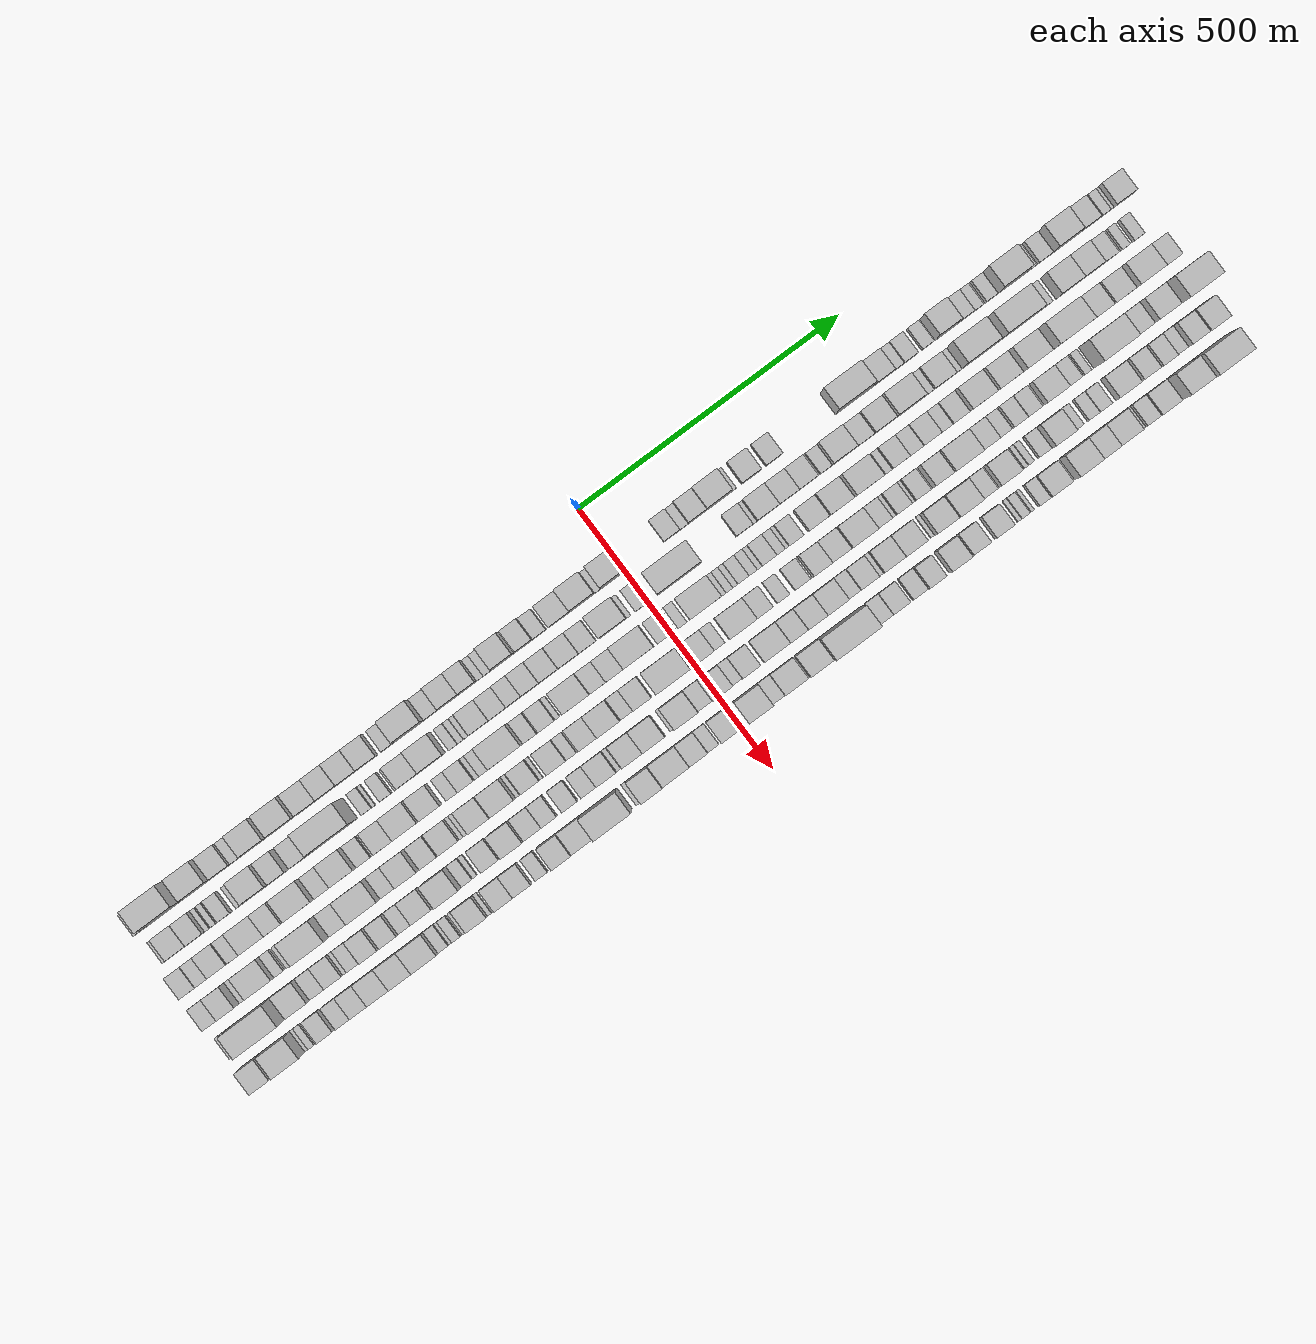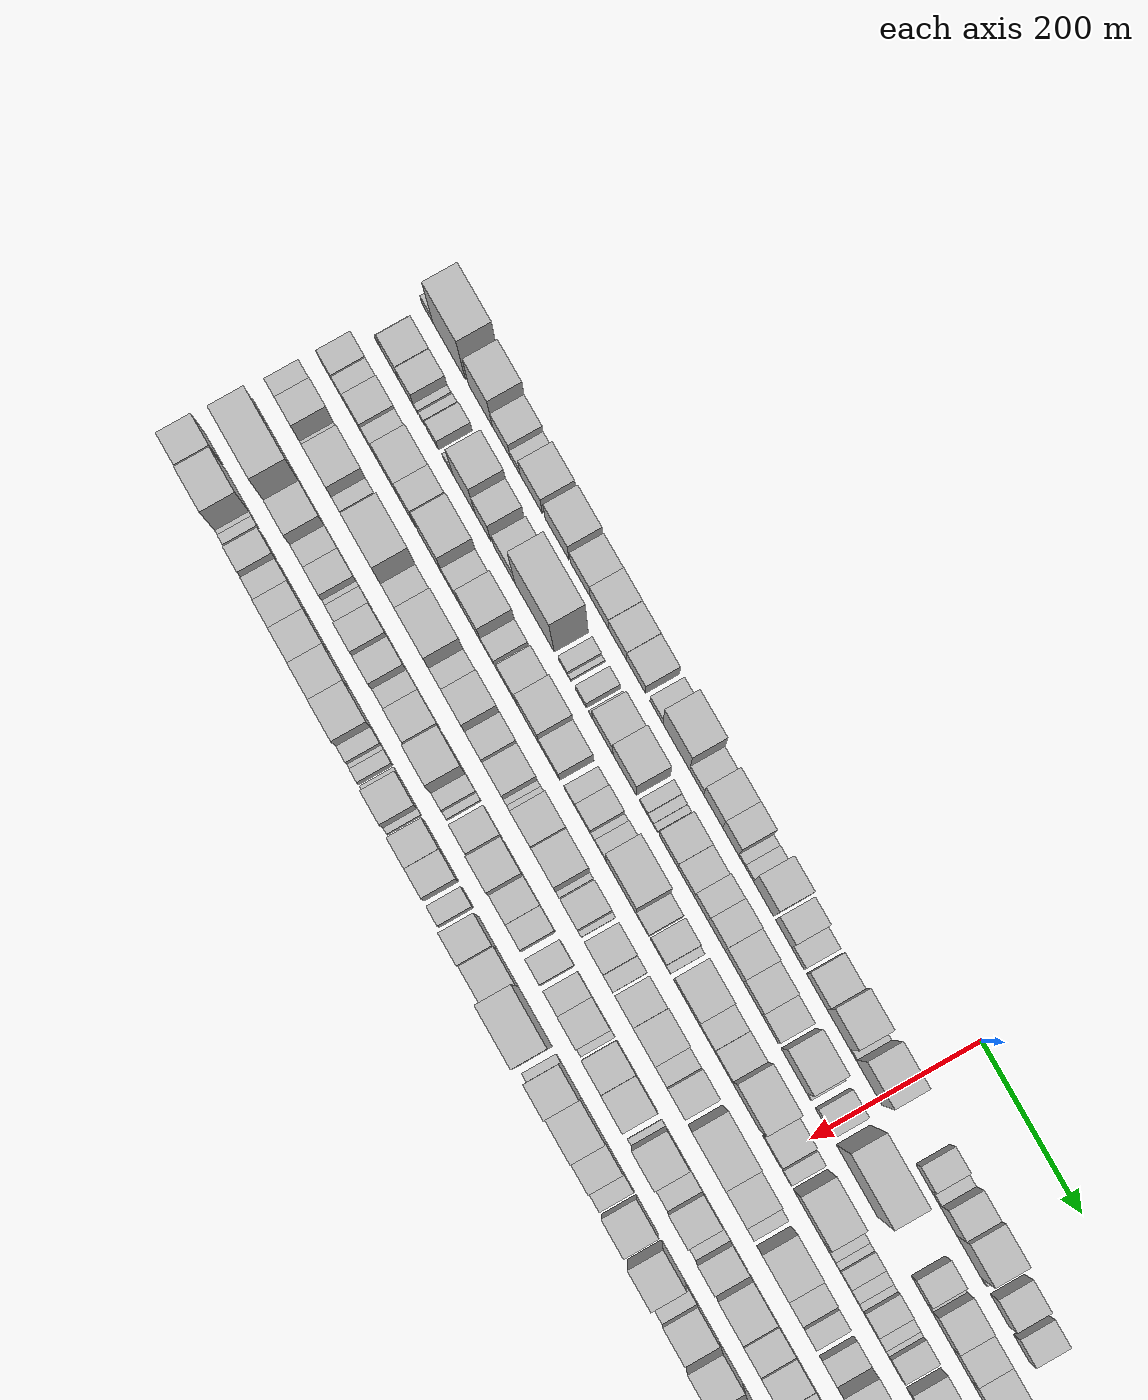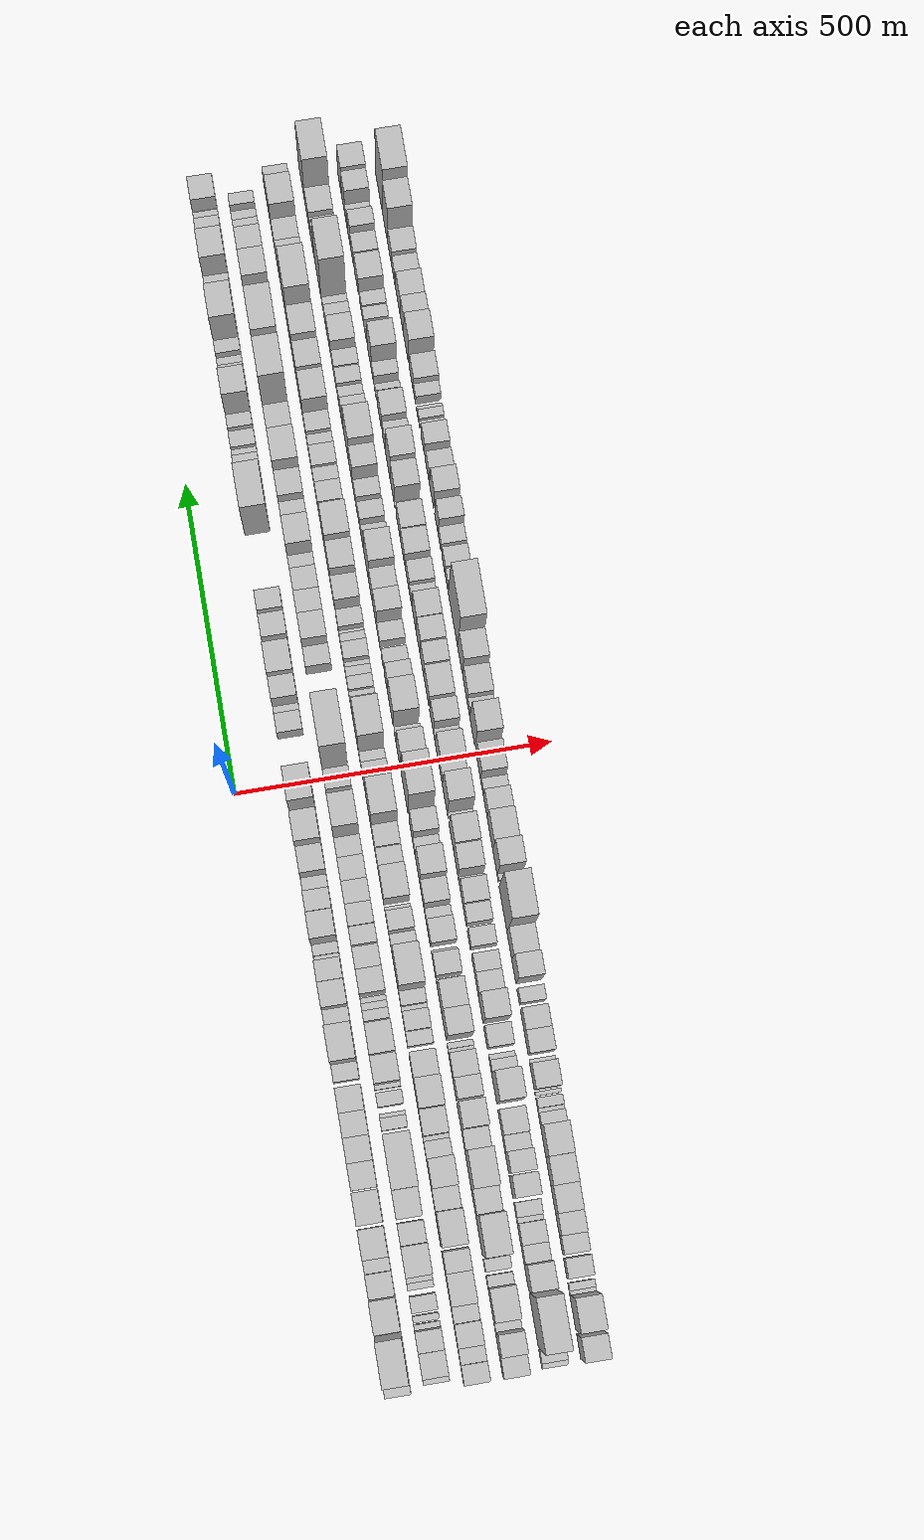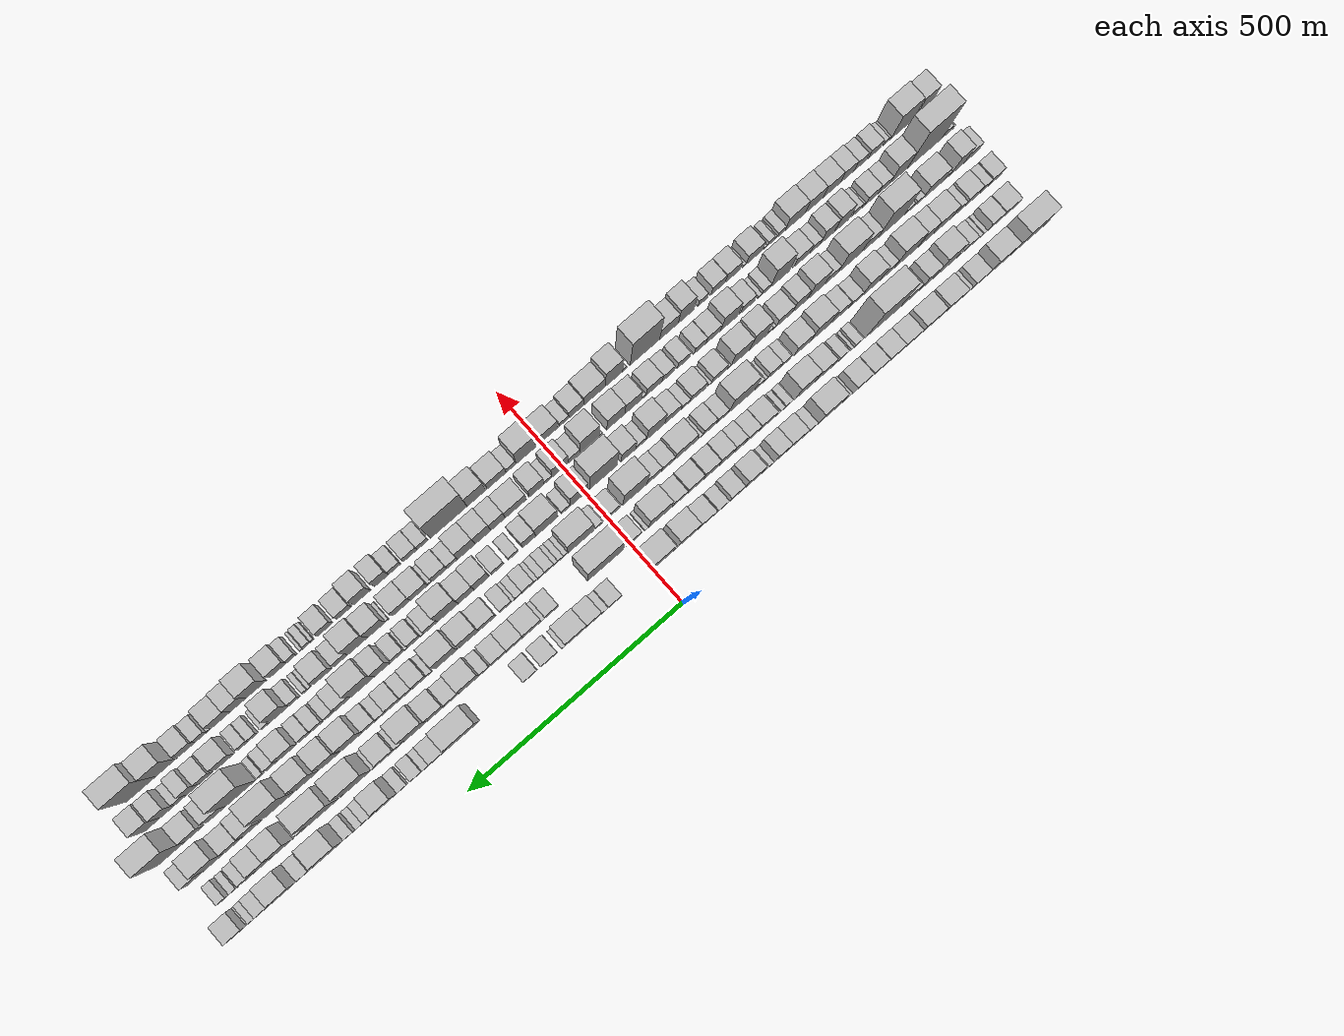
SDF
<sdf version="1.6">
 <world name="default">
  <scene>
   <sky><clouds><speed>12</speed></clouds></sky>
   <ambient>0.4 0.4 0.4 1</ambient>
   <background>0.7 0.7 0.7 1</background>
   <shadows>1</shadows>
  </scene>
  <gravity>0 0 -9.8066</gravity>
  <magnetic_field>6e-06 2.3e-05 -4.2e-05</magnetic_field>
  <physics default="0" name="default_physics" type="ode">
   <ode>
    <solver>
     <type>quick</type>
     <iters>10</iters>
     <sor>1.0</sor>
     <use_dynamic_moi_rescaling>0</use_dynamic_moi_rescaling>
    </solver>
    <constraints>
     <cfm>0</cfm>
     <erp>0.2</erp>
     <contact_max_correcting_vel>100</contact_max_correcting_vel>
     <contact_surface_layer>0.001</contact_surface_layer>
    </constraints>
   </ode>
   <max_step_size>0.004</max_step_size>
   <real_time_factor>1</real_time_factor>
   <real_time_update_rate>250</real_time_update_rate>
  </physics>
  <light name="sun" type="directional">
   <pose>0 0 10 0 0 0</pose>
   <diffuse>0.8 0.8 0.8 1</diffuse>
   <specular>0.2 0.2 0.2 1</specular>
   <attenuation>
    <range>1000</range>
    <constant>0.9</constant>
    <linear>0.01</linear>
    <quadratic>0.001</quadratic>
   </attenuation>
   <direction>-0.5 0.1 -0.9</direction>
  </light>
  <model name="building_1">
   <static>1</static>
   <pose>100.0000 -928.5805 0 0.000000 0.000000 0.000000</pose>
   <link name="link">
    <pose>0 0 19.50 0 0 0</pose>
    <collision name="collision"><geometry><box><size>40.0000 22.8391 39.0000</size></box></geometry></collision>
    <visual name="visual">
     <cast_shadows>0</cast_shadows>
     <geometry><box><size>40.0000 22.8391 39.0000</size></box></geometry>
     <material>
      <script>
       <uri>model://HANNAS_wall/materials/scripts</uri>
       <uri>model://HANNAS_wall/materials/textures</uri>
       <name>vrc/HANNAS_wall</name>
      </script>
     </material>
    </visual>
   </link>
  </model>
  <model name="building_2">
   <static>1</static>
   <pose>100.0000 -883.2201 0 0.000000 0.000000 0.000000</pose>
   <link name="link">
    <pose>0 0 91.50 0 0 0</pose>
    <collision name="collision"><geometry><box><size>40.0000 67.8817 183.0000</size></box></geometry></collision>
    <visual name="visual">
     <cast_shadows>0</cast_shadows>
     <geometry><box><size>40.0000 67.8817 183.0000</size></box></geometry>
     <material>
      <script>
       <uri>model://HANNAS_wall/materials/scripts</uri>
       <uri>model://HANNAS_wall/materials/textures</uri>
       <name>vrc/HANNAS_wall</name>
      </script>
     </material>
    </visual>
   </link>
  </model>
  <model name="building_3">
   <static>1</static>
   <pose>100.0000 -817.6146 0 0.000000 0.000000 0.000000</pose>
   <link name="link">
    <pose>0 0 66.00 0 0 0</pose>
    <collision name="collision"><geometry><box><size>40.0000 49.3291 132.0000</size></box></geometry></collision>
    <visual name="visual">
     <cast_shadows>0</cast_shadows>
     <geometry><box><size>40.0000 49.3291 132.0000</size></box></geometry>
     <material>
      <script>
       <uri>model://HANNAS_wall/materials/scripts</uri>
       <uri>model://HANNAS_wall/materials/textures</uri>
       <name>vrc/HANNAS_wall</name>
      </script>
     </material>
    </visual>
   </link>
  </model>
  <model name="building_4">
   <static>1</static>
   <pose>100.0000 -774.3493 0 0.000000 0.000000 0.000000</pose>
   <link name="link">
    <pose>0 0 34.50 0 0 0</pose>
    <collision name="collision"><geometry><box><size>40.0000 37.2015 69.0000</size></box></geometry></collision>
    <visual name="visual">
     <cast_shadows>0</cast_shadows>
     <geometry><box><size>40.0000 37.2015 69.0000</size></box></geometry>
     <material>
      <script>
       <uri>model://HANNAS_wall/materials/scripts</uri>
       <uri>model://HANNAS_wall/materials/textures</uri>
       <name>vrc/HANNAS_wall</name>
      </script>
     </material>
    </visual>
   </link>
  </model>
  <model name="building_5">
   <static>1</static>
   <pose>100.0000 -745.1743 0 0.000000 0.000000 0.000000</pose>
   <link name="link">
    <pose>0 0 19.50 0 0 0</pose>
    <collision name="collision"><geometry><box><size>40.0000 21.1486 39.0000</size></box></geometry></collision>
    <visual name="visual">
     <cast_shadows>0</cast_shadows>
     <geometry><box><size>40.0000 21.1486 39.0000</size></box></geometry>
     <material>
      <script>
       <uri>model://HANNAS_wall/materials/scripts</uri>
       <uri>model://HANNAS_wall/materials/textures</uri>
       <name>vrc/HANNAS_wall</name>
      </script>
     </material>
    </visual>
   </link>
  </model>
  <model name="building_6">
   <static>1</static>
   <pose>100.0000 -711.8089 0 0.000000 0.000000 0.000000</pose>
   <link name="link">
    <pose>0 0 42.00 0 0 0</pose>
    <collision name="collision"><geometry><box><size>40.0000 45.5821 84.0000</size></box></geometry></collision>
    <visual name="visual">
     <cast_shadows>0</cast_shadows>
     <geometry><box><size>40.0000 45.5821 84.0000</size></box></geometry>
     <material>
      <script>
       <uri>model://HANNAS_wall/materials/scripts</uri>
       <uri>model://HANNAS_wall/materials/textures</uri>
       <name>vrc/HANNAS_wall</name>
      </script>
     </material>
    </visual>
   </link>
  </model>
  <model name="building_7">
   <static>1</static>
   <pose>100.0000 -658.3033 0 0.000000 0.000000 0.000000</pose>
   <link name="link">
    <pose>0 0 45.00 0 0 0</pose>
    <collision name="collision"><geometry><box><size>40.0000 49.4292 90.0000</size></box></geometry></collision>
    <visual name="visual">
     <cast_shadows>0</cast_shadows>
     <geometry><box><size>40.0000 49.4292 90.0000</size></box></geometry>
     <material>
      <script>
       <uri>model://HANNAS_wall/materials/scripts</uri>
       <uri>model://HANNAS_wall/materials/textures</uri>
       <name>vrc/HANNAS_wall</name>
      </script>
     </material>
    </visual>
   </link>
  </model>
  <model name="building_8">
   <static>1</static>
   <pose>100.0000 -610.2642 0 0.000000 0.000000 0.000000</pose>
   <link name="link">
    <pose>0 0 34.50 0 0 0</pose>
    <collision name="collision"><geometry><box><size>40.0000 40.6489 69.0000</size></box></geometry></collision>
    <visual name="visual">
     <cast_shadows>0</cast_shadows>
     <geometry><box><size>40.0000 40.6489 69.0000</size></box></geometry>
     <material>
      <script>
       <uri>model://HANNAS_wall/materials/scripts</uri>
       <uri>model://HANNAS_wall/materials/textures</uri>
       <name>vrc/HANNAS_wall</name>
      </script>
     </material>
    </visual>
   </link>
  </model>
  <model name="building_9">
   <static>1</static>
   <pose>100.0000 -570.7548 0 0.000000 0.000000 0.000000</pose>
   <link name="link">
    <pose>0 0 36.00 0 0 0</pose>
    <collision name="collision"><geometry><box><size>40.0000 38.3700 72.0000</size></box></geometry></collision>
    <visual name="visual">
     <cast_shadows>0</cast_shadows>
     <geometry><box><size>40.0000 38.3700 72.0000</size></box></geometry>
     <material>
      <script>
       <uri>model://HANNAS_wall/materials/scripts</uri>
       <uri>model://HANNAS_wall/materials/textures</uri>
       <name>vrc/HANNAS_wall</name>
      </script>
     </material>
    </visual>
   </link>
  </model>
  <model name="building_10">
   <static>1</static>
   <pose>100.0000 -532.8033 0 0.000000 0.000000 0.000000</pose>
   <link name="link">
    <pose>0 0 34.50 0 0 0</pose>
    <collision name="collision"><geometry><box><size>40.0000 37.5329 69.0000</size></box></geometry></collision>
    <visual name="visual">
     <cast_shadows>0</cast_shadows>
     <geometry><box><size>40.0000 37.5329 69.0000</size></box></geometry>
     <material>
      <script>
       <uri>model://HANNAS_wall/materials/scripts</uri>
       <uri>model://HANNAS_wall/materials/textures</uri>
       <name>vrc/HANNAS_wall</name>
      </script>
     </material>
    </visual>
   </link>
  </model>
  <model name="building_11">
   <static>1</static>
   <pose>100.0000 -494.6859 0 0.000000 0.000000 0.000000</pose>
   <link name="link">
    <pose>0 0 33.00 0 0 0</pose>
    <collision name="collision"><geometry><box><size>40.0000 38.7019 66.0000</size></box></geometry></collision>
    <visual name="visual">
     <cast_shadows>0</cast_shadows>
     <geometry><box><size>40.0000 38.7019 66.0000</size></box></geometry>
     <material>
      <script>
       <uri>model://HANNAS_wall/materials/scripts</uri>
       <uri>model://HANNAS_wall/materials/textures</uri>
       <name>vrc/HANNAS_wall</name>
      </script>
     </material>
    </visual>
   </link>
  </model>
  <model name="building_12">
   <static>1</static>
   <pose>100.0000 -452.9017 0 0.000000 0.000000 0.000000</pose>
   <link name="link">
    <pose>0 0 22.50 0 0 0</pose>
    <collision name="collision"><geometry><box><size>40.0000 26.8665 45.0000</size></box></geometry></collision>
    <visual name="visual">
     <cast_shadows>0</cast_shadows>
     <geometry><box><size>40.0000 26.8665 45.0000</size></box></geometry>
     <material>
      <script>
       <uri>model://HANNAS_wall/materials/scripts</uri>
       <uri>model://HANNAS_wall/materials/textures</uri>
       <name>vrc/HANNAS_wall</name>
      </script>
     </material>
    </visual>
   </link>
  </model>
  <model name="building_13">
   <static>1</static>
   <pose>100.0000 -412.1161 0 0.000000 0.000000 0.000000</pose>
   <link name="link">
    <pose>0 0 75.00 0 0 0</pose>
    <collision name="collision"><geometry><box><size>40.0000 54.7048 150.0000</size></box></geometry></collision>
    <visual name="visual">
     <cast_shadows>0</cast_shadows>
     <geometry><box><size>40.0000 54.7048 150.0000</size></box></geometry>
     <material>
      <script>
       <uri>model://HANNAS_wall/materials/scripts</uri>
       <uri>model://HANNAS_wall/materials/textures</uri>
       <name>vrc/HANNAS_wall</name>
      </script>
     </material>
    </visual>
   </link>
  </model>
  <model name="building_14">
   <static>1</static>
   <pose>100.0000 -370.3261 0 0.000000 0.000000 0.000000</pose>
   <link name="link">
    <pose>0 0 25.50 0 0 0</pose>
    <collision name="collision"><geometry><box><size>40.0000 28.8751 51.0000</size></box></geometry></collision>
    <visual name="visual">
     <cast_shadows>0</cast_shadows>
     <geometry><box><size>40.0000 28.8751 51.0000</size></box></geometry>
     <material>
      <script>
       <uri>model://HANNAS_wall/materials/scripts</uri>
       <uri>model://HANNAS_wall/materials/textures</uri>
       <name>vrc/HANNAS_wall</name>
      </script>
     </material>
    </visual>
   </link>
  </model>
  <model name="building_15">
   <static>1</static>
   <pose>100.0000 -336.4003 0 0.000000 0.000000 0.000000</pose>
   <link name="link">
    <pose>0 0 52.50 0 0 0</pose>
    <collision name="collision"><geometry><box><size>40.0000 38.9765 105.0000</size></box></geometry></collision>
    <visual name="visual">
     <cast_shadows>0</cast_shadows>
     <geometry><box><size>40.0000 38.9765 105.0000</size></box></geometry>
     <material>
      <script>
       <uri>model://HANNAS_wall/materials/scripts</uri>
       <uri>model://HANNAS_wall/materials/textures</uri>
       <name>vrc/HANNAS_wall</name>
      </script>
     </material>
    </visual>
   </link>
  </model>
  <model name="building_16">
   <static>1</static>
   <pose>100.0000 -300.6600 0 0.000000 0.000000 0.000000</pose>
   <link name="link">
    <pose>0 0 54.00 0 0 0</pose>
    <collision name="collision"><geometry><box><size>40.0000 32.5042 108.0000</size></box></geometry></collision>
    <visual name="visual">
     <cast_shadows>0</cast_shadows>
     <geometry><box><size>40.0000 32.5042 108.0000</size></box></geometry>
     <material>
      <script>
       <uri>model://HANNAS_wall/materials/scripts</uri>
       <uri>model://HANNAS_wall/materials/textures</uri>
       <name>vrc/HANNAS_wall</name>
      </script>
     </material>
    </visual>
   </link>
  </model>
  <model name="building_17">
   <static>1</static>
   <pose>100.0000 -278.0071 0 0.000000 0.000000 0.000000</pose>
   <link name="link">
    <pose>0 0 13.50 0 0 0</pose>
    <collision name="collision"><geometry><box><size>40.0000 12.8015 27.0000</size></box></geometry></collision>
    <visual name="visual">
     <cast_shadows>0</cast_shadows>
     <geometry><box><size>40.0000 12.8015 27.0000</size></box></geometry>
     <material>
      <script>
       <uri>model://HANNAS_wall/materials/scripts</uri>
       <uri>model://HANNAS_wall/materials/textures</uri>
       <name>vrc/HANNAS_wall</name>
      </script>
     </material>
    </visual>
   </link>
  </model>
  <model name="building_18">
   <static>1</static>
   <pose>100.0000 -262.7538 0 0.000000 0.000000 0.000000</pose>
   <link name="link">
    <pose>0 0 16.50 0 0 0</pose>
    <collision name="collision"><geometry><box><size>40.0000 17.7049 33.0000</size></box></geometry></collision>
    <visual name="visual">
     <cast_shadows>0</cast_shadows>
     <geometry><box><size>40.0000 17.7049 33.0000</size></box></geometry>
     <material>
      <script>
       <uri>model://HANNAS_wall/materials/scripts</uri>
       <uri>model://HANNAS_wall/materials/textures</uri>
       <name>vrc/HANNAS_wall</name>
      </script>
     </material>
    </visual>
   </link>
  </model>
  <model name="building_19">
   <static>1</static>
   <pose>100.0000 -233.5406 0 0.000000 0.000000 0.000000</pose>
   <link name="link">
    <pose>0 0 67.50 0 0 0</pose>
    <collision name="collision"><geometry><box><size>40.0000 40.7216 135.0000</size></box></geometry></collision>
    <visual name="visual">
     <cast_shadows>0</cast_shadows>
     <geometry><box><size>40.0000 40.7216 135.0000</size></box></geometry>
     <material>
      <script>
       <uri>model://HANNAS_wall/materials/scripts</uri>
       <uri>model://HANNAS_wall/materials/textures</uri>
       <name>vrc/HANNAS_wall</name>
      </script>
     </material>
    </visual>
   </link>
  </model>
  <model name="building_20">
   <static>1</static>
   <pose>100.0000 -193.0922 0 0.000000 0.000000 0.000000</pose>
   <link name="link">
    <pose>0 0 49.50 0 0 0</pose>
    <collision name="collision"><geometry><box><size>40.0000 32.1751 99.0000</size></box></geometry></collision>
    <visual name="visual">
     <cast_shadows>0</cast_shadows>
     <geometry><box><size>40.0000 32.1751 99.0000</size></box></geometry>
     <material>
      <script>
       <uri>model://HANNAS_wall/materials/scripts</uri>
       <uri>model://HANNAS_wall/materials/textures</uri>
       <name>vrc/HANNAS_wall</name>
      </script>
     </material>
    </visual>
   </link>
  </model>
  <model name="building_21">
   <static>1</static>
   <pose>100.0000 -164.2542 0 0.000000 0.000000 0.000000</pose>
   <link name="link">
    <pose>0 0 24.00 0 0 0</pose>
    <collision name="collision"><geometry><box><size>40.0000 25.5011 48.0000</size></box></geometry></collision>
    <visual name="visual">
     <cast_shadows>0</cast_shadows>
     <geometry><box><size>40.0000 25.5011 48.0000</size></box></geometry>
     <material>
      <script>
       <uri>model://HANNAS_wall/materials/scripts</uri>
       <uri>model://HANNAS_wall/materials/textures</uri>
       <name>vrc/HANNAS_wall</name>
      </script>
     </material>
    </visual>
   </link>
  </model>
  <model name="building_22">
   <static>1</static>
   <pose>100.0000 -125.8991 0 0.000000 0.000000 0.000000</pose>
   <link name="link">
    <pose>0 0 36.00 0 0 0</pose>
    <collision name="collision"><geometry><box><size>40.0000 41.2092 72.0000</size></box></geometry></collision>
    <visual name="visual">
     <cast_shadows>0</cast_shadows>
     <geometry><box><size>40.0000 41.2092 72.0000</size></box></geometry>
     <material>
      <script>
       <uri>model://HANNAS_wall/materials/scripts</uri>
       <uri>model://HANNAS_wall/materials/textures</uri>
       <name>vrc/HANNAS_wall</name>
      </script>
     </material>
    </visual>
   </link>
  </model>
  <model name="building_23">
   <static>1</static>
   <pose>100.0000 -81.8025 0 0.000000 0.000000 0.000000</pose>
   <link name="link">
    <pose>0 0 67.50 0 0 0</pose>
    <collision name="collision"><geometry><box><size>40.0000 46.9839 135.0000</size></box></geometry></collision>
    <visual name="visual">
     <cast_shadows>0</cast_shadows>
     <geometry><box><size>40.0000 46.9839 135.0000</size></box></geometry>
     <material>
      <script>
       <uri>model://HANNAS_wall/materials/scripts</uri>
       <uri>model://HANNAS_wall/materials/textures</uri>
       <name>vrc/HANNAS_wall</name>
      </script>
     </material>
    </visual>
   </link>
  </model>
  <model name="building_24">
   <static>1</static>
   <pose>100.0000 -52.4212 0 0.000000 0.000000 0.000000</pose>
   <link name="link">
    <pose>0 0 12.00 0 0 0</pose>
    <collision name="collision"><geometry><box><size>40.0000 11.7787 24.0000</size></box></geometry></collision>
    <visual name="visual">
     <cast_shadows>0</cast_shadows>
     <geometry><box><size>40.0000 11.7787 24.0000</size></box></geometry>
     <material>
      <script>
       <uri>model://HANNAS_wall/materials/scripts</uri>
       <uri>model://HANNAS_wall/materials/textures</uri>
       <name>vrc/HANNAS_wall</name>
      </script>
     </material>
    </visual>
   </link>
  </model>
  <model name="building_25">
   <static>1</static>
   <pose>100.0000 -20.1399 0 0.000000 0.000000 0.000000</pose>
   <link name="link">
    <pose>0 0 79.50 0 0 0</pose>
    <collision name="collision"><geometry><box><size>40.0000 52.7841 159.0000</size></box></geometry></collision>
    <visual name="visual">
     <cast_shadows>0</cast_shadows>
     <geometry><box><size>40.0000 52.7841 159.0000</size></box></geometry>
     <material>
      <script>
       <uri>model://HANNAS_wall/materials/scripts</uri>
       <uri>model://HANNAS_wall/materials/textures</uri>
       <name>vrc/HANNAS_wall</name>
      </script>
     </material>
    </visual>
   </link>
  </model>
  <model name="building_26">
   <static>1</static>
   <pose>100.0000 89.4728 0 0.000000 0.000000 0.000000</pose>
   <link name="link">
    <pose>0 0 30.00 0 0 0</pose>
    <collision name="collision"><geometry><box><size>40.0000 30.8137 60.0000</size></box></geometry></collision>
    <visual name="visual">
     <cast_shadows>0</cast_shadows>
     <geometry><box><size>40.0000 30.8137 60.0000</size></box></geometry>
     <material>
      <script>
       <uri>model://HANNAS_wall/materials/scripts</uri>
       <uri>model://HANNAS_wall/materials/textures</uri>
       <name>vrc/HANNAS_wall</name>
      </script>
     </material>
    </visual>
   </link>
  </model>
  <model name="building_27">
   <static>1</static>
   <pose>100.0000 112.9700 0 0.000000 0.000000 0.000000</pose>
   <link name="link">
    <pose>0 0 15.00 0 0 0</pose>
    <collision name="collision"><geometry><box><size>40.0000 16.1807 30.0000</size></box></geometry></collision>
    <visual name="visual">
     <cast_shadows>0</cast_shadows>
     <geometry><box><size>40.0000 16.1807 30.0000</size></box></geometry>
     <material>
      <script>
       <uri>model://HANNAS_wall/materials/scripts</uri>
       <uri>model://HANNAS_wall/materials/textures</uri>
       <name>vrc/HANNAS_wall</name>
      </script>
     </material>
    </visual>
   </link>
  </model>
  <model name="building_28">
   <static>1</static>
   <pose>100.0000 138.5654 0 0.000000 0.000000 0.000000</pose>
   <link name="link">
    <pose>0 0 49.50 0 0 0</pose>
    <collision name="collision"><geometry><box><size>40.0000 35.0100 99.0000</size></box></geometry></collision>
    <visual name="visual">
     <cast_shadows>0</cast_shadows>
     <geometry><box><size>40.0000 35.0100 99.0000</size></box></geometry>
     <material>
      <script>
       <uri>model://HANNAS_wall/materials/scripts</uri>
       <uri>model://HANNAS_wall/materials/textures</uri>
       <name>vrc/HANNAS_wall</name>
      </script>
     </material>
    </visual>
   </link>
  </model>
  <model name="building_29">
   <static>1</static>
   <pose>100.0000 180.3426 0 0.000000 0.000000 0.000000</pose>
   <link name="link">
    <pose>0 0 64.50 0 0 0</pose>
    <collision name="collision"><geometry><box><size>40.0000 48.5444 129.0000</size></box></geometry></collision>
    <visual name="visual">
     <cast_shadows>0</cast_shadows>
     <geometry><box><size>40.0000 48.5444 129.0000</size></box></geometry>
     <material>
      <script>
       <uri>model://HANNAS_wall/materials/scripts</uri>
       <uri>model://HANNAS_wall/materials/textures</uri>
       <name>vrc/HANNAS_wall</name>
      </script>
     </material>
    </visual>
   </link>
  </model>
  <model name="building_30">
   <static>1</static>
   <pose>100.0000 208.9905 0 0.000000 0.000000 0.000000</pose>
   <link name="link">
    <pose>0 0 10.50 0 0 0</pose>
    <collision name="collision"><geometry><box><size>40.0000 8.7514 21.0000</size></box></geometry></collision>
    <visual name="visual">
     <cast_shadows>0</cast_shadows>
     <geometry><box><size>40.0000 8.7514 21.0000</size></box></geometry>
     <material>
      <script>
       <uri>model://HANNAS_wall/materials/scripts</uri>
       <uri>model://HANNAS_wall/materials/textures</uri>
       <name>vrc/HANNAS_wall</name>
      </script>
     </material>
    </visual>
   </link>
  </model>
  <model name="building_31">
   <static>1</static>
   <pose>100.0000 241.9794 0 0.000000 0.000000 0.000000</pose>
   <link name="link">
    <pose>0 0 36.00 0 0 0</pose>
    <collision name="collision"><geometry><box><size>40.0000 37.2263 72.0000</size></box></geometry></collision>
    <visual name="visual">
     <cast_shadows>0</cast_shadows>
     <geometry><box><size>40.0000 37.2263 72.0000</size></box></geometry>
     <material>
      <script>
       <uri>model://HANNAS_wall/materials/scripts</uri>
       <uri>model://HANNAS_wall/materials/textures</uri>
       <name>vrc/HANNAS_wall</name>
      </script>
     </material>
    </visual>
   </link>
  </model>
  <model name="building_32">
   <static>1</static>
   <pose>100.0000 285.6427 0 0.000000 0.000000 0.000000</pose>
   <link name="link">
    <pose>0 0 28.50 0 0 0</pose>
    <collision name="collision"><geometry><box><size>40.0000 32.1003 57.0000</size></box></geometry></collision>
    <visual name="visual">
     <cast_shadows>0</cast_shadows>
     <geometry><box><size>40.0000 32.1003 57.0000</size></box></geometry>
     <material>
      <script>
       <uri>model://HANNAS_wall/materials/scripts</uri>
       <uri>model://HANNAS_wall/materials/textures</uri>
       <name>vrc/HANNAS_wall</name>
      </script>
     </material>
    </visual>
   </link>
  </model>
  <model name="building_33">
   <static>1</static>
   <pose>100.0000 439.0972 0 0.000000 0.000000 0.000000</pose>
   <link name="link">
    <pose>0 0 90.00 0 0 0</pose>
    <collision name="collision"><geometry><box><size>40.0000 70.9362 180.0000</size></box></geometry></collision>
    <visual name="visual">
     <cast_shadows>0</cast_shadows>
     <geometry><box><size>40.0000 70.9362 180.0000</size></box></geometry>
     <material>
      <script>
       <uri>model://HANNAS_wall/materials/scripts</uri>
       <uri>model://HANNAS_wall/materials/textures</uri>
       <name>vrc/HANNAS_wall</name>
      </script>
     </material>
    </visual>
   </link>
  </model>
  <model name="building_34">
   <static>1</static>
   <pose>100.0000 495.0541 0 0.000000 0.000000 0.000000</pose>
   <link name="link">
    <pose>0 0 36.00 0 0 0</pose>
    <collision name="collision"><geometry><box><size>40.0000 40.9777 72.0000</size></box></geometry></collision>
    <visual name="visual">
     <cast_shadows>0</cast_shadows>
     <geometry><box><size>40.0000 40.9777 72.0000</size></box></geometry>
     <material>
      <script>
       <uri>model://HANNAS_wall/materials/scripts</uri>
       <uri>model://HANNAS_wall/materials/textures</uri>
       <name>vrc/HANNAS_wall</name>
      </script>
     </material>
    </visual>
   </link>
  </model>
  <model name="building_35">
   <static>1</static>
   <pose>100.0000 524.9111 0 0.000000 0.000000 0.000000</pose>
   <link name="link">
    <pose>0 0 18.00 0 0 0</pose>
    <collision name="collision"><geometry><box><size>40.0000 18.7362 36.0000</size></box></geometry></collision>
    <visual name="visual">
     <cast_shadows>0</cast_shadows>
     <geometry><box><size>40.0000 18.7362 36.0000</size></box></geometry>
     <material>
      <script>
       <uri>model://HANNAS_wall/materials/scripts</uri>
       <uri>model://HANNAS_wall/materials/textures</uri>
       <name>vrc/HANNAS_wall</name>
      </script>
     </material>
    </visual>
   </link>
  </model>
  <model name="building_36">
   <static>1</static>
   <pose>100.0000 547.2872 0 0.000000 0.000000 0.000000</pose>
   <link name="link">
    <pose>0 0 25.50 0 0 0</pose>
    <collision name="collision"><geometry><box><size>40.0000 26.0160 51.0000</size></box></geometry></collision>
    <visual name="visual">
     <cast_shadows>0</cast_shadows>
     <geometry><box><size>40.0000 26.0160 51.0000</size></box></geometry>
     <material>
      <script>
       <uri>model://HANNAS_wall/materials/scripts</uri>
       <uri>model://HANNAS_wall/materials/textures</uri>
       <name>vrc/HANNAS_wall</name>
      </script>
     </material>
    </visual>
   </link>
  </model>
  <model name="building_37">
   <static>1</static>
   <pose>100.0000 580.2507 0 0.000000 0.000000 0.000000</pose>
   <link name="link">
    <pose>0 0 19.50 0 0 0</pose>
    <collision name="collision"><geometry><box><size>40.0000 21.9110 39.0000</size></box></geometry></collision>
    <visual name="visual">
     <cast_shadows>0</cast_shadows>
     <geometry><box><size>40.0000 21.9110 39.0000</size></box></geometry>
     <material>
      <script>
       <uri>model://HANNAS_wall/materials/scripts</uri>
       <uri>model://HANNAS_wall/materials/textures</uri>
       <name>vrc/HANNAS_wall</name>
      </script>
     </material>
    </visual>
   </link>
  </model>
  <model name="building_38">
   <static>1</static>
   <pose>100.0000 616.6211 0 0.000000 0.000000 0.000000</pose>
   <link name="link">
    <pose>0 0 69.00 0 0 0</pose>
    <collision name="collision"><geometry><box><size>40.0000 42.8298 138.0000</size></box></geometry></collision>
    <visual name="visual">
     <cast_shadows>0</cast_shadows>
     <geometry><box><size>40.0000 42.8298 138.0000</size></box></geometry>
     <material>
      <script>
       <uri>model://HANNAS_wall/materials/scripts</uri>
       <uri>model://HANNAS_wall/materials/textures</uri>
       <name>vrc/HANNAS_wall</name>
      </script>
     </material>
    </visual>
   </link>
  </model>
  <model name="building_39">
   <static>1</static>
   <pose>100.0000 652.9359 0 0.000000 0.000000 0.000000</pose>
   <link name="link">
    <pose>0 0 27.00 0 0 0</pose>
    <collision name="collision"><geometry><box><size>40.0000 29.7998 54.0000</size></box></geometry></collision>
    <visual name="visual">
     <cast_shadows>0</cast_shadows>
     <geometry><box><size>40.0000 29.7998 54.0000</size></box></geometry>
     <material>
      <script>
       <uri>model://HANNAS_wall/materials/scripts</uri>
       <uri>model://HANNAS_wall/materials/textures</uri>
       <name>vrc/HANNAS_wall</name>
      </script>
     </material>
    </visual>
   </link>
  </model>
  <model name="building_40">
   <static>1</static>
   <pose>100.0000 677.0272 0 0.000000 0.000000 0.000000</pose>
   <link name="link">
    <pose>0 0 16.50 0 0 0</pose>
    <collision name="collision"><geometry><box><size>40.0000 18.3829 33.0000</size></box></geometry></collision>
    <visual name="visual">
     <cast_shadows>0</cast_shadows>
     <geometry><box><size>40.0000 18.3829 33.0000</size></box></geometry>
     <material>
      <script>
       <uri>model://HANNAS_wall/materials/scripts</uri>
       <uri>model://HANNAS_wall/materials/textures</uri>
       <name>vrc/HANNAS_wall</name>
      </script>
     </material>
    </visual>
   </link>
  </model>
  <model name="building_41">
   <static>1</static>
   <pose>100.0000 701.9941 0 0.000000 0.000000 0.000000</pose>
   <link name="link">
    <pose>0 0 21.00 0 0 0</pose>
    <collision name="collision"><geometry><box><size>40.0000 21.5510 42.0000</size></box></geometry></collision>
    <visual name="visual">
     <cast_shadows>0</cast_shadows>
     <geometry><box><size>40.0000 21.5510 42.0000</size></box></geometry>
     <material>
      <script>
       <uri>model://HANNAS_wall/materials/scripts</uri>
       <uri>model://HANNAS_wall/materials/textures</uri>
       <name>vrc/HANNAS_wall</name>
      </script>
     </material>
    </visual>
   </link>
  </model>
  <model name="building_42">
   <static>1</static>
   <pose>100.0000 743.3868 0 0.000000 0.000000 0.000000</pose>
   <link name="link">
    <pose>0 0 75.00 0 0 0</pose>
    <collision name="collision"><geometry><box><size>40.0000 55.2344 150.0000</size></box></geometry></collision>
    <visual name="visual">
     <cast_shadows>0</cast_shadows>
     <geometry><box><size>40.0000 55.2344 150.0000</size></box></geometry>
     <material>
      <script>
       <uri>model://HANNAS_wall/materials/scripts</uri>
       <uri>model://HANNAS_wall/materials/textures</uri>
       <name>vrc/HANNAS_wall</name>
      </script>
     </material>
    </visual>
   </link>
  </model>
  <model name="building_43">
   <static>1</static>
   <pose>100.0000 775.3153 0 0.000000 0.000000 0.000000</pose>
   <link name="link">
    <pose>0 0 10.50 0 0 0</pose>
    <collision name="collision"><geometry><box><size>40.0000 8.6226 21.0000</size></box></geometry></collision>
    <visual name="visual">
     <cast_shadows>0</cast_shadows>
     <geometry><box><size>40.0000 8.6226 21.0000</size></box></geometry>
     <material>
      <script>
       <uri>model://HANNAS_wall/materials/scripts</uri>
       <uri>model://HANNAS_wall/materials/textures</uri>
       <name>vrc/HANNAS_wall</name>
      </script>
     </material>
    </visual>
   </link>
  </model>
  <model name="building_44">
   <static>1</static>
   <pose>100.0000 784.2607 0 0.000000 0.000000 0.000000</pose>
   <link name="link">
    <pose>0 0 10.50 0 0 0</pose>
    <collision name="collision"><geometry><box><size>40.0000 9.2683 21.0000</size></box></geometry></collision>
    <visual name="visual">
     <cast_shadows>0</cast_shadows>
     <geometry><box><size>40.0000 9.2683 21.0000</size></box></geometry>
     <material>
      <script>
       <uri>model://HANNAS_wall/materials/scripts</uri>
       <uri>model://HANNAS_wall/materials/textures</uri>
       <name>vrc/HANNAS_wall</name>
      </script>
     </material>
    </visual>
   </link>
  </model>
  <model name="building_45">
   <static>1</static>
   <pose>100.0000 805.1872 0 0.000000 0.000000 0.000000</pose>
   <link name="link">
    <pose>0 0 22.50 0 0 0</pose>
    <collision name="collision"><geometry><box><size>40.0000 26.5847 45.0000</size></box></geometry></collision>
    <visual name="visual">
     <cast_shadows>0</cast_shadows>
     <geometry><box><size>40.0000 26.5847 45.0000</size></box></geometry>
     <material>
      <script>
       <uri>model://HANNAS_wall/materials/scripts</uri>
       <uri>model://HANNAS_wall/materials/textures</uri>
       <name>vrc/HANNAS_wall</name>
      </script>
     </material>
    </visual>
   </link>
  </model>
  <model name="building_46">
   <static>1</static>
   <pose>100.0000 846.1858 0 0.000000 0.000000 0.000000</pose>
   <link name="link">
    <pose>0 0 61.50 0 0 0</pose>
    <collision name="collision"><geometry><box><size>40.0000 47.4124 123.0000</size></box></geometry></collision>
    <visual name="visual">
     <cast_shadows>0</cast_shadows>
     <geometry><box><size>40.0000 47.4124 123.0000</size></box></geometry>
     <material>
      <script>
       <uri>model://HANNAS_wall/materials/scripts</uri>
       <uri>model://HANNAS_wall/materials/textures</uri>
       <name>vrc/HANNAS_wall</name>
      </script>
     </material>
    </visual>
   </link>
  </model>
  <model name="building_47">
   <static>1</static>
   <pose>100.0000 892.8496 0 0.000000 0.000000 0.000000</pose>
   <link name="link">
    <pose>0 0 31.50 0 0 0</pose>
    <collision name="collision"><geometry><box><size>40.0000 31.9152 63.0000</size></box></geometry></collision>
    <visual name="visual">
     <cast_shadows>0</cast_shadows>
     <geometry><box><size>40.0000 31.9152 63.0000</size></box></geometry>
     <material>
      <script>
       <uri>model://HANNAS_wall/materials/scripts</uri>
       <uri>model://HANNAS_wall/materials/textures</uri>
       <name>vrc/HANNAS_wall</name>
      </script>
     </material>
    </visual>
   </link>
  </model>
  <model name="building_48">
   <static>1</static>
   <pose>100.0000 922.6439 0 0.000000 0.000000 0.000000</pose>
   <link name="link">
    <pose>0 0 15.00 0 0 0</pose>
    <collision name="collision"><geometry><box><size>40.0000 15.6733 30.0000</size></box></geometry></collision>
    <visual name="visual">
     <cast_shadows>0</cast_shadows>
     <geometry><box><size>40.0000 15.6733 30.0000</size></box></geometry>
     <material>
      <script>
       <uri>model://HANNAS_wall/materials/scripts</uri>
       <uri>model://HANNAS_wall/materials/textures</uri>
       <name>vrc/HANNAS_wall</name>
      </script>
     </material>
    </visual>
   </link>
  </model>
  <model name="building_49">
   <static>1</static>
   <pose>100.0000 933.8563 0 0.000000 0.000000 0.000000</pose>
   <link name="link">
    <pose>0 0 7.50 0 0 0</pose>
    <collision name="collision"><geometry><box><size>40.0000 6.7515 15.0000</size></box></geometry></collision>
    <visual name="visual">
     <cast_shadows>0</cast_shadows>
     <geometry><box><size>40.0000 6.7515 15.0000</size></box></geometry>
     <material>
      <script>
       <uri>model://HANNAS_wall/materials/scripts</uri>
       <uri>model://HANNAS_wall/materials/textures</uri>
       <name>vrc/HANNAS_wall</name>
      </script>
     </material>
    </visual>
   </link>
  </model>
  <model name="building_50">
   <static>1</static>
   <pose>100.0000 956.7303 0 0.000000 0.000000 0.000000</pose>
   <link name="link">
    <pose>0 0 34.50 0 0 0</pose>
    <collision name="collision"><geometry><box><size>40.0000 38.9966 69.0000</size></box></geometry></collision>
    <visual name="visual">
     <cast_shadows>0</cast_shadows>
     <geometry><box><size>40.0000 38.9966 69.0000</size></box></geometry>
     <material>
      <script>
       <uri>model://HANNAS_wall/materials/scripts</uri>
       <uri>model://HANNAS_wall/materials/textures</uri>
       <name>vrc/HANNAS_wall</name>
      </script>
     </material>
    </visual>
   </link>
  </model>
  <model name="building_51">
   <static>1</static>
   <pose>160.0000 -925.8647 0 0.000000 0.000000 0.000000</pose>
   <link name="link">
    <pose>0 0 12.00 0 0 0</pose>
    <collision name="collision"><geometry><box><size>40.0000 10.2706 24.0000</size></box></geometry></collision>
    <visual name="visual">
     <cast_shadows>0</cast_shadows>
     <geometry><box><size>40.0000 10.2706 24.0000</size></box></geometry>
     <material>
      <script>
       <uri>model://HANNAS_wall/materials/scripts</uri>
       <uri>model://HANNAS_wall/materials/textures</uri>
       <name>vrc/HANNAS_wall</name>
      </script>
     </material>
    </visual>
   </link>
  </model>
  <model name="building_52">
   <static>1</static>
   <pose>160.0000 -901.6727 0 0.000000 0.000000 0.000000</pose>
   <link name="link">
    <pose>0 0 33.00 0 0 0</pose>
    <collision name="collision"><geometry><box><size>40.0000 38.1135 66.0000</size></box></geometry></collision>
    <visual name="visual">
     <cast_shadows>0</cast_shadows>
     <geometry><box><size>40.0000 38.1135 66.0000</size></box></geometry>
     <material>
      <script>
       <uri>model://HANNAS_wall/materials/scripts</uri>
       <uri>model://HANNAS_wall/materials/textures</uri>
       <name>vrc/HANNAS_wall</name>
      </script>
     </material>
    </visual>
   </link>
  </model>
  <model name="building_53">
   <static>1</static>
   <pose>160.0000 -866.5047 0 0.000000 0.000000 0.000000</pose>
   <link name="link">
    <pose>0 0 31.50 0 0 0</pose>
    <collision name="collision"><geometry><box><size>40.0000 32.2225 63.0000</size></box></geometry></collision>
    <visual name="visual">
     <cast_shadows>0</cast_shadows>
     <geometry><box><size>40.0000 32.2225 63.0000</size></box></geometry>
     <material>
      <script>
       <uri>model://HANNAS_wall/materials/scripts</uri>
       <uri>model://HANNAS_wall/materials/textures</uri>
       <name>vrc/HANNAS_wall</name>
      </script>
     </material>
    </visual>
   </link>
  </model>
  <model name="building_54">
   <static>1</static>
   <pose>160.0000 -846.1203 0 0.000000 0.000000 0.000000</pose>
   <link name="link">
    <pose>0 0 9.00 0 0 0</pose>
    <collision name="collision"><geometry><box><size>40.0000 8.5462 18.0000</size></box></geometry></collision>
    <visual name="visual">
     <cast_shadows>0</cast_shadows>
     <geometry><box><size>40.0000 8.5462 18.0000</size></box></geometry>
     <material>
      <script>
       <uri>model://HANNAS_wall/materials/scripts</uri>
       <uri>model://HANNAS_wall/materials/textures</uri>
       <name>vrc/HANNAS_wall</name>
      </script>
     </material>
    </visual>
   </link>
  </model>
  <model name="building_55">
   <static>1</static>
   <pose>160.0000 -833.8532 0 0.000000 0.000000 0.000000</pose>
   <link name="link">
    <pose>0 0 12.00 0 0 0</pose>
    <collision name="collision"><geometry><box><size>40.0000 9.9879 24.0000</size></box></geometry></collision>
    <visual name="visual">
     <cast_shadows>0</cast_shadows>
     <geometry><box><size>40.0000 9.9879 24.0000</size></box></geometry>
     <material>
      <script>
       <uri>model://HANNAS_wall/materials/scripts</uri>
       <uri>model://HANNAS_wall/materials/textures</uri>
       <name>vrc/HANNAS_wall</name>
      </script>
     </material>
    </visual>
   </link>
  </model>
  <model name="building_56">
   <static>1</static>
   <pose>160.0000 -811.6302 0 0.000000 0.000000 0.000000</pose>
   <link name="link">
    <pose>0 0 22.50 0 0 0</pose>
    <collision name="collision"><geometry><box><size>40.0000 24.4582 45.0000</size></box></geometry></collision>
    <visual name="visual">
     <cast_shadows>0</cast_shadows>
     <geometry><box><size>40.0000 24.4582 45.0000</size></box></geometry>
     <material>
      <script>
       <uri>model://HANNAS_wall/materials/scripts</uri>
       <uri>model://HANNAS_wall/materials/textures</uri>
       <name>vrc/HANNAS_wall</name>
      </script>
     </material>
    </visual>
   </link>
  </model>
  <model name="building_57">
   <static>1</static>
   <pose>160.0000 -785.2358 0 0.000000 0.000000 0.000000</pose>
   <link name="link">
    <pose>0 0 10.50 0 0 0</pose>
    <collision name="collision"><geometry><box><size>40.0000 10.3304 21.0000</size></box></geometry></collision>
    <visual name="visual">
     <cast_shadows>0</cast_shadows>
     <geometry><box><size>40.0000 10.3304 21.0000</size></box></geometry>
     <material>
      <script>
       <uri>model://HANNAS_wall/materials/scripts</uri>
       <uri>model://HANNAS_wall/materials/textures</uri>
       <name>vrc/HANNAS_wall</name>
      </script>
     </material>
    </visual>
   </link>
  </model>
  <model name="building_58">
   <static>1</static>
   <pose>160.0000 -774.2130 0 0.000000 0.000000 0.000000</pose>
   <link name="link">
    <pose>0 0 12.00 0 0 0</pose>
    <collision name="collision"><geometry><box><size>40.0000 11.7152 24.0000</size></box></geometry></collision>
    <visual name="visual">
     <cast_shadows>0</cast_shadows>
     <geometry><box><size>40.0000 11.7152 24.0000</size></box></geometry>
     <material>
      <script>
       <uri>model://HANNAS_wall/materials/scripts</uri>
       <uri>model://HANNAS_wall/materials/textures</uri>
       <name>vrc/HANNAS_wall</name>
      </script>
     </material>
    </visual>
   </link>
  </model>
  <model name="building_59">
   <static>1</static>
   <pose>160.0000 -745.3790 0 0.000000 0.000000 0.000000</pose>
   <link name="link">
    <pose>0 0 75.00 0 0 0</pose>
    <collision name="collision"><geometry><box><size>40.0000 45.9529 150.0000</size></box></geometry></collision>
    <visual name="visual">
     <cast_shadows>0</cast_shadows>
     <geometry><box><size>40.0000 45.9529 150.0000</size></box></geometry>
     <material>
      <script>
       <uri>model://HANNAS_wall/materials/scripts</uri>
       <uri>model://HANNAS_wall/materials/textures</uri>
       <name>vrc/HANNAS_wall</name>
      </script>
     </material>
    </visual>
   </link>
  </model>
  <model name="building_60">
   <static>1</static>
   <pose>160.0000 -705.8684 0 0.000000 0.000000 0.000000</pose>
   <link name="link">
    <pose>0 0 51.00 0 0 0</pose>
    <collision name="collision"><geometry><box><size>40.0000 33.0682 102.0000</size></box></geometry></collision>
    <visual name="visual">
     <cast_shadows>0</cast_shadows>
     <geometry><box><size>40.0000 33.0682 102.0000</size></box></geometry>
     <material>
      <script>
       <uri>model://HANNAS_wall/materials/scripts</uri>
       <uri>model://HANNAS_wall/materials/textures</uri>
       <name>vrc/HANNAS_wall</name>
      </script>
     </material>
    </visual>
   </link>
  </model>
  <model name="building_61">
   <static>1</static>
   <pose>160.0000 -661.4337 0 0.000000 0.000000 0.000000</pose>
   <link name="link">
    <pose>0 0 37.50 0 0 0</pose>
    <collision name="collision"><geometry><box><size>40.0000 43.8013 75.0000</size></box></geometry></collision>
    <visual name="visual">
     <cast_shadows>0</cast_shadows>
     <geometry><box><size>40.0000 43.8013 75.0000</size></box></geometry>
     <material>
      <script>
       <uri>model://HANNAS_wall/materials/scripts</uri>
       <uri>model://HANNAS_wall/materials/textures</uri>
       <name>vrc/HANNAS_wall</name>
      </script>
     </material>
    </visual>
   </link>
  </model>
  <model name="building_62">
   <static>1</static>
   <pose>160.0000 -598.9825 0 0.000000 0.000000 0.000000</pose>
   <link name="link">
    <pose>0 0 111.00 0 0 0</pose>
    <collision name="collision"><geometry><box><size>40.0000 81.1011 222.0000</size></box></geometry></collision>
    <visual name="visual">
     <cast_shadows>0</cast_shadows>
     <geometry><box><size>40.0000 81.1011 222.0000</size></box></geometry>
     <material>
      <script>
       <uri>model://HANNAS_wall/materials/scripts</uri>
       <uri>model://HANNAS_wall/materials/textures</uri>
       <name>vrc/HANNAS_wall</name>
      </script>
     </material>
    </visual>
   </link>
  </model>
  <model name="building_63">
   <static>1</static>
   <pose>160.0000 -539.8541 0 0.000000 0.000000 0.000000</pose>
   <link name="link">
    <pose>0 0 16.50 0 0 0</pose>
    <collision name="collision"><geometry><box><size>40.0000 19.1556 33.0000</size></box></geometry></collision>
    <visual name="visual">
     <cast_shadows>0</cast_shadows>
     <geometry><box><size>40.0000 19.1556 33.0000</size></box></geometry>
     <material>
      <script>
       <uri>model://HANNAS_wall/materials/scripts</uri>
       <uri>model://HANNAS_wall/materials/textures</uri>
       <name>vrc/HANNAS_wall</name>
      </script>
     </material>
    </visual>
   </link>
  </model>
  <model name="building_64">
   <static>1</static>
   <pose>160.0000 -527.0520 0 0.000000 0.000000 0.000000</pose>
   <link name="link">
    <pose>0 0 7.50 0 0 0</pose>
    <collision name="collision"><geometry><box><size>40.0000 6.4485 15.0000</size></box></geometry></collision>
    <visual name="visual">
     <cast_shadows>0</cast_shadows>
     <geometry><box><size>40.0000 6.4485 15.0000</size></box></geometry>
     <material>
      <script>
       <uri>model://HANNAS_wall/materials/scripts</uri>
       <uri>model://HANNAS_wall/materials/textures</uri>
       <name>vrc/HANNAS_wall</name>
      </script>
     </material>
    </visual>
   </link>
  </model>
  <model name="building_65">
   <static>1</static>
   <pose>160.0000 -503.0006 0 0.000000 0.000000 0.000000</pose>
   <link name="link">
    <pose>0 0 21.00 0 0 0</pose>
    <collision name="collision"><geometry><box><size>40.0000 21.6543 42.0000</size></box></geometry></collision>
    <visual name="visual">
     <cast_shadows>0</cast_shadows>
     <geometry><box><size>40.0000 21.6543 42.0000</size></box></geometry>
     <material>
      <script>
       <uri>model://HANNAS_wall/materials/scripts</uri>
       <uri>model://HANNAS_wall/materials/textures</uri>
       <name>vrc/HANNAS_wall</name>
      </script>
     </material>
    </visual>
   </link>
  </model>
  <model name="building_66">
   <static>1</static>
   <pose>160.0000 -483.2972 0 0.000000 0.000000 0.000000</pose>
   <link name="link">
    <pose>0 0 9.00 0 0 0</pose>
    <collision name="collision"><geometry><box><size>40.0000 7.7525 18.0000</size></box></geometry></collision>
    <visual name="visual">
     <cast_shadows>0</cast_shadows>
     <geometry><box><size>40.0000 7.7525 18.0000</size></box></geometry>
     <material>
      <script>
       <uri>model://HANNAS_wall/materials/scripts</uri>
       <uri>model://HANNAS_wall/materials/textures</uri>
       <name>vrc/HANNAS_wall</name>
      </script>
     </material>
    </visual>
   </link>
  </model>
  <model name="building_67">
   <static>1</static>
   <pose>160.0000 -458.2253 0 0.000000 0.000000 0.000000</pose>
   <link name="link">
    <pose>0 0 42.00 0 0 0</pose>
    <collision name="collision"><geometry><box><size>40.0000 42.3914 84.0000</size></box></geometry></collision>
    <visual name="visual">
     <cast_shadows>0</cast_shadows>
     <geometry><box><size>40.0000 42.3914 84.0000</size></box></geometry>
     <material>
      <script>
       <uri>model://HANNAS_wall/materials/scripts</uri>
       <uri>model://HANNAS_wall/materials/textures</uri>
       <name>vrc/HANNAS_wall</name>
      </script>
     </material>
    </visual>
   </link>
  </model>
  <model name="building_68">
   <static>1</static>
   <pose>160.0000 -413.1945 0 0.000000 0.000000 0.000000</pose>
   <link name="link">
    <pose>0 0 60.00 0 0 0</pose>
    <collision name="collision"><geometry><box><size>40.0000 47.6701 120.0000</size></box></geometry></collision>
    <visual name="visual">
     <cast_shadows>0</cast_shadows>
     <geometry><box><size>40.0000 47.6701 120.0000</size></box></geometry>
     <material>
      <script>
       <uri>model://HANNAS_wall/materials/scripts</uri>
       <uri>model://HANNAS_wall/materials/textures</uri>
       <name>vrc/HANNAS_wall</name>
      </script>
     </material>
    </visual>
   </link>
  </model>
  <model name="building_69">
   <static>1</static>
   <pose>160.0000 -374.0884 0 0.000000 0.000000 0.000000</pose>
   <link name="link">
    <pose>0 0 16.50 0 0 0</pose>
    <collision name="collision"><geometry><box><size>40.0000 16.5420 33.0000</size></box></geometry></collision>
    <visual name="visual">
     <cast_shadows>0</cast_shadows>
     <geometry><box><size>40.0000 16.5420 33.0000</size></box></geometry>
     <material>
      <script>
       <uri>model://HANNAS_wall/materials/scripts</uri>
       <uri>model://HANNAS_wall/materials/textures</uri>
       <name>vrc/HANNAS_wall</name>
      </script>
     </material>
    </visual>
   </link>
  </model>
  <model name="building_70">
   <static>1</static>
   <pose>160.0000 -360.0493 0 0.000000 0.000000 0.000000</pose>
   <link name="link">
    <pose>0 0 12.00 0 0 0</pose>
    <collision name="collision"><geometry><box><size>40.0000 11.5363 24.0000</size></box></geometry></collision>
    <visual name="visual">
     <cast_shadows>0</cast_shadows>
     <geometry><box><size>40.0000 11.5363 24.0000</size></box></geometry>
     <material>
      <script>
       <uri>model://HANNAS_wall/materials/scripts</uri>
       <uri>model://HANNAS_wall/materials/textures</uri>
       <name>vrc/HANNAS_wall</name>
      </script>
     </material>
    </visual>
   </link>
  </model>
  <model name="building_71">
   <static>1</static>
   <pose>160.0000 -349.9404 0 0.000000 0.000000 0.000000</pose>
   <link name="link">
    <pose>0 0 9.00 0 0 0</pose>
    <collision name="collision"><geometry><box><size>40.0000 8.6815 18.0000</size></box></geometry></collision>
    <visual name="visual">
     <cast_shadows>0</cast_shadows>
     <geometry><box><size>40.0000 8.6815 18.0000</size></box></geometry>
     <material>
      <script>
       <uri>model://HANNAS_wall/materials/scripts</uri>
       <uri>model://HANNAS_wall/materials/textures</uri>
       <name>vrc/HANNAS_wall</name>
      </script>
     </material>
    </visual>
   </link>
  </model>
  <model name="building_72">
   <static>1</static>
   <pose>160.0000 -323.5385 0 0.000000 0.000000 0.000000</pose>
   <link name="link">
    <pose>0 0 34.50 0 0 0</pose>
    <collision name="collision"><geometry><box><size>40.0000 38.1223 69.0000</size></box></geometry></collision>
    <visual name="visual">
     <cast_shadows>0</cast_shadows>
     <geometry><box><size>40.0000 38.1223 69.0000</size></box></geometry>
     <material>
      <script>
       <uri>model://HANNAS_wall/materials/scripts</uri>
       <uri>model://HANNAS_wall/materials/textures</uri>
       <name>vrc/HANNAS_wall</name>
      </script>
     </material>
    </visual>
   </link>
  </model>
  <model name="building_73">
   <static>1</static>
   <pose>160.0000 -287.3243 0 0.000000 0.000000 0.000000</pose>
   <link name="link">
    <pose>0 0 33.00 0 0 0</pose>
    <collision name="collision"><geometry><box><size>40.0000 34.3060 66.0000</size></box></geometry></collision>
    <visual name="visual">
     <cast_shadows>0</cast_shadows>
     <geometry><box><size>40.0000 34.3060 66.0000</size></box></geometry>
     <material>
      <script>
       <uri>model://HANNAS_wall/materials/scripts</uri>
       <uri>model://HANNAS_wall/materials/textures</uri>
       <name>vrc/HANNAS_wall</name>
      </script>
     </material>
    </visual>
   </link>
  </model>
  <model name="building_74">
   <static>1</static>
   <pose>160.0000 -255.9162 0 0.000000 0.000000 0.000000</pose>
   <link name="link">
    <pose>0 0 46.50 0 0 0</pose>
    <collision name="collision"><geometry><box><size>40.0000 28.5102 93.0000</size></box></geometry></collision>
    <visual name="visual">
     <cast_shadows>0</cast_shadows>
     <geometry><box><size>40.0000 28.5102 93.0000</size></box></geometry>
     <material>
      <script>
       <uri>model://HANNAS_wall/materials/scripts</uri>
       <uri>model://HANNAS_wall/materials/textures</uri>
       <name>vrc/HANNAS_wall</name>
      </script>
     </material>
    </visual>
   </link>
  </model>
  <model name="building_75">
   <static>1</static>
   <pose>160.0000 -224.6952 0 0.000000 0.000000 0.000000</pose>
   <link name="link">
    <pose>0 0 51.00 0 0 0</pose>
    <collision name="collision"><geometry><box><size>40.0000 33.9318 102.0000</size></box></geometry></collision>
    <visual name="visual">
     <cast_shadows>0</cast_shadows>
     <geometry><box><size>40.0000 33.9318 102.0000</size></box></geometry>
     <material>
      <script>
       <uri>model://HANNAS_wall/materials/scripts</uri>
       <uri>model://HANNAS_wall/materials/textures</uri>
       <name>vrc/HANNAS_wall</name>
      </script>
     </material>
    </visual>
   </link>
  </model>
  <model name="building_76">
   <static>1</static>
   <pose>160.0000 -189.6237 0 0.000000 0.000000 0.000000</pose>
   <link name="link">
    <pose>0 0 46.50 0 0 0</pose>
    <collision name="collision"><geometry><box><size>40.0000 36.2111 93.0000</size></box></geometry></collision>
    <visual name="visual">
     <cast_shadows>0</cast_shadows>
     <geometry><box><size>40.0000 36.2111 93.0000</size></box></geometry>
     <material>
      <script>
       <uri>model://HANNAS_wall/materials/scripts</uri>
       <uri>model://HANNAS_wall/materials/textures</uri>
       <name>vrc/HANNAS_wall</name>
      </script>
     </material>
    </visual>
   </link>
  </model>
  <model name="building_77">
   <static>1</static>
   <pose>160.0000 -152.2586 0 0.000000 0.000000 0.000000</pose>
   <link name="link">
    <pose>0 0 37.50 0 0 0</pose>
    <collision name="collision"><geometry><box><size>40.0000 38.5190 75.0000</size></box></geometry></collision>
    <visual name="visual">
     <cast_shadows>0</cast_shadows>
     <geometry><box><size>40.0000 38.5190 75.0000</size></box></geometry>
     <material>
      <script>
       <uri>model://HANNAS_wall/materials/scripts</uri>
       <uri>model://HANNAS_wall/materials/textures</uri>
       <name>vrc/HANNAS_wall</name>
      </script>
     </material>
    </visual>
   </link>
  </model>
  <model name="building_78">
   <static>1</static>
   <pose>160.0000 -116.5083 0 0.000000 0.000000 0.000000</pose>
   <link name="link">
    <pose>0 0 28.50 0 0 0</pose>
    <collision name="collision"><geometry><box><size>40.0000 32.9818 57.0000</size></box></geometry></collision>
    <visual name="visual">
     <cast_shadows>0</cast_shadows>
     <geometry><box><size>40.0000 32.9818 57.0000</size></box></geometry>
     <material>
      <script>
       <uri>model://HANNAS_wall/materials/scripts</uri>
       <uri>model://HANNAS_wall/materials/textures</uri>
       <name>vrc/HANNAS_wall</name>
      </script>
     </material>
    </visual>
   </link>
  </model>
  <model name="building_79">
   <static>1</static>
   <pose>160.0000 -67.9803 0 0.000000 0.000000 0.000000</pose>
   <link name="link">
    <pose>0 0 69.00 0 0 0</pose>
    <collision name="collision"><geometry><box><size>40.0000 52.0742 138.0000</size></box></geometry></collision>
    <visual name="visual">
     <cast_shadows>0</cast_shadows>
     <geometry><box><size>40.0000 52.0742 138.0000</size></box></geometry>
     <material>
      <script>
       <uri>model://HANNAS_wall/materials/scripts</uri>
       <uri>model://HANNAS_wall/materials/textures</uri>
       <name>vrc/HANNAS_wall</name>
      </script>
     </material>
    </visual>
   </link>
  </model>
  <model name="building_80">
   <static>1</static>
   <pose>160.0000 -37.9043 0 0.000000 0.000000 0.000000</pose>
   <link name="link">
    <pose>0 0 9.00 0 0 0</pose>
    <collision name="collision"><geometry><box><size>40.0000 8.0777 18.0000</size></box></geometry></collision>
    <visual name="visual">
     <cast_shadows>0</cast_shadows>
     <geometry><box><size>40.0000 8.0777 18.0000</size></box></geometry>
     <material>
      <script>
       <uri>model://HANNAS_wall/materials/scripts</uri>
       <uri>model://HANNAS_wall/materials/textures</uri>
       <name>vrc/HANNAS_wall</name>
      </script>
     </material>
    </visual>
   </link>
  </model>
  <model name="building_81">
   <static>1</static>
   <pose>160.0000 -8.6700 0 0.000000 0.000000 0.000000</pose>
   <link name="link">
    <pose>0 0 30.00 0 0 0</pose>
    <collision name="collision"><geometry><box><size>40.0000 32.3909 60.0000</size></box></geometry></collision>
    <visual name="visual">
     <cast_shadows>0</cast_shadows>
     <geometry><box><size>40.0000 32.3909 60.0000</size></box></geometry>
     <material>
      <script>
       <uri>model://HANNAS_wall/materials/scripts</uri>
       <uri>model://HANNAS_wall/materials/textures</uri>
       <name>vrc/HANNAS_wall</name>
      </script>
     </material>
    </visual>
   </link>
  </model>
  <model name="building_82">
   <static>1</static>
   <pose>160.0000 58.9064 0 0.000000 0.000000 0.000000</pose>
   <link name="link">
    <pose>0 0 106.50 0 0 0</pose>
    <collision name="collision"><geometry><box><size>40.0000 82.7619 213.0000</size></box></geometry></collision>
    <visual name="visual">
     <cast_shadows>0</cast_shadows>
     <geometry><box><size>40.0000 82.7619 213.0000</size></box></geometry>
     <material>
      <script>
       <uri>model://HANNAS_wall/materials/scripts</uri>
       <uri>model://HANNAS_wall/materials/textures</uri>
       <name>vrc/HANNAS_wall</name>
      </script>
     </material>
    </visual>
   </link>
  </model>
  <model name="building_83">
   <static>1</static>
   <pose>160.0000 184.0659 0 0.000000 0.000000 0.000000</pose>
   <link name="link">
    <pose>0 0 31.50 0 0 0</pose>
    <collision name="collision"><geometry><box><size>40.0000 31.8524 63.0000</size></box></geometry></collision>
    <visual name="visual">
     <cast_shadows>0</cast_shadows>
     <geometry><box><size>40.0000 31.8524 63.0000</size></box></geometry>
     <material>
      <script>
       <uri>model://HANNAS_wall/materials/scripts</uri>
       <uri>model://HANNAS_wall/materials/textures</uri>
       <name>vrc/HANNAS_wall</name>
      </script>
     </material>
    </visual>
   </link>
  </model>
  <model name="building_84">
   <static>1</static>
   <pose>160.0000 204.1823 0 0.000000 0.000000 0.000000</pose>
   <link name="link">
    <pose>0 0 9.00 0 0 0</pose>
    <collision name="collision"><geometry><box><size>40.0000 8.3804 18.0000</size></box></geometry></collision>
    <visual name="visual">
     <cast_shadows>0</cast_shadows>
     <geometry><box><size>40.0000 8.3804 18.0000</size></box></geometry>
     <material>
      <script>
       <uri>model://HANNAS_wall/materials/scripts</uri>
       <uri>model://HANNAS_wall/materials/textures</uri>
       <name>vrc/HANNAS_wall</name>
      </script>
     </material>
    </visual>
   </link>
  </model>
  <model name="building_85">
   <static>1</static>
   <pose>160.0000 229.3633 0 0.000000 0.000000 0.000000</pose>
   <link name="link">
    <pose>0 0 40.50 0 0 0</pose>
    <collision name="collision"><geometry><box><size>40.0000 41.9816 81.0000</size></box></geometry></collision>
    <visual name="visual">
     <cast_shadows>0</cast_shadows>
     <geometry><box><size>40.0000 41.9816 81.0000</size></box></geometry>
     <material>
      <script>
       <uri>model://HANNAS_wall/materials/scripts</uri>
       <uri>model://HANNAS_wall/materials/textures</uri>
       <name>vrc/HANNAS_wall</name>
      </script>
     </material>
    </visual>
   </link>
  </model>
  <model name="building_86">
   <static>1</static>
   <pose>160.0000 269.3965 0 0.000000 0.000000 0.000000</pose>
   <link name="link">
    <pose>0 0 34.50 0 0 0</pose>
    <collision name="collision"><geometry><box><size>40.0000 38.0850 69.0000</size></box></geometry></collision>
    <visual name="visual">
     <cast_shadows>0</cast_shadows>
     <geometry><box><size>40.0000 38.0850 69.0000</size></box></geometry>
     <material>
      <script>
       <uri>model://HANNAS_wall/materials/scripts</uri>
       <uri>model://HANNAS_wall/materials/textures</uri>
       <name>vrc/HANNAS_wall</name>
      </script>
     </material>
    </visual>
   </link>
  </model>
  <model name="building_87">
   <static>1</static>
   <pose>160.0000 306.3958 0 0.000000 0.000000 0.000000</pose>
   <link name="link">
    <pose>0 0 34.50 0 0 0</pose>
    <collision name="collision"><geometry><box><size>40.0000 35.9135 69.0000</size></box></geometry></collision>
    <visual name="visual">
     <cast_shadows>0</cast_shadows>
     <geometry><box><size>40.0000 35.9135 69.0000</size></box></geometry>
     <material>
      <script>
       <uri>model://HANNAS_wall/materials/scripts</uri>
       <uri>model://HANNAS_wall/materials/textures</uri>
       <name>vrc/HANNAS_wall</name>
      </script>
     </material>
    </visual>
   </link>
  </model>
  <model name="building_88">
   <static>1</static>
   <pose>160.0000 340.5164 0 0.000000 0.000000 0.000000</pose>
   <link name="link">
    <pose>0 0 19.50 0 0 0</pose>
    <collision name="collision"><geometry><box><size>40.0000 22.3277 39.0000</size></box></geometry></collision>
    <visual name="visual">
     <cast_shadows>0</cast_shadows>
     <geometry><box><size>40.0000 22.3277 39.0000</size></box></geometry>
     <material>
      <script>
       <uri>model://HANNAS_wall/materials/scripts</uri>
       <uri>model://HANNAS_wall/materials/textures</uri>
       <name>vrc/HANNAS_wall</name>
      </script>
     </material>
    </visual>
   </link>
  </model>
  <model name="building_89">
   <static>1</static>
   <pose>160.0000 374.5953 0 0.000000 0.000000 0.000000</pose>
   <link name="link">
    <pose>0 0 58.50 0 0 0</pose>
    <collision name="collision"><geometry><box><size>40.0000 45.8302 117.0000</size></box></geometry></collision>
    <visual name="visual">
     <cast_shadows>0</cast_shadows>
     <geometry><box><size>40.0000 45.8302 117.0000</size></box></geometry>
     <material>
      <script>
       <uri>model://HANNAS_wall/materials/scripts</uri>
       <uri>model://HANNAS_wall/materials/textures</uri>
       <name>vrc/HANNAS_wall</name>
      </script>
     </material>
    </visual>
   </link>
  </model>
  <model name="building_90">
   <static>1</static>
   <pose>160.0000 414.5548 0 0.000000 0.000000 0.000000</pose>
   <link name="link">
    <pose>0 0 33.00 0 0 0</pose>
    <collision name="collision"><geometry><box><size>40.0000 34.0886 66.0000</size></box></geometry></collision>
    <visual name="visual">
     <cast_shadows>0</cast_shadows>
     <geometry><box><size>40.0000 34.0886 66.0000</size></box></geometry>
     <material>
      <script>
       <uri>model://HANNAS_wall/materials/scripts</uri>
       <uri>model://HANNAS_wall/materials/textures</uri>
       <name>vrc/HANNAS_wall</name>
      </script>
     </material>
    </visual>
   </link>
  </model>
  <model name="building_91">
   <static>1</static>
   <pose>160.0000 452.0418 0 0.000000 0.000000 0.000000</pose>
   <link name="link">
    <pose>0 0 52.50 0 0 0</pose>
    <collision name="collision"><geometry><box><size>40.0000 40.8854 105.0000</size></box></geometry></collision>
    <visual name="visual">
     <cast_shadows>0</cast_shadows>
     <geometry><box><size>40.0000 40.8854 105.0000</size></box></geometry>
     <material>
      <script>
       <uri>model://HANNAS_wall/materials/scripts</uri>
       <uri>model://HANNAS_wall/materials/textures</uri>
       <name>vrc/HANNAS_wall</name>
      </script>
     </material>
    </visual>
   </link>
  </model>
  <model name="building_92">
   <static>1</static>
   <pose>160.0000 498.7131 0 0.000000 0.000000 0.000000</pose>
   <link name="link">
    <pose>0 0 81.00 0 0 0</pose>
    <collision name="collision"><geometry><box><size>40.0000 52.4572 162.0000</size></box></geometry></collision>
    <visual name="visual">
     <cast_shadows>0</cast_shadows>
     <geometry><box><size>40.0000 52.4572 162.0000</size></box></geometry>
     <material>
      <script>
       <uri>model://HANNAS_wall/materials/scripts</uri>
       <uri>model://HANNAS_wall/materials/textures</uri>
       <name>vrc/HANNAS_wall</name>
      </script>
     </material>
    </visual>
   </link>
  </model>
  <model name="building_93">
   <static>1</static>
   <pose>160.0000 535.7705 0 0.000000 0.000000 0.000000</pose>
   <link name="link">
    <pose>0 0 21.00 0 0 0</pose>
    <collision name="collision"><geometry><box><size>40.0000 21.6576 42.0000</size></box></geometry></collision>
    <visual name="visual">
     <cast_shadows>0</cast_shadows>
     <geometry><box><size>40.0000 21.6576 42.0000</size></box></geometry>
     <material>
      <script>
       <uri>model://HANNAS_wall/materials/scripts</uri>
       <uri>model://HANNAS_wall/materials/textures</uri>
       <name>vrc/HANNAS_wall</name>
      </script>
     </material>
    </visual>
   </link>
  </model>
  <model name="building_94">
   <static>1</static>
   <pose>160.0000 567.2086 0 0.000000 0.000000 0.000000</pose>
   <link name="link">
    <pose>0 0 36.00 0 0 0</pose>
    <collision name="collision"><geometry><box><size>40.0000 41.2186 72.0000</size></box></geometry></collision>
    <visual name="visual">
     <cast_shadows>0</cast_shadows>
     <geometry><box><size>40.0000 41.2186 72.0000</size></box></geometry>
     <material>
      <script>
       <uri>model://HANNAS_wall/materials/scripts</uri>
       <uri>model://HANNAS_wall/materials/textures</uri>
       <name>vrc/HANNAS_wall</name>
      </script>
     </material>
    </visual>
   </link>
  </model>
  <model name="building_95">
   <static>1</static>
   <pose>160.0000 594.1656 0 0.000000 0.000000 0.000000</pose>
   <link name="link">
    <pose>0 0 13.50 0 0 0</pose>
    <collision name="collision"><geometry><box><size>40.0000 12.6954 27.0000</size></box></geometry></collision>
    <visual name="visual">
     <cast_shadows>0</cast_shadows>
     <geometry><box><size>40.0000 12.6954 27.0000</size></box></geometry>
     <material>
      <script>
       <uri>model://HANNAS_wall/materials/scripts</uri>
       <uri>model://HANNAS_wall/materials/textures</uri>
       <name>vrc/HANNAS_wall</name>
      </script>
     </material>
    </visual>
   </link>
  </model>
  <model name="building_96">
   <static>1</static>
   <pose>160.0000 632.3038 0 0.000000 0.000000 0.000000</pose>
   <link name="link">
    <pose>0 0 93.00 0 0 0</pose>
    <collision name="collision"><geometry><box><size>40.0000 63.5811 186.0000</size></box></geometry></collision>
    <visual name="visual">
     <cast_shadows>0</cast_shadows>
     <geometry><box><size>40.0000 63.5811 186.0000</size></box></geometry>
     <material>
      <script>
       <uri>model://HANNAS_wall/materials/scripts</uri>
       <uri>model://HANNAS_wall/materials/textures</uri>
       <name>vrc/HANNAS_wall</name>
      </script>
     </material>
    </visual>
   </link>
  </model>
  <model name="building_97">
   <static>1</static>
   <pose>160.0000 670.1409 0 0.000000 0.000000 0.000000</pose>
   <link name="link">
    <pose>0 0 13.50 0 0 0</pose>
    <collision name="collision"><geometry><box><size>40.0000 12.0930 27.0000</size></box></geometry></collision>
    <visual name="visual">
     <cast_shadows>0</cast_shadows>
     <geometry><box><size>40.0000 12.0930 27.0000</size></box></geometry>
     <material>
      <script>
       <uri>model://HANNAS_wall/materials/scripts</uri>
       <uri>model://HANNAS_wall/materials/textures</uri>
       <name>vrc/HANNAS_wall</name>
      </script>
     </material>
    </visual>
   </link>
  </model>
  <model name="building_98">
   <static>1</static>
   <pose>160.0000 711.9263 0 0.000000 0.000000 0.000000</pose>
   <link name="link">
    <pose>0 0 90.00 0 0 0</pose>
    <collision name="collision"><geometry><box><size>40.0000 71.4777 180.0000</size></box></geometry></collision>
    <visual name="visual">
     <cast_shadows>0</cast_shadows>
     <geometry><box><size>40.0000 71.4777 180.0000</size></box></geometry>
     <material>
      <script>
       <uri>model://HANNAS_wall/materials/scripts</uri>
       <uri>model://HANNAS_wall/materials/textures</uri>
       <name>vrc/HANNAS_wall</name>
      </script>
     </material>
    </visual>
   </link>
  </model>
  <model name="building_99">
   <static>1</static>
   <pose>160.0000 760.1207 0 0.000000 0.000000 0.000000</pose>
   <link name="link">
    <pose>0 0 24.00 0 0 0</pose>
    <collision name="collision"><geometry><box><size>40.0000 24.9111 48.0000</size></box></geometry></collision>
    <visual name="visual">
     <cast_shadows>0</cast_shadows>
     <geometry><box><size>40.0000 24.9111 48.0000</size></box></geometry>
     <material>
      <script>
       <uri>model://HANNAS_wall/materials/scripts</uri>
       <uri>model://HANNAS_wall/materials/textures</uri>
       <name>vrc/HANNAS_wall</name>
      </script>
     </material>
    </visual>
   </link>
  </model>
  <model name="building_100">
   <static>1</static>
   <pose>160.0000 804.5762 0 0.000000 0.000000 0.000000</pose>
   <link name="link">
    <pose>0 0 61.50 0 0 0</pose>
    <collision name="collision"><geometry><box><size>40.0000 43.9998 123.0000</size></box></geometry></collision>
    <visual name="visual">
     <cast_shadows>0</cast_shadows>
     <geometry><box><size>40.0000 43.9998 123.0000</size></box></geometry>
     <material>
      <script>
       <uri>model://HANNAS_wall/materials/scripts</uri>
       <uri>model://HANNAS_wall/materials/textures</uri>
       <name>vrc/HANNAS_wall</name>
      </script>
     </material>
    </visual>
   </link>
  </model>
  <model name="building_101">
   <static>1</static>
   <pose>160.0000 846.2046 0 0.000000 0.000000 0.000000</pose>
   <link name="link">
    <pose>0 0 57.00 0 0 0</pose>
    <collision name="collision"><geometry><box><size>40.0000 39.2571 114.0000</size></box></geometry></collision>
    <visual name="visual">
     <cast_shadows>0</cast_shadows>
     <geometry><box><size>40.0000 39.2571 114.0000</size></box></geometry>
     <material>
      <script>
       <uri>model://HANNAS_wall/materials/scripts</uri>
       <uri>model://HANNAS_wall/materials/textures</uri>
       <name>vrc/HANNAS_wall</name>
      </script>
     </material>
    </visual>
   </link>
  </model>
  <model name="building_102">
   <static>1</static>
   <pose>160.0000 881.9587 0 0.000000 0.000000 0.000000</pose>
   <link name="link">
    <pose>0 0 28.50 0 0 0</pose>
    <collision name="collision"><geometry><box><size>40.0000 32.2511 57.0000</size></box></geometry></collision>
    <visual name="visual">
     <cast_shadows>0</cast_shadows>
     <geometry><box><size>40.0000 32.2511 57.0000</size></box></geometry>
     <material>
      <script>
       <uri>model://HANNAS_wall/materials/scripts</uri>
       <uri>model://HANNAS_wall/materials/textures</uri>
       <name>vrc/HANNAS_wall</name>
      </script>
     </material>
    </visual>
   </link>
  </model>
  <model name="building_103">
   <static>1</static>
   <pose>160.0000 914.7611 0 0.000000 0.000000 0.000000</pose>
   <link name="link">
    <pose>0 0 15.00 0 0 0</pose>
    <collision name="collision"><geometry><box><size>40.0000 15.3538 30.0000</size></box></geometry></collision>
    <visual name="visual">
     <cast_shadows>0</cast_shadows>
     <geometry><box><size>40.0000 15.3538 30.0000</size></box></geometry>
     <material>
      <script>
       <uri>model://HANNAS_wall/materials/scripts</uri>
       <uri>model://HANNAS_wall/materials/textures</uri>
       <name>vrc/HANNAS_wall</name>
      </script>
     </material>
    </visual>
   </link>
  </model>
  <model name="building_104">
   <static>1</static>
   <pose>160.0000 939.2366 0 0.000000 0.000000 0.000000</pose>
   <link name="link">
    <pose>0 0 19.50 0 0 0</pose>
    <collision name="collision"><geometry><box><size>40.0000 19.5971 39.0000</size></box></geometry></collision>
    <visual name="visual">
     <cast_shadows>0</cast_shadows>
     <geometry><box><size>40.0000 19.5971 39.0000</size></box></geometry>
     <material>
      <script>
       <uri>model://HANNAS_wall/materials/scripts</uri>
       <uri>model://HANNAS_wall/materials/textures</uri>
       <name>vrc/HANNAS_wall</name>
      </script>
     </material>
    </visual>
   </link>
  </model>
  <model name="building_105">
   <static>1</static>
   <pose>220.0000 -924.9800 0 0.000000 0.000000 0.000000</pose>
   <link name="link">
    <pose>0 0 27.00 0 0 0</pose>
    <collision name="collision"><geometry><box><size>40.0000 30.0400 54.0000</size></box></geometry></collision>
    <visual name="visual">
     <cast_shadows>0</cast_shadows>
     <geometry><box><size>40.0000 30.0400 54.0000</size></box></geometry>
     <material>
      <script>
       <uri>model://HANNAS_wall/materials/scripts</uri>
       <uri>model://HANNAS_wall/materials/textures</uri>
       <name>vrc/HANNAS_wall</name>
      </script>
     </material>
    </visual>
   </link>
  </model>
  <model name="building_106">
   <static>1</static>
   <pose>220.0000 -897.5039 0 0.000000 0.000000 0.000000</pose>
   <link name="link">
    <pose>0 0 24.00 0 0 0</pose>
    <collision name="collision"><geometry><box><size>40.0000 24.9122 48.0000</size></box></geometry></collision>
    <visual name="visual">
     <cast_shadows>0</cast_shadows>
     <geometry><box><size>40.0000 24.9122 48.0000</size></box></geometry>
     <material>
      <script>
       <uri>model://HANNAS_wall/materials/scripts</uri>
       <uri>model://HANNAS_wall/materials/textures</uri>
       <name>vrc/HANNAS_wall</name>
      </script>
     </material>
    </visual>
   </link>
  </model>
  <model name="building_107">
   <static>1</static>
   <pose>220.0000 -867.0587 0 0.000000 0.000000 0.000000</pose>
   <link name="link">
    <pose>0 0 33.00 0 0 0</pose>
    <collision name="collision"><geometry><box><size>40.0000 35.9781 66.0000</size></box></geometry></collision>
    <visual name="visual">
     <cast_shadows>0</cast_shadows>
     <geometry><box><size>40.0000 35.9781 66.0000</size></box></geometry>
     <material>
      <script>
       <uri>model://HANNAS_wall/materials/scripts</uri>
       <uri>model://HANNAS_wall/materials/textures</uri>
       <name>vrc/HANNAS_wall</name>
      </script>
     </material>
    </visual>
   </link>
  </model>
  <model name="building_108">
   <static>1</static>
   <pose>220.0000 -835.8420 0 0.000000 0.000000 0.000000</pose>
   <link name="link">
    <pose>0 0 25.50 0 0 0</pose>
    <collision name="collision"><geometry><box><size>40.0000 26.4553 51.0000</size></box></geometry></collision>
    <visual name="visual">
     <cast_shadows>0</cast_shadows>
     <geometry><box><size>40.0000 26.4553 51.0000</size></box></geometry>
     <material>
      <script>
       <uri>model://HANNAS_wall/materials/scripts</uri>
       <uri>model://HANNAS_wall/materials/textures</uri>
       <name>vrc/HANNAS_wall</name>
      </script>
     </material>
    </visual>
   </link>
  </model>
  <model name="building_109">
   <static>1</static>
   <pose>220.0000 -798.0347 0 0.000000 0.000000 0.000000</pose>
   <link name="link">
    <pose>0 0 43.50 0 0 0</pose>
    <collision name="collision"><geometry><box><size>40.0000 49.1594 87.0000</size></box></geometry></collision>
    <visual name="visual">
     <cast_shadows>0</cast_shadows>
     <geometry><box><size>40.0000 49.1594 87.0000</size></box></geometry>
     <material>
      <script>
       <uri>model://HANNAS_wall/materials/scripts</uri>
       <uri>model://HANNAS_wall/materials/textures</uri>
       <name>vrc/HANNAS_wall</name>
      </script>
     </material>
    </visual>
   </link>
  </model>
  <model name="building_110">
   <static>1</static>
   <pose>220.0000 -757.2284 0 0.000000 0.000000 0.000000</pose>
   <link name="link">
    <pose>0 0 49.50 0 0 0</pose>
    <collision name="collision"><geometry><box><size>40.0000 32.4532 99.0000</size></box></geometry></collision>
    <visual name="visual">
     <cast_shadows>0</cast_shadows>
     <geometry><box><size>40.0000 32.4532 99.0000</size></box></geometry>
     <material>
      <script>
       <uri>model://HANNAS_wall/materials/scripts</uri>
       <uri>model://HANNAS_wall/materials/textures</uri>
       <name>vrc/HANNAS_wall</name>
      </script>
     </material>
    </visual>
   </link>
  </model>
  <model name="building_111">
   <static>1</static>
   <pose>220.0000 -707.7387 0 0.000000 0.000000 0.000000</pose>
   <link name="link">
    <pose>0 0 66.00 0 0 0</pose>
    <collision name="collision"><geometry><box><size>40.0000 52.5260 132.0000</size></box></geometry></collision>
    <visual name="visual">
     <cast_shadows>0</cast_shadows>
     <geometry><box><size>40.0000 52.5260 132.0000</size></box></geometry>
     <material>
      <script>
       <uri>model://HANNAS_wall/materials/scripts</uri>
       <uri>model://HANNAS_wall/materials/textures</uri>
       <name>vrc/HANNAS_wall</name>
      </script>
     </material>
    </visual>
   </link>
  </model>
  <model name="building_112">
   <static>1</static>
   <pose>220.0000 -664.3202 0 0.000000 0.000000 0.000000</pose>
   <link name="link">
    <pose>0 0 31.50 0 0 0</pose>
    <collision name="collision"><geometry><box><size>40.0000 34.3111 63.0000</size></box></geometry></collision>
    <visual name="visual">
     <cast_shadows>0</cast_shadows>
     <geometry><box><size>40.0000 34.3111 63.0000</size></box></geometry>
     <material>
      <script>
       <uri>model://HANNAS_wall/materials/scripts</uri>
       <uri>model://HANNAS_wall/materials/textures</uri>
       <name>vrc/HANNAS_wall</name>
      </script>
     </material>
    </visual>
   </link>
  </model>
  <model name="building_113">
   <static>1</static>
   <pose>220.0000 -624.8797 0 0.000000 0.000000 0.000000</pose>
   <link name="link">
    <pose>0 0 60.00 0 0 0</pose>
    <collision name="collision"><geometry><box><size>40.0000 44.5698 120.0000</size></box></geometry></collision>
    <visual name="visual">
     <cast_shadows>0</cast_shadows>
     <geometry><box><size>40.0000 44.5698 120.0000</size></box></geometry>
     <material>
      <script>
       <uri>model://HANNAS_wall/materials/scripts</uri>
       <uri>model://HANNAS_wall/materials/textures</uri>
       <name>vrc/HANNAS_wall</name>
      </script>
     </material>
    </visual>
   </link>
  </model>
  <model name="building_114">
   <static>1</static>
   <pose>220.0000 -589.1715 0 0.000000 0.000000 0.000000</pose>
   <link name="link">
    <pose>0 0 22.50 0 0 0</pose>
    <collision name="collision"><geometry><box><size>40.0000 26.8466 45.0000</size></box></geometry></collision>
    <visual name="visual">
     <cast_shadows>0</cast_shadows>
     <geometry><box><size>40.0000 26.8466 45.0000</size></box></geometry>
     <material>
      <script>
       <uri>model://HANNAS_wall/materials/scripts</uri>
       <uri>model://HANNAS_wall/materials/textures</uri>
       <name>vrc/HANNAS_wall</name>
      </script>
     </material>
    </visual>
   </link>
  </model>
  <model name="building_115">
   <static>1</static>
   <pose>220.0000 -571.9809 0 0.000000 0.000000 0.000000</pose>
   <link name="link">
    <pose>0 0 9.00 0 0 0</pose>
    <collision name="collision"><geometry><box><size>40.0000 7.5346 18.0000</size></box></geometry></collision>
    <visual name="visual">
     <cast_shadows>0</cast_shadows>
     <geometry><box><size>40.0000 7.5346 18.0000</size></box></geometry>
     <material>
      <script>
       <uri>model://HANNAS_wall/materials/scripts</uri>
       <uri>model://HANNAS_wall/materials/textures</uri>
       <name>vrc/HANNAS_wall</name>
      </script>
     </material>
    </visual>
   </link>
  </model>
  <model name="building_116">
   <static>1</static>
   <pose>220.0000 -548.0804 0 0.000000 0.000000 0.000000</pose>
   <link name="link">
    <pose>0 0 36.00 0 0 0</pose>
    <collision name="collision"><geometry><box><size>40.0000 40.2664 72.0000</size></box></geometry></collision>
    <visual name="visual">
     <cast_shadows>0</cast_shadows>
     <geometry><box><size>40.0000 40.2664 72.0000</size></box></geometry>
     <material>
      <script>
       <uri>model://HANNAS_wall/materials/scripts</uri>
       <uri>model://HANNAS_wall/materials/textures</uri>
       <name>vrc/HANNAS_wall</name>
      </script>
     </material>
    </visual>
   </link>
  </model>
  <model name="building_117">
   <static>1</static>
   <pose>220.0000 -504.9321 0 0.000000 0.000000 0.000000</pose>
   <link name="link">
    <pose>0 0 61.50 0 0 0</pose>
    <collision name="collision"><geometry><box><size>40.0000 46.0302 123.0000</size></box></geometry></collision>
    <visual name="visual">
     <cast_shadows>0</cast_shadows>
     <geometry><box><size>40.0000 46.0302 123.0000</size></box></geometry>
     <material>
      <script>
       <uri>model://HANNAS_wall/materials/scripts</uri>
       <uri>model://HANNAS_wall/materials/textures</uri>
       <name>vrc/HANNAS_wall</name>
      </script>
     </material>
    </visual>
   </link>
  </model>
  <model name="building_118">
   <static>1</static>
   <pose>220.0000 -461.6140 0 0.000000 0.000000 0.000000</pose>
   <link name="link">
    <pose>0 0 39.00 0 0 0</pose>
    <collision name="collision"><geometry><box><size>40.0000 40.6060 78.0000</size></box></geometry></collision>
    <visual name="visual">
     <cast_shadows>0</cast_shadows>
     <geometry><box><size>40.0000 40.6060 78.0000</size></box></geometry>
     <material>
      <script>
       <uri>model://HANNAS_wall/materials/scripts</uri>
       <uri>model://HANNAS_wall/materials/textures</uri>
       <name>vrc/HANNAS_wall</name>
      </script>
     </material>
    </visual>
   </link>
  </model>
  <model name="building_119">
   <static>1</static>
   <pose>220.0000 -419.9575 0 0.000000 0.000000 0.000000</pose>
   <link name="link">
    <pose>0 0 21.00 0 0 0</pose>
    <collision name="collision"><geometry><box><size>40.0000 22.7069 42.0000</size></box></geometry></collision>
    <visual name="visual">
     <cast_shadows>0</cast_shadows>
     <geometry><box><size>40.0000 22.7069 42.0000</size></box></geometry>
     <material>
      <script>
       <uri>model://HANNAS_wall/materials/scripts</uri>
       <uri>model://HANNAS_wall/materials/textures</uri>
       <name>vrc/HANNAS_wall</name>
      </script>
     </material>
    </visual>
   </link>
  </model>
  <model name="building_120">
   <static>1</static>
   <pose>220.0000 -393.2647 0 0.000000 0.000000 0.000000</pose>
   <link name="link">
    <pose>0 0 28.50 0 0 0</pose>
    <collision name="collision"><geometry><box><size>40.0000 30.6788 57.0000</size></box></geometry></collision>
    <visual name="visual">
     <cast_shadows>0</cast_shadows>
     <geometry><box><size>40.0000 30.6788 57.0000</size></box></geometry>
     <material>
      <script>
       <uri>model://HANNAS_wall/materials/scripts</uri>
       <uri>model://HANNAS_wall/materials/textures</uri>
       <name>vrc/HANNAS_wall</name>
      </script>
     </material>
    </visual>
   </link>
  </model>
  <model name="building_121">
   <static>1</static>
   <pose>220.0000 -373.2873 0 0.000000 0.000000 0.000000</pose>
   <link name="link">
    <pose>0 0 10.50 0 0 0</pose>
    <collision name="collision"><geometry><box><size>40.0000 9.2759 21.0000</size></box></geometry></collision>
    <visual name="visual">
     <cast_shadows>0</cast_shadows>
     <geometry><box><size>40.0000 9.2759 21.0000</size></box></geometry>
     <material>
      <script>
       <uri>model://HANNAS_wall/materials/scripts</uri>
       <uri>model://HANNAS_wall/materials/textures</uri>
       <name>vrc/HANNAS_wall</name>
      </script>
     </material>
    </visual>
   </link>
  </model>
  <model name="building_122">
   <static>1</static>
   <pose>220.0000 -357.1830 0 0.000000 0.000000 0.000000</pose>
   <link name="link">
    <pose>0 0 19.50 0 0 0</pose>
    <collision name="collision"><geometry><box><size>40.0000 22.9327 39.0000</size></box></geometry></collision>
    <visual name="visual">
     <cast_shadows>0</cast_shadows>
     <geometry><box><size>40.0000 22.9327 39.0000</size></box></geometry>
     <material>
      <script>
       <uri>model://HANNAS_wall/materials/scripts</uri>
       <uri>model://HANNAS_wall/materials/textures</uri>
       <name>vrc/HANNAS_wall</name>
      </script>
     </material>
    </visual>
   </link>
  </model>
  <model name="building_123">
   <static>1</static>
   <pose>220.0000 -315.0364 0 0.000000 0.000000 0.000000</pose>
   <link name="link">
    <pose>0 0 78.00 0 0 0</pose>
    <collision name="collision"><geometry><box><size>40.0000 61.3605 156.0000</size></box></geometry></collision>
    <visual name="visual">
     <cast_shadows>0</cast_shadows>
     <geometry><box><size>40.0000 61.3605 156.0000</size></box></geometry>
     <material>
      <script>
       <uri>model://HANNAS_wall/materials/scripts</uri>
       <uri>model://HANNAS_wall/materials/textures</uri>
       <name>vrc/HANNAS_wall</name>
      </script>
     </material>
    </visual>
   </link>
  </model>
  <model name="building_124">
   <static>1</static>
   <pose>220.0000 -271.2228 0 0.000000 0.000000 0.000000</pose>
   <link name="link">
    <pose>0 0 22.50 0 0 0</pose>
    <collision name="collision"><geometry><box><size>40.0000 26.2666 45.0000</size></box></geometry></collision>
    <visual name="visual">
     <cast_shadows>0</cast_shadows>
     <geometry><box><size>40.0000 26.2666 45.0000</size></box></geometry>
     <material>
      <script>
       <uri>model://HANNAS_wall/materials/scripts</uri>
       <uri>model://HANNAS_wall/materials/textures</uri>
       <name>vrc/HANNAS_wall</name>
      </script>
     </material>
    </visual>
   </link>
  </model>
  <model name="building_125">
   <static>1</static>
   <pose>220.0000 -239.2941 0 0.000000 0.000000 0.000000</pose>
   <link name="link">
    <pose>0 0 31.50 0 0 0</pose>
    <collision name="collision"><geometry><box><size>40.0000 31.5907 63.0000</size></box></geometry></collision>
    <visual name="visual">
     <cast_shadows>0</cast_shadows>
     <geometry><box><size>40.0000 31.5907 63.0000</size></box></geometry>
     <material>
      <script>
       <uri>model://HANNAS_wall/materials/scripts</uri>
       <uri>model://HANNAS_wall/materials/textures</uri>
       <name>vrc/HANNAS_wall</name>
      </script>
     </material>
    </visual>
   </link>
  </model>
  <model name="building_126">
   <static>1</static>
   <pose>220.0000 -218.9489 0 0.000000 0.000000 0.000000</pose>
   <link name="link">
    <pose>0 0 10.50 0 0 0</pose>
    <collision name="collision"><geometry><box><size>40.0000 9.0998 21.0000</size></box></geometry></collision>
    <visual name="visual">
     <cast_shadows>0</cast_shadows>
     <geometry><box><size>40.0000 9.0998 21.0000</size></box></geometry>
     <material>
      <script>
       <uri>model://HANNAS_wall/materials/scripts</uri>
       <uri>model://HANNAS_wall/materials/textures</uri>
       <name>vrc/HANNAS_wall</name>
      </script>
     </material>
    </visual>
   </link>
  </model>
  <model name="building_127">
   <static>1</static>
   <pose>220.0000 -182.5087 0 0.000000 0.000000 0.000000</pose>
   <link name="link">
    <pose>0 0 45.00 0 0 0</pose>
    <collision name="collision"><geometry><box><size>40.0000 51.7806 90.0000</size></box></geometry></collision>
    <visual name="visual">
     <cast_shadows>0</cast_shadows>
     <geometry><box><size>40.0000 51.7806 90.0000</size></box></geometry>
     <material>
      <script>
       <uri>model://HANNAS_wall/materials/scripts</uri>
       <uri>model://HANNAS_wall/materials/textures</uri>
       <name>vrc/HANNAS_wall</name>
      </script>
     </material>
    </visual>
   </link>
  </model>
  <model name="building_128">
   <static>1</static>
   <pose>220.0000 -141.1327 0 0.000000 0.000000 0.000000</pose>
   <link name="link">
    <pose>0 0 28.50 0 0 0</pose>
    <collision name="collision"><geometry><box><size>40.0000 30.9714 57.0000</size></box></geometry></collision>
    <visual name="visual">
     <cast_shadows>0</cast_shadows>
     <geometry><box><size>40.0000 30.9714 57.0000</size></box></geometry>
     <material>
      <script>
       <uri>model://HANNAS_wall/materials/scripts</uri>
       <uri>model://HANNAS_wall/materials/textures</uri>
       <name>vrc/HANNAS_wall</name>
      </script>
     </material>
    </visual>
   </link>
  </model>
  <model name="building_129">
   <static>1</static>
   <pose>220.0000 -108.1437 0 0.000000 0.000000 0.000000</pose>
   <link name="link">
    <pose>0 0 33.00 0 0 0</pose>
    <collision name="collision"><geometry><box><size>40.0000 35.0066 66.0000</size></box></geometry></collision>
    <visual name="visual">
     <cast_shadows>0</cast_shadows>
     <geometry><box><size>40.0000 35.0066 66.0000</size></box></geometry>
     <material>
      <script>
       <uri>model://HANNAS_wall/materials/scripts</uri>
       <uri>model://HANNAS_wall/materials/textures</uri>
       <name>vrc/HANNAS_wall</name>
      </script>
     </material>
    </visual>
   </link>
  </model>
  <model name="building_130">
   <static>1</static>
   <pose>220.0000 -62.1110 0 0.000000 0.000000 0.000000</pose>
   <link name="link">
    <pose>0 0 91.50 0 0 0</pose>
    <collision name="collision"><geometry><box><size>40.0000 57.0589 183.0000</size></box></geometry></collision>
    <visual name="visual">
     <cast_shadows>0</cast_shadows>
     <geometry><box><size>40.0000 57.0589 183.0000</size></box></geometry>
     <material>
      <script>
       <uri>model://HANNAS_wall/materials/scripts</uri>
       <uri>model://HANNAS_wall/materials/textures</uri>
       <name>vrc/HANNAS_wall</name>
      </script>
     </material>
    </visual>
   </link>
  </model>
  <model name="building_131">
   <static>1</static>
   <pose>220.0000 -9.6327 0 0.000000 0.000000 0.000000</pose>
   <link name="link">
    <pose>0 0 30.00 0 0 0</pose>
    <collision name="collision"><geometry><box><size>40.0000 35.8977 60.0000</size></box></geometry></collision>
    <visual name="visual">
     <cast_shadows>0</cast_shadows>
     <geometry><box><size>40.0000 35.8977 60.0000</size></box></geometry>
     <material>
      <script>
       <uri>model://HANNAS_wall/materials/scripts</uri>
       <uri>model://HANNAS_wall/materials/textures</uri>
       <name>vrc/HANNAS_wall</name>
      </script>
     </material>
    </visual>
   </link>
  </model>
  <model name="building_132">
   <static>1</static>
   <pose>220.0000 20.8437 0 0.000000 0.000000 0.000000</pose>
   <link name="link">
    <pose>0 0 15.00 0 0 0</pose>
    <collision name="collision"><geometry><box><size>40.0000 17.0551 30.0000</size></box></geometry></collision>
    <visual name="visual">
     <cast_shadows>0</cast_shadows>
     <geometry><box><size>40.0000 17.0551 30.0000</size></box></geometry>
     <material>
      <script>
       <uri>model://HANNAS_wall/materials/scripts</uri>
       <uri>model://HANNAS_wall/materials/textures</uri>
       <name>vrc/HANNAS_wall</name>
      </script>
     </material>
    </visual>
   </link>
  </model>
  <model name="building_133">
   <static>1</static>
   <pose>220.0000 64.3414 0 0.000000 0.000000 0.000000</pose>
   <link name="link">
    <pose>0 0 75.00 0 0 0</pose>
    <collision name="collision"><geometry><box><size>40.0000 59.9403 150.0000</size></box></geometry></collision>
    <visual name="visual">
     <cast_shadows>0</cast_shadows>
     <geometry><box><size>40.0000 59.9403 150.0000</size></box></geometry>
     <material>
      <script>
       <uri>model://HANNAS_wall/materials/scripts</uri>
       <uri>model://HANNAS_wall/materials/textures</uri>
       <name>vrc/HANNAS_wall</name>
      </script>
     </material>
    </visual>
   </link>
  </model>
  <model name="building_134">
   <static>1</static>
   <pose>220.0000 99.2883 0 0.000000 0.000000 0.000000</pose>
   <link name="link">
    <pose>0 0 10.50 0 0 0</pose>
    <collision name="collision"><geometry><box><size>40.0000 9.9536 21.0000</size></box></geometry></collision>
    <visual name="visual">
     <cast_shadows>0</cast_shadows>
     <geometry><box><size>40.0000 9.9536 21.0000</size></box></geometry>
     <material>
      <script>
       <uri>model://HANNAS_wall/materials/scripts</uri>
       <uri>model://HANNAS_wall/materials/textures</uri>
       <name>vrc/HANNAS_wall</name>
      </script>
     </material>
    </visual>
   </link>
  </model>
  <model name="building_135">
   <static>1</static>
   <pose>220.0000 110.7798 0 0.000000 0.000000 0.000000</pose>
   <link name="link">
    <pose>0 0 13.50 0 0 0</pose>
    <collision name="collision"><geometry><box><size>40.0000 13.0296 27.0000</size></box></geometry></collision>
    <visual name="visual">
     <cast_shadows>0</cast_shadows>
     <geometry><box><size>40.0000 13.0296 27.0000</size></box></geometry>
     <material>
      <script>
       <uri>model://HANNAS_wall/materials/scripts</uri>
       <uri>model://HANNAS_wall/materials/textures</uri>
       <name>vrc/HANNAS_wall</name>
      </script>
     </material>
    </visual>
   </link>
  </model>
  <model name="building_136">
   <static>1</static>
   <pose>220.0000 122.0418 0 0.000000 0.000000 0.000000</pose>
   <link name="link">
    <pose>0 0 10.50 0 0 0</pose>
    <collision name="collision"><geometry><box><size>40.0000 9.4943 21.0000</size></box></geometry></collision>
    <visual name="visual">
     <cast_shadows>0</cast_shadows>
     <geometry><box><size>40.0000 9.4943 21.0000</size></box></geometry>
     <material>
      <script>
       <uri>model://HANNAS_wall/materials/scripts</uri>
       <uri>model://HANNAS_wall/materials/textures</uri>
       <name>vrc/HANNAS_wall</name>
      </script>
     </material>
    </visual>
   </link>
  </model>
  <model name="building_137">
   <static>1</static>
   <pose>220.0000 137.4509 0 0.000000 0.000000 0.000000</pose>
   <link name="link">
    <pose>0 0 18.00 0 0 0</pose>
    <collision name="collision"><geometry><box><size>40.0000 21.3239 36.0000</size></box></geometry></collision>
    <visual name="visual">
     <cast_shadows>0</cast_shadows>
     <geometry><box><size>40.0000 21.3239 36.0000</size></box></geometry>
     <material>
      <script>
       <uri>model://HANNAS_wall/materials/scripts</uri>
       <uri>model://HANNAS_wall/materials/textures</uri>
       <name>vrc/HANNAS_wall</name>
      </script>
     </material>
    </visual>
   </link>
  </model>
  <model name="building_138">
   <static>1</static>
   <pose>220.0000 156.0634 0 0.000000 0.000000 0.000000</pose>
   <link name="link">
    <pose>0 0 15.00 0 0 0</pose>
    <collision name="collision"><geometry><box><size>40.0000 15.9011 30.0000</size></box></geometry></collision>
    <visual name="visual">
     <cast_shadows>0</cast_shadows>
     <geometry><box><size>40.0000 15.9011 30.0000</size></box></geometry>
     <material>
      <script>
       <uri>model://HANNAS_wall/materials/scripts</uri>
       <uri>model://HANNAS_wall/materials/textures</uri>
       <name>vrc/HANNAS_wall</name>
      </script>
     </material>
    </visual>
   </link>
  </model>
  <model name="building_139">
   <static>1</static>
   <pose>220.0000 168.6373 0 0.000000 0.000000 0.000000</pose>
   <link name="link">
    <pose>0 0 10.50 0 0 0</pose>
    <collision name="collision"><geometry><box><size>40.0000 9.2467 21.0000</size></box></geometry></collision>
    <visual name="visual">
     <cast_shadows>0</cast_shadows>
     <geometry><box><size>40.0000 9.2467 21.0000</size></box></geometry>
     <material>
      <script>
       <uri>model://HANNAS_wall/materials/scripts</uri>
       <uri>model://HANNAS_wall/materials/textures</uri>
       <name>vrc/HANNAS_wall</name>
      </script>
     </material>
    </visual>
   </link>
  </model>
  <model name="building_140">
   <static>1</static>
   <pose>220.0000 187.1869 0 0.000000 0.000000 0.000000</pose>
   <link name="link">
    <pose>0 0 24.00 0 0 0</pose>
    <collision name="collision"><geometry><box><size>40.0000 27.8524 48.0000</size></box></geometry></collision>
    <visual name="visual">
     <cast_shadows>0</cast_shadows>
     <geometry><box><size>40.0000 27.8524 48.0000</size></box></geometry>
     <material>
      <script>
       <uri>model://HANNAS_wall/materials/scripts</uri>
       <uri>model://HANNAS_wall/materials/textures</uri>
       <name>vrc/HANNAS_wall</name>
      </script>
     </material>
    </visual>
   </link>
  </model>
  <model name="building_141">
   <static>1</static>
   <pose>220.0000 209.3620 0 0.000000 0.000000 0.000000</pose>
   <link name="link">
    <pose>0 0 15.00 0 0 0</pose>
    <collision name="collision"><geometry><box><size>40.0000 16.4977 30.0000</size></box></geometry></collision>
    <visual name="visual">
     <cast_shadows>0</cast_shadows>
     <geometry><box><size>40.0000 16.4977 30.0000</size></box></geometry>
     <material>
      <script>
       <uri>model://HANNAS_wall/materials/scripts</uri>
       <uri>model://HANNAS_wall/materials/textures</uri>
       <name>vrc/HANNAS_wall</name>
      </script>
     </material>
    </visual>
   </link>
  </model>
  <model name="building_142">
   <static>1</static>
   <pose>220.0000 221.2172 0 0.000000 0.000000 0.000000</pose>
   <link name="link">
    <pose>0 0 9.00 0 0 0</pose>
    <collision name="collision"><geometry><box><size>40.0000 7.2127 18.0000</size></box></geometry></collision>
    <visual name="visual">
     <cast_shadows>0</cast_shadows>
     <geometry><box><size>40.0000 7.2127 18.0000</size></box></geometry>
     <material>
      <script>
       <uri>model://HANNAS_wall/materials/scripts</uri>
       <uri>model://HANNAS_wall/materials/textures</uri>
       <name>vrc/HANNAS_wall</name>
      </script>
     </material>
    </visual>
   </link>
  </model>
  <model name="building_143">
   <static>1</static>
   <pose>220.0000 238.9055 0 0.000000 0.000000 0.000000</pose>
   <link name="link">
    <pose>0 0 24.00 0 0 0</pose>
    <collision name="collision"><geometry><box><size>40.0000 28.1638 48.0000</size></box></geometry></collision>
    <visual name="visual">
     <cast_shadows>0</cast_shadows>
     <geometry><box><size>40.0000 28.1638 48.0000</size></box></geometry>
     <material>
      <script>
       <uri>model://HANNAS_wall/materials/scripts</uri>
       <uri>model://HANNAS_wall/materials/textures</uri>
       <name>vrc/HANNAS_wall</name>
      </script>
     </material>
    </visual>
   </link>
  </model>
  <model name="building_144">
   <static>1</static>
   <pose>220.0000 281.6469 0 0.000000 0.000000 0.000000</pose>
   <link name="link">
    <pose>0 0 37.50 0 0 0</pose>
    <collision name="collision"><geometry><box><size>40.0000 39.3190 75.0000</size></box></geometry></collision>
    <visual name="visual">
     <cast_shadows>0</cast_shadows>
     <geometry><box><size>40.0000 39.3190 75.0000</size></box></geometry>
     <material>
      <script>
       <uri>model://HANNAS_wall/materials/scripts</uri>
       <uri>model://HANNAS_wall/materials/textures</uri>
       <name>vrc/HANNAS_wall</name>
      </script>
     </material>
    </visual>
   </link>
  </model>
  <model name="building_145">
   <static>1</static>
   <pose>220.0000 323.6219 0 0.000000 0.000000 0.000000</pose>
   <link name="link">
    <pose>0 0 61.50 0 0 0</pose>
    <collision name="collision"><geometry><box><size>40.0000 44.6308 123.0000</size></box></geometry></collision>
    <visual name="visual">
     <cast_shadows>0</cast_shadows>
     <geometry><box><size>40.0000 44.6308 123.0000</size></box></geometry>
     <material>
      <script>
       <uri>model://HANNAS_wall/materials/scripts</uri>
       <uri>model://HANNAS_wall/materials/textures</uri>
       <name>vrc/HANNAS_wall</name>
      </script>
     </material>
    </visual>
   </link>
  </model>
  <model name="building_146">
   <static>1</static>
   <pose>220.0000 375.8786 0 0.000000 0.000000 0.000000</pose>
   <link name="link">
    <pose>0 0 70.50 0 0 0</pose>
    <collision name="collision"><geometry><box><size>40.0000 51.8826 141.0000</size></box></geometry></collision>
    <visual name="visual">
     <cast_shadows>0</cast_shadows>
     <geometry><box><size>40.0000 51.8826 141.0000</size></box></geometry>
     <material>
      <script>
       <uri>model://HANNAS_wall/materials/scripts</uri>
       <uri>model://HANNAS_wall/materials/textures</uri>
       <name>vrc/HANNAS_wall</name>
      </script>
     </material>
    </visual>
   </link>
  </model>
  <model name="building_147">
   <static>1</static>
   <pose>220.0000 416.1656 0 0.000000 0.000000 0.000000</pose>
   <link name="link">
    <pose>0 0 13.50 0 0 0</pose>
    <collision name="collision"><geometry><box><size>40.0000 12.6913 27.0000</size></box></geometry></collision>
    <visual name="visual">
     <cast_shadows>0</cast_shadows>
     <geometry><box><size>40.0000 12.6913 27.0000</size></box></geometry>
     <material>
      <script>
       <uri>model://HANNAS_wall/materials/scripts</uri>
       <uri>model://HANNAS_wall/materials/textures</uri>
       <name>vrc/HANNAS_wall</name>
      </script>
     </material>
    </visual>
   </link>
  </model>
  <model name="building_148">
   <static>1</static>
   <pose>220.0000 438.8307 0 0.000000 0.000000 0.000000</pose>
   <link name="link">
    <pose>0 0 31.50 0 0 0</pose>
    <collision name="collision"><geometry><box><size>40.0000 32.6391 63.0000</size></box></geometry></collision>
    <visual name="visual">
     <cast_shadows>0</cast_shadows>
     <geometry><box><size>40.0000 32.6391 63.0000</size></box></geometry>
     <material>
      <script>
       <uri>model://HANNAS_wall/materials/scripts</uri>
       <uri>model://HANNAS_wall/materials/textures</uri>
       <name>vrc/HANNAS_wall</name>
      </script>
     </material>
    </visual>
   </link>
  </model>
  <model name="building_149">
   <static>1</static>
   <pose>220.0000 468.4597 0 0.000000 0.000000 0.000000</pose>
   <link name="link">
    <pose>0 0 24.00 0 0 0</pose>
    <collision name="collision"><geometry><box><size>40.0000 26.6188 48.0000</size></box></geometry></collision>
    <visual name="visual">
     <cast_shadows>0</cast_shadows>
     <geometry><box><size>40.0000 26.6188 48.0000</size></box></geometry>
     <material>
      <script>
       <uri>model://HANNAS_wall/materials/scripts</uri>
       <uri>model://HANNAS_wall/materials/textures</uri>
       <name>vrc/HANNAS_wall</name>
      </script>
     </material>
    </visual>
   </link>
  </model>
  <model name="building_150">
   <static>1</static>
   <pose>220.0000 498.7210 0 0.000000 0.000000 0.000000</pose>
   <link name="link">
    <pose>0 0 30.00 0 0 0</pose>
    <collision name="collision"><geometry><box><size>40.0000 33.9039 60.0000</size></box></geometry></collision>
    <visual name="visual">
     <cast_shadows>0</cast_shadows>
     <geometry><box><size>40.0000 33.9039 60.0000</size></box></geometry>
     <material>
      <script>
       <uri>model://HANNAS_wall/materials/scripts</uri>
       <uri>model://HANNAS_wall/materials/textures</uri>
       <name>vrc/HANNAS_wall</name>
      </script>
     </material>
    </visual>
   </link>
  </model>
  <model name="building_151">
   <static>1</static>
   <pose>220.0000 526.9626 0 0.000000 0.000000 0.000000</pose>
   <link name="link">
    <pose>0 0 19.50 0 0 0</pose>
    <collision name="collision"><geometry><box><size>40.0000 22.5793 39.0000</size></box></geometry></collision>
    <visual name="visual">
     <cast_shadows>0</cast_shadows>
     <geometry><box><size>40.0000 22.5793 39.0000</size></box></geometry>
     <material>
      <script>
       <uri>model://HANNAS_wall/materials/scripts</uri>
       <uri>model://HANNAS_wall/materials/textures</uri>
       <name>vrc/HANNAS_wall</name>
      </script>
     </material>
    </visual>
   </link>
  </model>
  <model name="building_152">
   <static>1</static>
   <pose>220.0000 553.7831 0 0.000000 0.000000 0.000000</pose>
   <link name="link">
    <pose>0 0 28.50 0 0 0</pose>
    <collision name="collision"><geometry><box><size>40.0000 31.0616 57.0000</size></box></geometry></collision>
    <visual name="visual">
     <cast_shadows>0</cast_shadows>
     <geometry><box><size>40.0000 31.0616 57.0000</size></box></geometry>
     <material>
      <script>
       <uri>model://HANNAS_wall/materials/scripts</uri>
       <uri>model://HANNAS_wall/materials/textures</uri>
       <name>vrc/HANNAS_wall</name>
      </script>
     </material>
    </visual>
   </link>
  </model>
  <model name="building_153">
   <static>1</static>
   <pose>220.0000 593.1512 0 0.000000 0.000000 0.000000</pose>
   <link name="link">
    <pose>0 0 64.50 0 0 0</pose>
    <collision name="collision"><geometry><box><size>40.0000 47.6746 129.0000</size></box></geometry></collision>
    <visual name="visual">
     <cast_shadows>0</cast_shadows>
     <geometry><box><size>40.0000 47.6746 129.0000</size></box></geometry>
     <material>
      <script>
       <uri>model://HANNAS_wall/materials/scripts</uri>
       <uri>model://HANNAS_wall/materials/textures</uri>
       <name>vrc/HANNAS_wall</name>
      </script>
     </material>
    </visual>
   </link>
  </model>
  <model name="building_154">
   <static>1</static>
   <pose>220.0000 642.4220 0 0.000000 0.000000 0.000000</pose>
   <link name="link">
    <pose>0 0 66.00 0 0 0</pose>
    <collision name="collision"><geometry><box><size>40.0000 42.8670 132.0000</size></box></geometry></collision>
    <visual name="visual">
     <cast_shadows>0</cast_shadows>
     <geometry><box><size>40.0000 42.8670 132.0000</size></box></geometry>
     <material>
      <script>
       <uri>model://HANNAS_wall/materials/scripts</uri>
       <uri>model://HANNAS_wall/materials/textures</uri>
       <name>vrc/HANNAS_wall</name>
      </script>
     </material>
    </visual>
   </link>
  </model>
  <model name="building_155">
   <static>1</static>
   <pose>220.0000 695.8045 0 0.000000 0.000000 0.000000</pose>
   <link name="link">
    <pose>0 0 69.00 0 0 0</pose>
    <collision name="collision"><geometry><box><size>40.0000 47.8979 138.0000</size></box></geometry></collision>
    <visual name="visual">
     <cast_shadows>0</cast_shadows>
     <geometry><box><size>40.0000 47.8979 138.0000</size></box></geometry>
     <material>
      <script>
       <uri>model://HANNAS_wall/materials/scripts</uri>
       <uri>model://HANNAS_wall/materials/textures</uri>
       <name>vrc/HANNAS_wall</name>
      </script>
     </material>
    </visual>
   </link>
  </model>
  <model name="building_156">
   <static>1</static>
   <pose>220.0000 723.2769 0 0.000000 0.000000 0.000000</pose>
   <link name="link">
    <pose>0 0 7.50 0 0 0</pose>
    <collision name="collision"><geometry><box><size>40.0000 7.0471 15.0000</size></box></geometry></collision>
    <visual name="visual">
     <cast_shadows>0</cast_shadows>
     <geometry><box><size>40.0000 7.0471 15.0000</size></box></geometry>
     <material>
      <script>
       <uri>model://HANNAS_wall/materials/scripts</uri>
       <uri>model://HANNAS_wall/materials/textures</uri>
       <name>vrc/HANNAS_wall</name>
      </script>
     </material>
    </visual>
   </link>
  </model>
  <model name="building_157">
   <static>1</static>
   <pose>220.0000 760.1684 0 0.000000 0.000000 0.000000</pose>
   <link name="link">
    <pose>0 0 100.50 0 0 0</pose>
    <collision name="collision"><geometry><box><size>40.0000 66.7359 201.0000</size></box></geometry></collision>
    <visual name="visual">
     <cast_shadows>0</cast_shadows>
     <geometry><box><size>40.0000 66.7359 201.0000</size></box></geometry>
     <material>
      <script>
       <uri>model://HANNAS_wall/materials/scripts</uri>
       <uri>model://HANNAS_wall/materials/textures</uri>
       <name>vrc/HANNAS_wall</name>
      </script>
     </material>
    </visual>
   </link>
  </model>
  <model name="building_158">
   <static>1</static>
   <pose>220.0000 821.5343 0 0.000000 0.000000 0.000000</pose>
   <link name="link">
    <pose>0 0 48.00 0 0 0</pose>
    <collision name="collision"><geometry><box><size>40.0000 37.9960 96.0000</size></box></geometry></collision>
    <visual name="visual">
     <cast_shadows>0</cast_shadows>
     <geometry><box><size>40.0000 37.9960 96.0000</size></box></geometry>
     <material>
      <script>
       <uri>model://HANNAS_wall/materials/scripts</uri>
       <uri>model://HANNAS_wall/materials/textures</uri>
       <name>vrc/HANNAS_wall</name>
      </script>
     </material>
    </visual>
   </link>
  </model>
  <model name="building_159">
   <static>1</static>
   <pose>220.0000 866.0083 0 0.000000 0.000000 0.000000</pose>
   <link name="link">
    <pose>0 0 34.50 0 0 0</pose>
    <collision name="collision"><geometry><box><size>40.0000 38.9519 69.0000</size></box></geometry></collision>
    <visual name="visual">
     <cast_shadows>0</cast_shadows>
     <geometry><box><size>40.0000 38.9519 69.0000</size></box></geometry>
     <material>
      <script>
       <uri>model://HANNAS_wall/materials/scripts</uri>
       <uri>model://HANNAS_wall/materials/textures</uri>
       <name>vrc/HANNAS_wall</name>
      </script>
     </material>
    </visual>
   </link>
  </model>
  <model name="building_160">
   <static>1</static>
   <pose>220.0000 909.9319 0 0.000000 0.000000 0.000000</pose>
   <link name="link">
    <pose>0 0 67.50 0 0 0</pose>
    <collision name="collision"><geometry><box><size>40.0000 48.8955 135.0000</size></box></geometry></collision>
    <visual name="visual">
     <cast_shadows>0</cast_shadows>
     <geometry><box><size>40.0000 48.8955 135.0000</size></box></geometry>
     <material>
      <script>
       <uri>model://HANNAS_wall/materials/scripts</uri>
       <uri>model://HANNAS_wall/materials/textures</uri>
       <name>vrc/HANNAS_wall</name>
      </script>
     </material>
    </visual>
   </link>
  </model>
  <model name="building_161">
   <static>1</static>
   <pose>220.0000 953.6380 0 0.000000 0.000000 0.000000</pose>
   <link name="link">
    <pose>0 0 34.50 0 0 0</pose>
    <collision name="collision"><geometry><box><size>40.0000 38.5166 69.0000</size></box></geometry></collision>
    <visual name="visual">
     <cast_shadows>0</cast_shadows>
     <geometry><box><size>40.0000 38.5166 69.0000</size></box></geometry>
     <material>
      <script>
       <uri>model://HANNAS_wall/materials/scripts</uri>
       <uri>model://HANNAS_wall/materials/textures</uri>
       <name>vrc/HANNAS_wall</name>
      </script>
     </material>
    </visual>
   </link>
  </model>
  <model name="building_162">
   <static>1</static>
   <pose>280.0000 -922.9904 0 0.000000 0.000000 0.000000</pose>
   <link name="link">
    <pose>0 0 28.50 0 0 0</pose>
    <collision name="collision"><geometry><box><size>40.0000 34.0192 57.0000</size></box></geometry></collision>
    <visual name="visual">
     <cast_shadows>0</cast_shadows>
     <geometry><box><size>40.0000 34.0192 57.0000</size></box></geometry>
     <material>
      <script>
       <uri>model://HANNAS_wall/materials/scripts</uri>
       <uri>model://HANNAS_wall/materials/textures</uri>
       <name>vrc/HANNAS_wall</name>
      </script>
     </material>
    </visual>
   </link>
  </model>
  <model name="building_163">
   <static>1</static>
   <pose>280.0000 -889.1143 0 0.000000 0.000000 0.000000</pose>
   <link name="link">
    <pose>0 0 55.50 0 0 0</pose>
    <collision name="collision"><geometry><box><size>40.0000 33.7330 111.0000</size></box></geometry></collision>
    <visual name="visual">
     <cast_shadows>0</cast_shadows>
     <geometry><box><size>40.0000 33.7330 111.0000</size></box></geometry>
     <material>
      <script>
       <uri>model://HANNAS_wall/materials/scripts</uri>
       <uri>model://HANNAS_wall/materials/textures</uri>
       <name>vrc/HANNAS_wall</name>
      </script>
     </material>
    </visual>
   </link>
  </model>
  <model name="building_164">
   <static>1</static>
   <pose>280.0000 -865.7031 0 0.000000 0.000000 0.000000</pose>
   <link name="link">
    <pose>0 0 13.50 0 0 0</pose>
    <collision name="collision"><geometry><box><size>40.0000 13.0894 27.0000</size></box></geometry></collision>
    <visual name="visual">
     <cast_shadows>0</cast_shadows>
     <geometry><box><size>40.0000 13.0894 27.0000</size></box></geometry>
     <material>
      <script>
       <uri>model://HANNAS_wall/materials/scripts</uri>
       <uri>model://HANNAS_wall/materials/textures</uri>
       <name>vrc/HANNAS_wall</name>
      </script>
     </material>
    </visual>
   </link>
  </model>
  <model name="building_165">
   <static>1</static>
   <pose>280.0000 -830.9069 0 0.000000 0.000000 0.000000</pose>
   <link name="link">
    <pose>0 0 43.50 0 0 0</pose>
    <collision name="collision"><geometry><box><size>40.0000 50.5030 87.0000</size></box></geometry></collision>
    <visual name="visual">
     <cast_shadows>0</cast_shadows>
     <geometry><box><size>40.0000 50.5030 87.0000</size></box></geometry>
     <material>
      <script>
       <uri>model://HANNAS_wall/materials/scripts</uri>
       <uri>model://HANNAS_wall/materials/textures</uri>
       <name>vrc/HANNAS_wall</name>
      </script>
     </material>
    </visual>
   </link>
  </model>
  <model name="building_166">
   <static>1</static>
   <pose>280.0000 -796.9113 0 0.000000 0.000000 0.000000</pose>
   <link name="link">
    <pose>0 0 15.00 0 0 0</pose>
    <collision name="collision"><geometry><box><size>40.0000 17.4881 30.0000</size></box></geometry></collision>
    <visual name="visual">
     <cast_shadows>0</cast_shadows>
     <geometry><box><size>40.0000 17.4881 30.0000</size></box></geometry>
     <material>
      <script>
       <uri>model://HANNAS_wall/materials/scripts</uri>
       <uri>model://HANNAS_wall/materials/textures</uri>
       <name>vrc/HANNAS_wall</name>
      </script>
     </material>
    </visual>
   </link>
  </model>
  <model name="building_167">
   <static>1</static>
   <pose>280.0000 -772.6051 0 0.000000 0.000000 0.000000</pose>
   <link name="link">
    <pose>0 0 16.50 0 0 0</pose>
    <collision name="collision"><geometry><box><size>40.0000 19.1244 33.0000</size></box></geometry></collision>
    <visual name="visual">
     <cast_shadows>0</cast_shadows>
     <geometry><box><size>40.0000 19.1244 33.0000</size></box></geometry>
     <material>
      <script>
       <uri>model://HANNAS_wall/materials/scripts</uri>
       <uri>model://HANNAS_wall/materials/textures</uri>
       <name>vrc/HANNAS_wall</name>
      </script>
     </material>
    </visual>
   </link>
  </model>
  <model name="building_168">
   <static>1</static>
   <pose>280.0000 -727.0051 0 0.000000 0.000000 0.000000</pose>
   <link name="link">
    <pose>0 0 93.00 0 0 0</pose>
    <collision name="collision"><geometry><box><size>40.0000 62.0757 186.0000</size></box></geometry></collision>
    <visual name="visual">
     <cast_shadows>0</cast_shadows>
     <geometry><box><size>40.0000 62.0757 186.0000</size></box></geometry>
     <material>
      <script>
       <uri>model://HANNAS_wall/materials/scripts</uri>
       <uri>model://HANNAS_wall/materials/textures</uri>
       <name>vrc/HANNAS_wall</name>
      </script>
     </material>
    </visual>
   </link>
  </model>
  <model name="building_169">
   <static>1</static>
   <pose>280.0000 -676.6794 0 0.000000 0.000000 0.000000</pose>
   <link name="link">
    <pose>0 0 37.50 0 0 0</pose>
    <collision name="collision"><geometry><box><size>40.0000 38.5756 75.0000</size></box></geometry></collision>
    <visual name="visual">
     <cast_shadows>0</cast_shadows>
     <geometry><box><size>40.0000 38.5756 75.0000</size></box></geometry>
     <material>
      <script>
       <uri>model://HANNAS_wall/materials/scripts</uri>
       <uri>model://HANNAS_wall/materials/textures</uri>
       <name>vrc/HANNAS_wall</name>
      </script>
     </material>
    </visual>
   </link>
  </model>
  <model name="building_170">
   <static>1</static>
   <pose>280.0000 -628.6742 0 0.000000 0.000000 0.000000</pose>
   <link name="link">
    <pose>0 0 73.50 0 0 0</pose>
    <collision name="collision"><geometry><box><size>40.0000 57.4349 147.0000</size></box></geometry></collision>
    <visual name="visual">
     <cast_shadows>0</cast_shadows>
     <geometry><box><size>40.0000 57.4349 147.0000</size></box></geometry>
     <material>
      <script>
       <uri>model://HANNAS_wall/materials/scripts</uri>
       <uri>model://HANNAS_wall/materials/textures</uri>
       <name>vrc/HANNAS_wall</name>
      </script>
     </material>
    </visual>
   </link>
  </model>
  <model name="building_171">
   <static>1</static>
   <pose>280.0000 -583.9410 0 0.000000 0.000000 0.000000</pose>
   <link name="link">
    <pose>0 0 30.00 0 0 0</pose>
    <collision name="collision"><geometry><box><size>40.0000 32.0313 60.0000</size></box></geometry></collision>
    <visual name="visual">
     <cast_shadows>0</cast_shadows>
     <geometry><box><size>40.0000 32.0313 60.0000</size></box></geometry>
     <material>
      <script>
       <uri>model://HANNAS_wall/materials/scripts</uri>
       <uri>model://HANNAS_wall/materials/textures</uri>
       <name>vrc/HANNAS_wall</name>
      </script>
     </material>
    </visual>
   </link>
  </model>
  <model name="building_172">
   <static>1</static>
   <pose>280.0000 -547.5031 0 0.000000 0.000000 0.000000</pose>
   <link name="link">
    <pose>0 0 61.50 0 0 0</pose>
    <collision name="collision"><geometry><box><size>40.0000 40.8445 123.0000</size></box></geometry></collision>
    <visual name="visual">
     <cast_shadows>0</cast_shadows>
     <geometry><box><size>40.0000 40.8445 123.0000</size></box></geometry>
     <material>
      <script>
       <uri>model://HANNAS_wall/materials/scripts</uri>
       <uri>model://HANNAS_wall/materials/textures</uri>
       <name>vrc/HANNAS_wall</name>
      </script>
     </material>
    </visual>
   </link>
  </model>
  <model name="building_173">
   <static>1</static>
   <pose>280.0000 -506.7807 0 0.000000 0.000000 0.000000</pose>
   <link name="link">
    <pose>0 0 46.50 0 0 0</pose>
    <collision name="collision"><geometry><box><size>40.0000 32.6004 93.0000</size></box></geometry></collision>
    <visual name="visual">
     <cast_shadows>0</cast_shadows>
     <geometry><box><size>40.0000 32.6004 93.0000</size></box></geometry>
     <material>
      <script>
       <uri>model://HANNAS_wall/materials/scripts</uri>
       <uri>model://HANNAS_wall/materials/textures</uri>
       <name>vrc/HANNAS_wall</name>
      </script>
     </material>
    </visual>
   </link>
  </model>
  <model name="building_174">
   <static>1</static>
   <pose>280.0000 -470.9668 0 0.000000 0.000000 0.000000</pose>
   <link name="link">
    <pose>0 0 33.00 0 0 0</pose>
    <collision name="collision"><geometry><box><size>40.0000 39.0274 66.0000</size></box></geometry></collision>
    <visual name="visual">
     <cast_shadows>0</cast_shadows>
     <geometry><box><size>40.0000 39.0274 66.0000</size></box></geometry>
     <material>
      <script>
       <uri>model://HANNAS_wall/materials/scripts</uri>
       <uri>model://HANNAS_wall/materials/textures</uri>
       <name>vrc/HANNAS_wall</name>
      </script>
     </material>
    </visual>
   </link>
  </model>
  <model name="building_175">
   <static>1</static>
   <pose>280.0000 -447.7701 0 0.000000 0.000000 0.000000</pose>
   <link name="link">
    <pose>0 0 9.00 0 0 0</pose>
    <collision name="collision"><geometry><box><size>40.0000 7.3662 18.0000</size></box></geometry></collision>
    <visual name="visual">
     <cast_shadows>0</cast_shadows>
     <geometry><box><size>40.0000 7.3662 18.0000</size></box></geometry>
     <material>
      <script>
       <uri>model://HANNAS_wall/materials/scripts</uri>
       <uri>model://HANNAS_wall/materials/textures</uri>
       <name>vrc/HANNAS_wall</name>
      </script>
     </material>
    </visual>
   </link>
  </model>
  <model name="building_176">
   <static>1</static>
   <pose>280.0000 -439.3183 0 0.000000 0.000000 0.000000</pose>
   <link name="link">
    <pose>0 0 10.50 0 0 0</pose>
    <collision name="collision"><geometry><box><size>40.0000 9.5373 21.0000</size></box></geometry></collision>
    <visual name="visual">
     <cast_shadows>0</cast_shadows>
     <geometry><box><size>40.0000 9.5373 21.0000</size></box></geometry>
     <material>
      <script>
       <uri>model://HANNAS_wall/materials/scripts</uri>
       <uri>model://HANNAS_wall/materials/textures</uri>
       <name>vrc/HANNAS_wall</name>
      </script>
     </material>
    </visual>
   </link>
  </model>
  <model name="building_177">
   <static>1</static>
   <pose>280.0000 -409.1166 0 0.000000 0.000000 0.000000</pose>
   <link name="link">
    <pose>0 0 67.50 0 0 0</pose>
    <collision name="collision"><geometry><box><size>40.0000 40.8661 135.0000</size></box></geometry></collision>
    <visual name="visual">
     <cast_shadows>0</cast_shadows>
     <geometry><box><size>40.0000 40.8661 135.0000</size></box></geometry>
     <material>
      <script>
       <uri>model://HANNAS_wall/materials/scripts</uri>
       <uri>model://HANNAS_wall/materials/textures</uri>
       <name>vrc/HANNAS_wall</name>
      </script>
     </material>
    </visual>
   </link>
  </model>
  <model name="building_178">
   <static>1</static>
   <pose>280.0000 -366.1663 0 0.000000 0.000000 0.000000</pose>
   <link name="link">
    <pose>0 0 57.00 0 0 0</pose>
    <collision name="collision"><geometry><box><size>40.0000 45.0344 114.0000</size></box></geometry></collision>
    <visual name="visual">
     <cast_shadows>0</cast_shadows>
     <geometry><box><size>40.0000 45.0344 114.0000</size></box></geometry>
     <material>
      <script>
       <uri>model://HANNAS_wall/materials/scripts</uri>
       <uri>model://HANNAS_wall/materials/textures</uri>
       <name>vrc/HANNAS_wall</name>
      </script>
     </material>
    </visual>
   </link>
  </model>
  <model name="building_179">
   <static>1</static>
   <pose>280.0000 -340.0058 0 0.000000 0.000000 0.000000</pose>
   <link name="link">
    <pose>0 0 9.00 0 0 0</pose>
    <collision name="collision"><geometry><box><size>40.0000 7.2867 18.0000</size></box></geometry></collision>
    <visual name="visual">
     <cast_shadows>0</cast_shadows>
     <geometry><box><size>40.0000 7.2867 18.0000</size></box></geometry>
     <material>
      <script>
       <uri>model://HANNAS_wall/materials/scripts</uri>
       <uri>model://HANNAS_wall/materials/textures</uri>
       <name>vrc/HANNAS_wall</name>
      </script>
     </material>
    </visual>
   </link>
  </model>
  <model name="building_180">
   <static>1</static>
   <pose>280.0000 -315.5818 0 0.000000 0.000000 0.000000</pose>
   <link name="link">
    <pose>0 0 30.00 0 0 0</pose>
    <collision name="collision"><geometry><box><size>40.0000 35.5613 60.0000</size></box></geometry></collision>
    <visual name="visual">
     <cast_shadows>0</cast_shadows>
     <geometry><box><size>40.0000 35.5613 60.0000</size></box></geometry>
     <material>
      <script>
       <uri>model://HANNAS_wall/materials/scripts</uri>
       <uri>model://HANNAS_wall/materials/textures</uri>
       <name>vrc/HANNAS_wall</name>
      </script>
     </material>
    </visual>
   </link>
  </model>
  <model name="building_181">
   <static>1</static>
   <pose>280.0000 -294.4740 0 0.000000 0.000000 0.000000</pose>
   <link name="link">
    <pose>0 0 7.50 0 0 0</pose>
    <collision name="collision"><geometry><box><size>40.0000 6.6544 15.0000</size></box></geometry></collision>
    <visual name="visual">
     <cast_shadows>0</cast_shadows>
     <geometry><box><size>40.0000 6.6544 15.0000</size></box></geometry>
     <material>
      <script>
       <uri>model://HANNAS_wall/materials/scripts</uri>
       <uri>model://HANNAS_wall/materials/textures</uri>
       <name>vrc/HANNAS_wall</name>
      </script>
     </material>
    </visual>
   </link>
  </model>
  <model name="building_182">
   <static>1</static>
   <pose>280.0000 -265.3051 0 0.000000 0.000000 0.000000</pose>
   <link name="link">
    <pose>0 0 33.00 0 0 0</pose>
    <collision name="collision"><geometry><box><size>40.0000 37.6833 66.0000</size></box></geometry></collision>
    <visual name="visual">
     <cast_shadows>0</cast_shadows>
     <geometry><box><size>40.0000 37.6833 66.0000</size></box></geometry>
     <material>
      <script>
       <uri>model://HANNAS_wall/materials/scripts</uri>
       <uri>model://HANNAS_wall/materials/textures</uri>
       <name>vrc/HANNAS_wall</name>
      </script>
     </material>
    </visual>
   </link>
  </model>
  <model name="building_183">
   <static>1</static>
   <pose>280.0000 -236.6613 0 0.000000 0.000000 0.000000</pose>
   <link name="link">
    <pose>0 0 16.50 0 0 0</pose>
    <collision name="collision"><geometry><box><size>40.0000 19.6044 33.0000</size></box></geometry></collision>
    <visual name="visual">
     <cast_shadows>0</cast_shadows>
     <geometry><box><size>40.0000 19.6044 33.0000</size></box></geometry>
     <material>
      <script>
       <uri>model://HANNAS_wall/materials/scripts</uri>
       <uri>model://HANNAS_wall/materials/textures</uri>
       <name>vrc/HANNAS_wall</name>
      </script>
     </material>
    </visual>
   </link>
  </model>
  <model name="building_184">
   <static>1</static>
   <pose>280.0000 -204.3341 0 0.000000 0.000000 0.000000</pose>
   <link name="link">
    <pose>0 0 34.50 0 0 0</pose>
    <collision name="collision"><geometry><box><size>40.0000 37.0499 69.0000</size></box></geometry></collision>
    <visual name="visual">
     <cast_shadows>0</cast_shadows>
     <geometry><box><size>40.0000 37.0499 69.0000</size></box></geometry>
     <material>
      <script>
       <uri>model://HANNAS_wall/materials/scripts</uri>
       <uri>model://HANNAS_wall/materials/textures</uri>
       <name>vrc/HANNAS_wall</name>
      </script>
     </material>
    </visual>
   </link>
  </model>
  <model name="building_185">
   <static>1</static>
   <pose>280.0000 -164.2214 0 0.000000 0.000000 0.000000</pose>
   <link name="link">
    <pose>0 0 64.50 0 0 0</pose>
    <collision name="collision"><geometry><box><size>40.0000 43.1754 129.0000</size></box></geometry></collision>
    <visual name="visual">
     <cast_shadows>0</cast_shadows>
     <geometry><box><size>40.0000 43.1754 129.0000</size></box></geometry>
     <material>
      <script>
       <uri>model://HANNAS_wall/materials/scripts</uri>
       <uri>model://HANNAS_wall/materials/textures</uri>
       <name>vrc/HANNAS_wall</name>
      </script>
     </material>
    </visual>
   </link>
  </model>
  <model name="building_186">
   <static>1</static>
   <pose>280.0000 -130.1637 0 0.000000 0.000000 0.000000</pose>
   <link name="link">
    <pose>0 0 21.00 0 0 0</pose>
    <collision name="collision"><geometry><box><size>40.0000 24.9401 42.0000</size></box></geometry></collision>
    <visual name="visual">
     <cast_shadows>0</cast_shadows>
     <geometry><box><size>40.0000 24.9401 42.0000</size></box></geometry>
     <material>
      <script>
       <uri>model://HANNAS_wall/materials/scripts</uri>
       <uri>model://HANNAS_wall/materials/textures</uri>
       <name>vrc/HANNAS_wall</name>
      </script>
     </material>
    </visual>
   </link>
  </model>
  <model name="building_187">
   <static>1</static>
   <pose>280.0000 -100.3181 0 0.000000 0.000000 0.000000</pose>
   <link name="link">
    <pose>0 0 54.00 0 0 0</pose>
    <collision name="collision"><geometry><box><size>40.0000 34.7510 108.0000</size></box></geometry></collision>
    <visual name="visual">
     <cast_shadows>0</cast_shadows>
     <geometry><box><size>40.0000 34.7510 108.0000</size></box></geometry>
     <material>
      <script>
       <uri>model://HANNAS_wall/materials/scripts</uri>
       <uri>model://HANNAS_wall/materials/textures</uri>
       <name>vrc/HANNAS_wall</name>
      </script>
     </material>
    </visual>
   </link>
  </model>
  <model name="building_188">
   <static>1</static>
   <pose>280.0000 -41.5437 0 0.000000 0.000000 0.000000</pose>
   <link name="link">
    <pose>0 0 102.00 0 0 0</pose>
    <collision name="collision"><geometry><box><size>40.0000 64.7978 204.0000</size></box></geometry></collision>
    <visual name="visual">
     <cast_shadows>0</cast_shadows>
     <geometry><box><size>40.0000 64.7978 204.0000</size></box></geometry>
     <material>
      <script>
       <uri>model://HANNAS_wall/materials/scripts</uri>
       <uri>model://HANNAS_wall/materials/textures</uri>
       <name>vrc/HANNAS_wall</name>
      </script>
     </material>
    </visual>
   </link>
  </model>
  <model name="building_189">
   <static>1</static>
   <pose>280.0000 15.6503 0 0.000000 0.000000 0.000000</pose>
   <link name="link">
    <pose>0 0 66.00 0 0 0</pose>
    <collision name="collision"><geometry><box><size>40.0000 41.5903 132.0000</size></box></geometry></collision>
    <visual name="visual">
     <cast_shadows>0</cast_shadows>
     <geometry><box><size>40.0000 41.5903 132.0000</size></box></geometry>
     <material>
      <script>
       <uri>model://HANNAS_wall/materials/scripts</uri>
       <uri>model://HANNAS_wall/materials/textures</uri>
       <name>vrc/HANNAS_wall</name>
      </script>
     </material>
    </visual>
   </link>
  </model>
  <model name="building_190">
   <static>1</static>
   <pose>280.0000 46.8813 0 0.000000 0.000000 0.000000</pose>
   <link name="link">
    <pose>0 0 19.50 0 0 0</pose>
    <collision name="collision"><geometry><box><size>40.0000 20.8716 39.0000</size></box></geometry></collision>
    <visual name="visual">
     <cast_shadows>0</cast_shadows>
     <geometry><box><size>40.0000 20.8716 39.0000</size></box></geometry>
     <material>
      <script>
       <uri>model://HANNAS_wall/materials/scripts</uri>
       <uri>model://HANNAS_wall/materials/textures</uri>
       <name>vrc/HANNAS_wall</name>
      </script>
     </material>
    </visual>
   </link>
  </model>
  <model name="building_191">
   <static>1</static>
   <pose>280.0000 91.4807 0 0.000000 0.000000 0.000000</pose>
   <link name="link">
    <pose>0 0 66.00 0 0 0</pose>
    <collision name="collision"><geometry><box><size>40.0000 52.3272 132.0000</size></box></geometry></collision>
    <visual name="visual">
     <cast_shadows>0</cast_shadows>
     <geometry><box><size>40.0000 52.3272 132.0000</size></box></geometry>
     <material>
      <script>
       <uri>model://HANNAS_wall/materials/scripts</uri>
       <uri>model://HANNAS_wall/materials/textures</uri>
       <name>vrc/HANNAS_wall</name>
      </script>
     </material>
    </visual>
   </link>
  </model>
  <model name="building_192">
   <static>1</static>
   <pose>280.0000 133.1042 0 0.000000 0.000000 0.000000</pose>
   <link name="link">
    <pose>0 0 48.00 0 0 0</pose>
    <collision name="collision"><geometry><box><size>40.0000 30.9200 96.0000</size></box></geometry></collision>
    <visual name="visual">
     <cast_shadows>0</cast_shadows>
     <geometry><box><size>40.0000 30.9200 96.0000</size></box></geometry>
     <material>
      <script>
       <uri>model://HANNAS_wall/materials/scripts</uri>
       <uri>model://HANNAS_wall/materials/textures</uri>
       <name>vrc/HANNAS_wall</name>
      </script>
     </material>
    </visual>
   </link>
  </model>
  <model name="building_193">
   <static>1</static>
   <pose>280.0000 169.4242 0 0.000000 0.000000 0.000000</pose>
   <link name="link">
    <pose>0 0 21.00 0 0 0</pose>
    <collision name="collision"><geometry><box><size>40.0000 23.7199 42.0000</size></box></geometry></collision>
    <visual name="visual">
     <cast_shadows>0</cast_shadows>
     <geometry><box><size>40.0000 23.7199 42.0000</size></box></geometry>
     <material>
      <script>
       <uri>model://HANNAS_wall/materials/scripts</uri>
       <uri>model://HANNAS_wall/materials/textures</uri>
       <name>vrc/HANNAS_wall</name>
      </script>
     </material>
    </visual>
   </link>
  </model>
  <model name="building_194">
   <static>1</static>
   <pose>280.0000 206.1568 0 0.000000 0.000000 0.000000</pose>
   <link name="link">
    <pose>0 0 25.50 0 0 0</pose>
    <collision name="collision"><geometry><box><size>40.0000 29.7454 51.0000</size></box></geometry></collision>
    <visual name="visual">
     <cast_shadows>0</cast_shadows>
     <geometry><box><size>40.0000 29.7454 51.0000</size></box></geometry>
     <material>
      <script>
       <uri>model://HANNAS_wall/materials/scripts</uri>
       <uri>model://HANNAS_wall/materials/textures</uri>
       <name>vrc/HANNAS_wall</name>
      </script>
     </material>
    </visual>
   </link>
  </model>
  <model name="building_195">
   <static>1</static>
   <pose>280.0000 242.7639 0 0.000000 0.000000 0.000000</pose>
   <link name="link">
    <pose>0 0 58.50 0 0 0</pose>
    <collision name="collision"><geometry><box><size>40.0000 35.4689 117.0000</size></box></geometry></collision>
    <visual name="visual">
     <cast_shadows>0</cast_shadows>
     <geometry><box><size>40.0000 35.4689 117.0000</size></box></geometry>
     <material>
      <script>
       <uri>model://HANNAS_wall/materials/scripts</uri>
       <uri>model://HANNAS_wall/materials/textures</uri>
       <name>vrc/HANNAS_wall</name>
      </script>
     </material>
    </visual>
   </link>
  </model>
  <model name="building_196">
   <static>1</static>
   <pose>280.0000 278.8852 0 0.000000 0.000000 0.000000</pose>
   <link name="link">
    <pose>0 0 49.50 0 0 0</pose>
    <collision name="collision"><geometry><box><size>40.0000 36.7737 99.0000</size></box></geometry></collision>
    <visual name="visual">
     <cast_shadows>0</cast_shadows>
     <geometry><box><size>40.0000 36.7737 99.0000</size></box></geometry>
     <material>
      <script>
       <uri>model://HANNAS_wall/materials/scripts</uri>
       <uri>model://HANNAS_wall/materials/textures</uri>
       <name>vrc/HANNAS_wall</name>
      </script>
     </material>
    </visual>
   </link>
  </model>
  <model name="building_197">
   <static>1</static>
   <pose>280.0000 321.5544 0 0.000000 0.000000 0.000000</pose>
   <link name="link">
    <pose>0 0 75.00 0 0 0</pose>
    <collision name="collision"><geometry><box><size>40.0000 48.5648 150.0000</size></box></geometry></collision>
    <visual name="visual">
     <cast_shadows>0</cast_shadows>
     <geometry><box><size>40.0000 48.5648 150.0000</size></box></geometry>
     <material>
      <script>
       <uri>model://HANNAS_wall/materials/scripts</uri>
       <uri>model://HANNAS_wall/materials/textures</uri>
       <name>vrc/HANNAS_wall</name>
      </script>
     </material>
    </visual>
   </link>
  </model>
  <model name="building_198">
   <static>1</static>
   <pose>280.0000 361.4236 0 0.000000 0.000000 0.000000</pose>
   <link name="link">
    <pose>0 0 28.50 0 0 0</pose>
    <collision name="collision"><geometry><box><size>40.0000 31.1736 57.0000</size></box></geometry></collision>
    <visual name="visual">
     <cast_shadows>0</cast_shadows>
     <geometry><box><size>40.0000 31.1736 57.0000</size></box></geometry>
     <material>
      <script>
       <uri>model://HANNAS_wall/materials/scripts</uri>
       <uri>model://HANNAS_wall/materials/textures</uri>
       <name>vrc/HANNAS_wall</name>
      </script>
     </material>
    </visual>
   </link>
  </model>
  <model name="building_199">
   <static>1</static>
   <pose>280.0000 381.3711 0 0.000000 0.000000 0.000000</pose>
   <link name="link">
    <pose>0 0 9.00 0 0 0</pose>
    <collision name="collision"><geometry><box><size>40.0000 8.7213 18.0000</size></box></geometry></collision>
    <visual name="visual">
     <cast_shadows>0</cast_shadows>
     <geometry><box><size>40.0000 8.7213 18.0000</size></box></geometry>
     <material>
      <script>
       <uri>model://HANNAS_wall/materials/scripts</uri>
       <uri>model://HANNAS_wall/materials/textures</uri>
       <name>vrc/HANNAS_wall</name>
      </script>
     </material>
    </visual>
   </link>
  </model>
  <model name="building_200">
   <static>1</static>
   <pose>280.0000 400.1858 0 0.000000 0.000000 0.000000</pose>
   <link name="link">
    <pose>0 0 28.50 0 0 0</pose>
    <collision name="collision"><geometry><box><size>40.0000 28.9082 57.0000</size></box></geometry></collision>
    <visual name="visual">
     <cast_shadows>0</cast_shadows>
     <geometry><box><size>40.0000 28.9082 57.0000</size></box></geometry>
     <material>
      <script>
       <uri>model://HANNAS_wall/materials/scripts</uri>
       <uri>model://HANNAS_wall/materials/textures</uri>
       <name>vrc/HANNAS_wall</name>
      </script>
     </material>
    </visual>
   </link>
  </model>
  <model name="building_201">
   <static>1</static>
   <pose>280.0000 418.4963 0 0.000000 0.000000 0.000000</pose>
   <link name="link">
    <pose>0 0 9.00 0 0 0</pose>
    <collision name="collision"><geometry><box><size>40.0000 7.7127 18.0000</size></box></geometry></collision>
    <visual name="visual">
     <cast_shadows>0</cast_shadows>
     <geometry><box><size>40.0000 7.7127 18.0000</size></box></geometry>
     <material>
      <script>
       <uri>model://HANNAS_wall/materials/scripts</uri>
       <uri>model://HANNAS_wall/materials/textures</uri>
       <name>vrc/HANNAS_wall</name>
      </script>
     </material>
    </visual>
   </link>
  </model>
  <model name="building_202">
   <static>1</static>
   <pose>280.0000 436.6952 0 0.000000 0.000000 0.000000</pose>
   <link name="link">
    <pose>0 0 27.00 0 0 0</pose>
    <collision name="collision"><geometry><box><size>40.0000 28.6851 54.0000</size></box></geometry></collision>
    <visual name="visual">
     <cast_shadows>0</cast_shadows>
     <geometry><box><size>40.0000 28.6851 54.0000</size></box></geometry>
     <material>
      <script>
       <uri>model://HANNAS_wall/materials/scripts</uri>
       <uri>model://HANNAS_wall/materials/textures</uri>
       <name>vrc/HANNAS_wall</name>
      </script>
     </material>
    </visual>
   </link>
  </model>
  <model name="building_203">
   <static>1</static>
   <pose>280.0000 473.7985 0 0.000000 0.000000 0.000000</pose>
   <link name="link">
    <pose>0 0 54.00 0 0 0</pose>
    <collision name="collision"><geometry><box><size>40.0000 35.5214 108.0000</size></box></geometry></collision>
    <visual name="visual">
     <cast_shadows>0</cast_shadows>
     <geometry><box><size>40.0000 35.5214 108.0000</size></box></geometry>
     <material>
      <script>
       <uri>model://HANNAS_wall/materials/scripts</uri>
       <uri>model://HANNAS_wall/materials/textures</uri>
       <name>vrc/HANNAS_wall</name>
      </script>
     </material>
    </visual>
   </link>
  </model>
  <model name="building_204">
   <static>1</static>
   <pose>280.0000 518.4276 0 0.000000 0.000000 0.000000</pose>
   <link name="link">
    <pose>0 0 73.50 0 0 0</pose>
    <collision name="collision"><geometry><box><size>40.0000 53.7367 147.0000</size></box></geometry></collision>
    <visual name="visual">
     <cast_shadows>0</cast_shadows>
     <geometry><box><size>40.0000 53.7367 147.0000</size></box></geometry>
     <material>
      <script>
       <uri>model://HANNAS_wall/materials/scripts</uri>
       <uri>model://HANNAS_wall/materials/textures</uri>
       <name>vrc/HANNAS_wall</name>
      </script>
     </material>
    </visual>
   </link>
  </model>
  <model name="building_205">
   <static>1</static>
   <pose>280.0000 563.7916 0 0.000000 0.000000 0.000000</pose>
   <link name="link">
    <pose>0 0 33.00 0 0 0</pose>
    <collision name="collision"><geometry><box><size>40.0000 36.9914 66.0000</size></box></geometry></collision>
    <visual name="visual">
     <cast_shadows>0</cast_shadows>
     <geometry><box><size>40.0000 36.9914 66.0000</size></box></geometry>
     <material>
      <script>
       <uri>model://HANNAS_wall/materials/scripts</uri>
       <uri>model://HANNAS_wall/materials/textures</uri>
       <name>vrc/HANNAS_wall</name>
      </script>
     </material>
    </visual>
   </link>
  </model>
  <model name="building_206">
   <static>1</static>
   <pose>280.0000 594.3419 0 0.000000 0.000000 0.000000</pose>
   <link name="link">
    <pose>0 0 21.00 0 0 0</pose>
    <collision name="collision"><geometry><box><size>40.0000 24.1091 42.0000</size></box></geometry></collision>
    <visual name="visual">
     <cast_shadows>0</cast_shadows>
     <geometry><box><size>40.0000 24.1091 42.0000</size></box></geometry>
     <material>
      <script>
       <uri>model://HANNAS_wall/materials/scripts</uri>
       <uri>model://HANNAS_wall/materials/textures</uri>
       <name>vrc/HANNAS_wall</name>
      </script>
     </material>
    </visual>
   </link>
  </model>
  <model name="building_207">
   <static>1</static>
   <pose>280.0000 623.6941 0 0.000000 0.000000 0.000000</pose>
   <link name="link">
    <pose>0 0 22.50 0 0 0</pose>
    <collision name="collision"><geometry><box><size>40.0000 26.5952 45.0000</size></box></geometry></collision>
    <visual name="visual">
     <cast_shadows>0</cast_shadows>
     <geometry><box><size>40.0000 26.5952 45.0000</size></box></geometry>
     <material>
      <script>
       <uri>model://HANNAS_wall/materials/scripts</uri>
       <uri>model://HANNAS_wall/materials/textures</uri>
       <name>vrc/HANNAS_wall</name>
      </script>
     </material>
    </visual>
   </link>
  </model>
  <model name="building_208">
   <static>1</static>
   <pose>280.0000 650.5038 0 0.000000 0.000000 0.000000</pose>
   <link name="link">
    <pose>0 0 25.50 0 0 0</pose>
    <collision name="collision"><geometry><box><size>40.0000 27.0244 51.0000</size></box></geometry></collision>
    <visual name="visual">
     <cast_shadows>0</cast_shadows>
     <geometry><box><size>40.0000 27.0244 51.0000</size></box></geometry>
     <material>
      <script>
       <uri>model://HANNAS_wall/materials/scripts</uri>
       <uri>model://HANNAS_wall/materials/textures</uri>
       <name>vrc/HANNAS_wall</name>
      </script>
     </material>
    </visual>
   </link>
  </model>
  <model name="building_209">
   <static>1</static>
   <pose>280.0000 692.4251 0 0.000000 0.000000 0.000000</pose>
   <link name="link">
    <pose>0 0 37.50 0 0 0</pose>
    <collision name="collision"><geometry><box><size>40.0000 42.8182 75.0000</size></box></geometry></collision>
    <visual name="visual">
     <cast_shadows>0</cast_shadows>
     <geometry><box><size>40.0000 42.8182 75.0000</size></box></geometry>
     <material>
      <script>
       <uri>model://HANNAS_wall/materials/scripts</uri>
       <uri>model://HANNAS_wall/materials/textures</uri>
       <name>vrc/HANNAS_wall</name>
      </script>
     </material>
    </visual>
   </link>
  </model>
  <model name="building_210">
   <static>1</static>
   <pose>280.0000 727.2226 0 0.000000 0.000000 0.000000</pose>
   <link name="link">
    <pose>0 0 24.00 0 0 0</pose>
    <collision name="collision"><geometry><box><size>40.0000 26.7766 48.0000</size></box></geometry></collision>
    <visual name="visual">
     <cast_shadows>0</cast_shadows>
     <geometry><box><size>40.0000 26.7766 48.0000</size></box></geometry>
     <material>
      <script>
       <uri>model://HANNAS_wall/materials/scripts</uri>
       <uri>model://HANNAS_wall/materials/textures</uri>
       <name>vrc/HANNAS_wall</name>
      </script>
     </material>
    </visual>
   </link>
  </model>
  <model name="building_211">
   <static>1</static>
   <pose>280.0000 753.2956 0 0.000000 0.000000 0.000000</pose>
   <link name="link">
    <pose>0 0 13.50 0 0 0</pose>
    <collision name="collision"><geometry><box><size>40.0000 13.3695 27.0000</size></box></geometry></collision>
    <visual name="visual">
     <cast_shadows>0</cast_shadows>
     <geometry><box><size>40.0000 13.3695 27.0000</size></box></geometry>
     <material>
      <script>
       <uri>model://HANNAS_wall/materials/scripts</uri>
       <uri>model://HANNAS_wall/materials/textures</uri>
       <name>vrc/HANNAS_wall</name>
      </script>
     </material>
    </visual>
   </link>
  </model>
  <model name="building_212">
   <static>1</static>
   <pose>280.0000 799.2630 0 0.000000 0.000000 0.000000</pose>
   <link name="link">
    <pose>0 0 94.50 0 0 0</pose>
    <collision name="collision"><geometry><box><size>40.0000 66.5652 189.0000</size></box></geometry></collision>
    <visual name="visual">
     <cast_shadows>0</cast_shadows>
     <geometry><box><size>40.0000 66.5652 189.0000</size></box></geometry>
     <material>
      <script>
       <uri>model://HANNAS_wall/materials/scripts</uri>
       <uri>model://HANNAS_wall/materials/textures</uri>
       <name>vrc/HANNAS_wall</name>
      </script>
     </material>
    </visual>
   </link>
  </model>
  <model name="building_213">
   <static>1</static>
   <pose>280.0000 853.3339 0 0.000000 0.000000 0.000000</pose>
   <link name="link">
    <pose>0 0 40.50 0 0 0</pose>
    <collision name="collision"><geometry><box><size>40.0000 41.5766 81.0000</size></box></geometry></collision>
    <visual name="visual">
     <cast_shadows>0</cast_shadows>
     <geometry><box><size>40.0000 41.5766 81.0000</size></box></geometry>
     <material>
      <script>
       <uri>model://HANNAS_wall/materials/scripts</uri>
       <uri>model://HANNAS_wall/materials/textures</uri>
       <name>vrc/HANNAS_wall</name>
      </script>
     </material>
    </visual>
   </link>
  </model>
  <model name="building_214">
   <static>1</static>
   <pose>280.0000 904.9414 0 0.000000 0.000000 0.000000</pose>
   <link name="link">
    <pose>0 0 37.50 0 0 0</pose>
    <collision name="collision"><geometry><box><size>40.0000 41.6384 75.0000</size></box></geometry></collision>
    <visual name="visual">
     <cast_shadows>0</cast_shadows>
     <geometry><box><size>40.0000 41.6384 75.0000</size></box></geometry>
     <material>
      <script>
       <uri>model://HANNAS_wall/materials/scripts</uri>
       <uri>model://HANNAS_wall/materials/textures</uri>
       <name>vrc/HANNAS_wall</name>
      </script>
     </material>
    </visual>
   </link>
  </model>
  <model name="building_215">
   <static>1</static>
   <pose>280.0000 957.4495 0 0.000000 0.000000 0.000000</pose>
   <link name="link">
    <pose>0 0 97.50 0 0 0</pose>
    <collision name="collision"><geometry><box><size>40.0000 63.3779 195.0000</size></box></geometry></collision>
    <visual name="visual">
     <cast_shadows>0</cast_shadows>
     <geometry><box><size>40.0000 63.3779 195.0000</size></box></geometry>
     <material>
      <script>
       <uri>model://HANNAS_wall/materials/scripts</uri>
       <uri>model://HANNAS_wall/materials/textures</uri>
       <name>vrc/HANNAS_wall</name>
      </script>
     </material>
    </visual>
   </link>
  </model>
  <model name="building_216">
   <static>1</static>
   <pose>340.0000 -932.7652 0 0.000000 0.000000 0.000000</pose>
   <link name="link">
    <pose>0 0 9.00 0 0 0</pose>
    <collision name="collision"><geometry><box><size>40.0000 8.4695 18.0000</size></box></geometry></collision>
    <visual name="visual">
     <cast_shadows>0</cast_shadows>
     <geometry><box><size>40.0000 8.4695 18.0000</size></box></geometry>
     <material>
      <script>
       <uri>model://HANNAS_wall/materials/scripts</uri>
       <uri>model://HANNAS_wall/materials/textures</uri>
       <name>vrc/HANNAS_wall</name>
      </script>
     </material>
    </visual>
   </link>
  </model>
  <model name="building_217">
   <static>1</static>
   <pose>340.0000 -918.5170 0 0.000000 0.000000 0.000000</pose>
   <link name="link">
    <pose>0 0 18.00 0 0 0</pose>
    <collision name="collision"><geometry><box><size>40.0000 20.0269 36.0000</size></box></geometry></collision>
    <visual name="visual">
     <cast_shadows>0</cast_shadows>
     <geometry><box><size>40.0000 20.0269 36.0000</size></box></geometry>
     <material>
      <script>
       <uri>model://HANNAS_wall/materials/scripts</uri>
       <uri>model://HANNAS_wall/materials/textures</uri>
       <name>vrc/HANNAS_wall</name>
      </script>
     </material>
    </visual>
   </link>
  </model>
  <model name="building_218">
   <static>1</static>
   <pose>340.0000 -864.5751 0 0.000000 0.000000 0.000000</pose>
   <link name="link">
    <pose>0 0 109.50 0 0 0</pose>
    <collision name="collision"><geometry><box><size>40.0000 81.8570 219.0000</size></box></geometry></collision>
    <visual name="visual">
     <cast_shadows>0</cast_shadows>
     <geometry><box><size>40.0000 81.8570 219.0000</size></box></geometry>
     <material>
      <script>
       <uri>model://HANNAS_wall/materials/scripts</uri>
       <uri>model://HANNAS_wall/materials/textures</uri>
       <name>vrc/HANNAS_wall</name>
      </script>
     </material>
    </visual>
   </link>
  </model>
  <model name="building_219">
   <static>1</static>
   <pose>340.0000 -800.3147 0 0.000000 0.000000 0.000000</pose>
   <link name="link">
    <pose>0 0 55.50 0 0 0</pose>
    <collision name="collision"><geometry><box><size>40.0000 40.6637 111.0000</size></box></geometry></collision>
    <visual name="visual">
     <cast_shadows>0</cast_shadows>
     <geometry><box><size>40.0000 40.6637 111.0000</size></box></geometry>
     <material>
      <script>
       <uri>model://HANNAS_wall/materials/scripts</uri>
       <uri>model://HANNAS_wall/materials/textures</uri>
       <name>vrc/HANNAS_wall</name>
      </script>
     </material>
    </visual>
   </link>
  </model>
  <model name="building_220">
   <static>1</static>
   <pose>340.0000 -766.1860 0 0.000000 0.000000 0.000000</pose>
   <link name="link">
    <pose>0 0 25.50 0 0 0</pose>
    <collision name="collision"><geometry><box><size>40.0000 27.5938 51.0000</size></box></geometry></collision>
    <visual name="visual">
     <cast_shadows>0</cast_shadows>
     <geometry><box><size>40.0000 27.5938 51.0000</size></box></geometry>
     <material>
      <script>
       <uri>model://HANNAS_wall/materials/scripts</uri>
       <uri>model://HANNAS_wall/materials/textures</uri>
       <name>vrc/HANNAS_wall</name>
      </script>
     </material>
    </visual>
   </link>
  </model>
  <model name="building_221">
   <static>1</static>
   <pose>340.0000 -735.8946 0 0.000000 0.000000 0.000000</pose>
   <link name="link">
    <pose>0 0 28.50 0 0 0</pose>
    <collision name="collision"><geometry><box><size>40.0000 32.9891 57.0000</size></box></geometry></collision>
    <visual name="visual">
     <cast_shadows>0</cast_shadows>
     <geometry><box><size>40.0000 32.9891 57.0000</size></box></geometry>
     <material>
      <script>
       <uri>model://HANNAS_wall/materials/scripts</uri>
       <uri>model://HANNAS_wall/materials/textures</uri>
       <name>vrc/HANNAS_wall</name>
      </script>
     </material>
    </visual>
   </link>
  </model>
  <model name="building_222">
   <static>1</static>
   <pose>340.0000 -715.0918 0 0.000000 0.000000 0.000000</pose>
   <link name="link">
    <pose>0 0 10.50 0 0 0</pose>
    <collision name="collision"><geometry><box><size>40.0000 8.6166 21.0000</size></box></geometry></collision>
    <visual name="visual">
     <cast_shadows>0</cast_shadows>
     <geometry><box><size>40.0000 8.6166 21.0000</size></box></geometry>
     <material>
      <script>
       <uri>model://HANNAS_wall/materials/scripts</uri>
       <uri>model://HANNAS_wall/materials/textures</uri>
       <name>vrc/HANNAS_wall</name>
      </script>
     </material>
    </visual>
   </link>
  </model>
  <model name="building_223">
   <static>1</static>
   <pose>340.0000 -699.4274 0 0.000000 0.000000 0.000000</pose>
   <link name="link">
    <pose>0 0 19.50 0 0 0</pose>
    <collision name="collision"><geometry><box><size>40.0000 22.7121 39.0000</size></box></geometry></collision>
    <visual name="visual">
     <cast_shadows>0</cast_shadows>
     <geometry><box><size>40.0000 22.7121 39.0000</size></box></geometry>
     <material>
      <script>
       <uri>model://HANNAS_wall/materials/scripts</uri>
       <uri>model://HANNAS_wall/materials/textures</uri>
       <name>vrc/HANNAS_wall</name>
      </script>
     </material>
    </visual>
   </link>
  </model>
  <model name="building_224">
   <static>1</static>
   <pose>340.0000 -664.0584 0 0.000000 0.000000 0.000000</pose>
   <link name="link">
    <pose>0 0 52.50 0 0 0</pose>
    <collision name="collision"><geometry><box><size>40.0000 34.0257 105.0000</size></box></geometry></collision>
    <visual name="visual">
     <cast_shadows>0</cast_shadows>
     <geometry><box><size>40.0000 34.0257 105.0000</size></box></geometry>
     <material>
      <script>
       <uri>model://HANNAS_wall/materials/scripts</uri>
       <uri>model://HANNAS_wall/materials/textures</uri>
       <name>vrc/HANNAS_wall</name>
      </script>
     </material>
    </visual>
   </link>
  </model>
  <model name="building_225">
   <static>1</static>
   <pose>340.0000 -627.7861 0 0.000000 0.000000 0.000000</pose>
   <link name="link">
    <pose>0 0 48.00 0 0 0</pose>
    <collision name="collision"><geometry><box><size>40.0000 32.5188 96.0000</size></box></geometry></collision>
    <visual name="visual">
     <cast_shadows>0</cast_shadows>
     <geometry><box><size>40.0000 32.5188 96.0000</size></box></geometry>
     <material>
      <script>
       <uri>model://HANNAS_wall/materials/scripts</uri>
       <uri>model://HANNAS_wall/materials/textures</uri>
       <name>vrc/HANNAS_wall</name>
      </script>
     </material>
    </visual>
   </link>
  </model>
  <model name="building_226">
   <static>1</static>
   <pose>340.0000 -599.0649 0 0.000000 0.000000 0.000000</pose>
   <link name="link">
    <pose>0 0 24.00 0 0 0</pose>
    <collision name="collision"><geometry><box><size>40.0000 24.9237 48.0000</size></box></geometry></collision>
    <visual name="visual">
     <cast_shadows>0</cast_shadows>
     <geometry><box><size>40.0000 24.9237 48.0000</size></box></geometry>
     <material>
      <script>
       <uri>model://HANNAS_wall/materials/scripts</uri>
       <uri>model://HANNAS_wall/materials/textures</uri>
       <name>vrc/HANNAS_wall</name>
      </script>
     </material>
    </visual>
   </link>
  </model>
  <model name="building_227">
   <static>1</static>
   <pose>340.0000 -566.9868 0 0.000000 0.000000 0.000000</pose>
   <link name="link">
    <pose>0 0 33.00 0 0 0</pose>
    <collision name="collision"><geometry><box><size>40.0000 39.2325 66.0000</size></box></geometry></collision>
    <visual name="visual">
     <cast_shadows>0</cast_shadows>
     <geometry><box><size>40.0000 39.2325 66.0000</size></box></geometry>
     <material>
      <script>
       <uri>model://HANNAS_wall/materials/scripts</uri>
       <uri>model://HANNAS_wall/materials/textures</uri>
       <name>vrc/HANNAS_wall</name>
      </script>
     </material>
    </visual>
   </link>
  </model>
  <model name="building_228">
   <static>1</static>
   <pose>340.0000 -514.3351 0 0.000000 0.000000 0.000000</pose>
   <link name="link">
    <pose>0 0 70.50 0 0 0</pose>
    <collision name="collision"><geometry><box><size>40.0000 46.0710 141.0000</size></box></geometry></collision>
    <visual name="visual">
     <cast_shadows>0</cast_shadows>
     <geometry><box><size>40.0000 46.0710 141.0000</size></box></geometry>
     <material>
      <script>
       <uri>model://HANNAS_wall/materials/scripts</uri>
       <uri>model://HANNAS_wall/materials/textures</uri>
       <name>vrc/HANNAS_wall</name>
      </script>
     </material>
    </visual>
   </link>
  </model>
  <model name="building_229">
   <static>1</static>
   <pose>340.0000 -481.2095 0 0.000000 0.000000 0.000000</pose>
   <link name="link">
    <pose>0 0 19.50 0 0 0</pose>
    <collision name="collision"><geometry><box><size>40.0000 20.1802 39.0000</size></box></geometry></collision>
    <visual name="visual">
     <cast_shadows>0</cast_shadows>
     <geometry><box><size>40.0000 20.1802 39.0000</size></box></geometry>
     <material>
      <script>
       <uri>model://HANNAS_wall/materials/scripts</uri>
       <uri>model://HANNAS_wall/materials/textures</uri>
       <name>vrc/HANNAS_wall</name>
      </script>
     </material>
    </visual>
   </link>
  </model>
  <model name="building_230">
   <static>1</static>
   <pose>340.0000 -466.7261 0 0.000000 0.000000 0.000000</pose>
   <link name="link">
    <pose>0 0 9.00 0 0 0</pose>
    <collision name="collision"><geometry><box><size>40.0000 8.7867 18.0000</size></box></geometry></collision>
    <visual name="visual">
     <cast_shadows>0</cast_shadows>
     <geometry><box><size>40.0000 8.7867 18.0000</size></box></geometry>
     <material>
      <script>
       <uri>model://HANNAS_wall/materials/scripts</uri>
       <uri>model://HANNAS_wall/materials/textures</uri>
       <name>vrc/HANNAS_wall</name>
      </script>
     </material>
    </visual>
   </link>
  </model>
  <model name="building_231">
   <static>1</static>
   <pose>340.0000 -436.4053 0 0.000000 0.000000 0.000000</pose>
   <link name="link">
    <pose>0 0 30.00 0 0 0</pose>
    <collision name="collision"><geometry><box><size>40.0000 33.8547 60.0000</size></box></geometry></collision>
    <visual name="visual">
     <cast_shadows>0</cast_shadows>
     <geometry><box><size>40.0000 33.8547 60.0000</size></box></geometry>
     <material>
      <script>
       <uri>model://HANNAS_wall/materials/scripts</uri>
       <uri>model://HANNAS_wall/materials/textures</uri>
       <name>vrc/HANNAS_wall</name>
      </script>
     </material>
    </visual>
   </link>
  </model>
  <model name="building_232">
   <static>1</static>
   <pose>340.0000 -392.7424 0 0.000000 0.000000 0.000000</pose>
   <link name="link">
    <pose>0 0 58.50 0 0 0</pose>
    <collision name="collision"><geometry><box><size>40.0000 41.4712 117.0000</size></box></geometry></collision>
    <visual name="visual">
     <cast_shadows>0</cast_shadows>
     <geometry><box><size>40.0000 41.4712 117.0000</size></box></geometry>
     <material>
      <script>
       <uri>model://HANNAS_wall/materials/scripts</uri>
       <uri>model://HANNAS_wall/materials/textures</uri>
       <name>vrc/HANNAS_wall</name>
      </script>
     </material>
    </visual>
   </link>
  </model>
  <model name="building_233">
   <static>1</static>
   <pose>340.0000 -355.0733 0 0.000000 0.000000 0.000000</pose>
   <link name="link">
    <pose>0 0 30.00 0 0 0</pose>
    <collision name="collision"><geometry><box><size>40.0000 33.8669 60.0000</size></box></geometry></collision>
    <visual name="visual">
     <cast_shadows>0</cast_shadows>
     <geometry><box><size>40.0000 33.8669 60.0000</size></box></geometry>
     <material>
      <script>
       <uri>model://HANNAS_wall/materials/scripts</uri>
       <uri>model://HANNAS_wall/materials/textures</uri>
       <name>vrc/HANNAS_wall</name>
      </script>
     </material>
    </visual>
   </link>
  </model>
  <model name="building_234">
   <static>1</static>
   <pose>340.0000 -323.5468 0 0.000000 0.000000 0.000000</pose>
   <link name="link">
    <pose>0 0 28.50 0 0 0</pose>
    <collision name="collision"><geometry><box><size>40.0000 29.1862 57.0000</size></box></geometry></collision>
    <visual name="visual">
     <cast_shadows>0</cast_shadows>
     <geometry><box><size>40.0000 29.1862 57.0000</size></box></geometry>
     <material>
      <script>
       <uri>model://HANNAS_wall/materials/scripts</uri>
       <uri>model://HANNAS_wall/materials/textures</uri>
       <name>vrc/HANNAS_wall</name>
      </script>
     </material>
    </visual>
   </link>
  </model>
  <model name="building_235">
   <static>1</static>
   <pose>340.0000 -284.1666 0 0.000000 0.000000 0.000000</pose>
   <link name="link">
    <pose>0 0 28.50 0 0 0</pose>
    <collision name="collision"><geometry><box><size>40.0000 29.5743 57.0000</size></box></geometry></collision>
    <visual name="visual">
     <cast_shadows>0</cast_shadows>
     <geometry><box><size>40.0000 29.5743 57.0000</size></box></geometry>
     <material>
      <script>
       <uri>model://HANNAS_wall/materials/scripts</uri>
       <uri>model://HANNAS_wall/materials/textures</uri>
       <name>vrc/HANNAS_wall</name>
      </script>
     </material>
    </visual>
   </link>
  </model>
  <model name="building_236">
   <static>1</static>
   <pose>340.0000 -247.7034 0 0.000000 0.000000 0.000000</pose>
   <link name="link">
    <pose>0 0 28.50 0 0 0</pose>
    <collision name="collision"><geometry><box><size>40.0000 29.3521 57.0000</size></box></geometry></collision>
    <visual name="visual">
     <cast_shadows>0</cast_shadows>
     <geometry><box><size>40.0000 29.3521 57.0000</size></box></geometry>
     <material>
      <script>
       <uri>model://HANNAS_wall/materials/scripts</uri>
       <uri>model://HANNAS_wall/materials/textures</uri>
       <name>vrc/HANNAS_wall</name>
      </script>
     </material>
    </visual>
   </link>
  </model>
  <model name="building_237">
   <static>1</static>
   <pose>340.0000 -214.0843 0 0.000000 0.000000 0.000000</pose>
   <link name="link">
    <pose>0 0 37.50 0 0 0</pose>
    <collision name="collision"><geometry><box><size>40.0000 37.8861 75.0000</size></box></geometry></collision>
    <visual name="visual">
     <cast_shadows>0</cast_shadows>
     <geometry><box><size>40.0000 37.8861 75.0000</size></box></geometry>
     <material>
      <script>
       <uri>model://HANNAS_wall/materials/scripts</uri>
       <uri>model://HANNAS_wall/materials/textures</uri>
       <name>vrc/HANNAS_wall</name>
      </script>
     </material>
    </visual>
   </link>
  </model>
  <model name="building_238">
   <static>1</static>
   <pose>340.0000 -190.9355 0 0.000000 0.000000 0.000000</pose>
   <link name="link">
    <pose>0 0 10.50 0 0 0</pose>
    <collision name="collision"><geometry><box><size>40.0000 8.4115 21.0000</size></box></geometry></collision>
    <visual name="visual">
     <cast_shadows>0</cast_shadows>
     <geometry><box><size>40.0000 8.4115 21.0000</size></box></geometry>
     <material>
      <script>
       <uri>model://HANNAS_wall/materials/scripts</uri>
       <uri>model://HANNAS_wall/materials/textures</uri>
       <name>vrc/HANNAS_wall</name>
      </script>
     </material>
    </visual>
   </link>
  </model>
  <model name="building_239">
   <static>1</static>
   <pose>340.0000 -164.1803 0 0.000000 0.000000 0.000000</pose>
   <link name="link">
    <pose>0 0 49.50 0 0 0</pose>
    <collision name="collision"><geometry><box><size>40.0000 39.0988 99.0000</size></box></geometry></collision>
    <visual name="visual">
     <cast_shadows>0</cast_shadows>
     <geometry><box><size>40.0000 39.0988 99.0000</size></box></geometry>
     <material>
      <script>
       <uri>model://HANNAS_wall/materials/scripts</uri>
       <uri>model://HANNAS_wall/materials/textures</uri>
       <name>vrc/HANNAS_wall</name>
      </script>
     </material>
    </visual>
   </link>
  </model>
  <model name="building_240">
   <static>1</static>
   <pose>340.0000 -123.3323 0 0.000000 0.000000 0.000000</pose>
   <link name="link">
    <pose>0 0 57.00 0 0 0</pose>
    <collision name="collision"><geometry><box><size>40.0000 42.5971 114.0000</size></box></geometry></collision>
    <visual name="visual">
     <cast_shadows>0</cast_shadows>
     <geometry><box><size>40.0000 42.5971 114.0000</size></box></geometry>
     <material>
      <script>
       <uri>model://HANNAS_wall/materials/scripts</uri>
       <uri>model://HANNAS_wall/materials/textures</uri>
       <name>vrc/HANNAS_wall</name>
      </script>
     </material>
    </visual>
   </link>
  </model>
  <model name="building_241">
   <static>1</static>
   <pose>340.0000 -88.2885 0 0.000000 0.000000 0.000000</pose>
   <link name="link">
    <pose>0 0 7.50 0 0 0</pose>
    <collision name="collision"><geometry><box><size>40.0000 7.4905 15.0000</size></box></geometry></collision>
    <visual name="visual">
     <cast_shadows>0</cast_shadows>
     <geometry><box><size>40.0000 7.4905 15.0000</size></box></geometry>
     <material>
      <script>
       <uri>model://HANNAS_wall/materials/scripts</uri>
       <uri>model://HANNAS_wall/materials/textures</uri>
       <name>vrc/HANNAS_wall</name>
      </script>
     </material>
    </visual>
   </link>
  </model>
  <model name="building_242">
   <static>1</static>
   <pose>340.0000 -61.8837 0 0.000000 0.000000 0.000000</pose>
   <link name="link">
    <pose>0 0 72.00 0 0 0</pose>
    <collision name="collision"><geometry><box><size>40.0000 45.3193 144.0000</size></box></geometry></collision>
    <visual name="visual">
     <cast_shadows>0</cast_shadows>
     <geometry><box><size>40.0000 45.3193 144.0000</size></box></geometry>
     <material>
      <script>
       <uri>model://HANNAS_wall/materials/scripts</uri>
       <uri>model://HANNAS_wall/materials/textures</uri>
       <name>vrc/HANNAS_wall</name>
      </script>
     </material>
    </visual>
   </link>
  </model>
  <model name="building_243">
   <static>1</static>
   <pose>340.0000 -25.4821 0 0.000000 0.000000 0.000000</pose>
   <link name="link">
    <pose>0 0 27.00 0 0 0</pose>
    <collision name="collision"><geometry><box><size>40.0000 27.4839 54.0000</size></box></geometry></collision>
    <visual name="visual">
     <cast_shadows>0</cast_shadows>
     <geometry><box><size>40.0000 27.4839 54.0000</size></box></geometry>
     <material>
      <script>
       <uri>model://HANNAS_wall/materials/scripts</uri>
       <uri>model://HANNAS_wall/materials/textures</uri>
       <name>vrc/HANNAS_wall</name>
      </script>
     </material>
    </visual>
   </link>
  </model>
  <model name="building_244">
   <static>1</static>
   <pose>340.0000 7.6640 0 0.000000 0.000000 0.000000</pose>
   <link name="link">
    <pose>0 0 55.50 0 0 0</pose>
    <collision name="collision"><geometry><box><size>40.0000 38.8083 111.0000</size></box></geometry></collision>
    <visual name="visual">
     <cast_shadows>0</cast_shadows>
     <geometry><box><size>40.0000 38.8083 111.0000</size></box></geometry>
     <material>
      <script>
       <uri>model://HANNAS_wall/materials/scripts</uri>
       <uri>model://HANNAS_wall/materials/textures</uri>
       <name>vrc/HANNAS_wall</name>
      </script>
     </material>
    </visual>
   </link>
  </model>
  <model name="building_245">
   <static>1</static>
   <pose>340.0000 36.2958 0 0.000000 0.000000 0.000000</pose>
   <link name="link">
    <pose>0 0 16.50 0 0 0</pose>
    <collision name="collision"><geometry><box><size>40.0000 18.4554 33.0000</size></box></geometry></collision>
    <visual name="visual">
     <cast_shadows>0</cast_shadows>
     <geometry><box><size>40.0000 18.4554 33.0000</size></box></geometry>
     <material>
      <script>
       <uri>model://HANNAS_wall/materials/scripts</uri>
       <uri>model://HANNAS_wall/materials/textures</uri>
       <name>vrc/HANNAS_wall</name>
      </script>
     </material>
    </visual>
   </link>
  </model>
  <model name="building_246">
   <static>1</static>
   <pose>340.0000 62.7596 0 0.000000 0.000000 0.000000</pose>
   <link name="link">
    <pose>0 0 49.50 0 0 0</pose>
    <collision name="collision"><geometry><box><size>40.0000 34.4721 99.0000</size></box></geometry></collision>
    <visual name="visual">
     <cast_shadows>0</cast_shadows>
     <geometry><box><size>40.0000 34.4721 99.0000</size></box></geometry>
     <material>
      <script>
       <uri>model://HANNAS_wall/materials/scripts</uri>
       <uri>model://HANNAS_wall/materials/textures</uri>
       <name>vrc/HANNAS_wall</name>
      </script>
     </material>
    </visual>
   </link>
  </model>
  <model name="building_247">
   <static>1</static>
   <pose>340.0000 111.8329 0 0.000000 0.000000 0.000000</pose>
   <link name="link">
    <pose>0 0 43.50 0 0 0</pose>
    <collision name="collision"><geometry><box><size>40.0000 49.6746 87.0000</size></box></geometry></collision>
    <visual name="visual">
     <cast_shadows>0</cast_shadows>
     <geometry><box><size>40.0000 49.6746 87.0000</size></box></geometry>
     <material>
      <script>
       <uri>model://HANNAS_wall/materials/scripts</uri>
       <uri>model://HANNAS_wall/materials/textures</uri>
       <name>vrc/HANNAS_wall</name>
      </script>
     </material>
    </visual>
   </link>
  </model>
  <model name="building_248">
   <static>1</static>
   <pose>340.0000 153.4604 0 0.000000 0.000000 0.000000</pose>
   <link name="link">
    <pose>0 0 49.50 0 0 0</pose>
    <collision name="collision"><geometry><box><size>40.0000 33.5804 99.0000</size></box></geometry></collision>
    <visual name="visual">
     <cast_shadows>0</cast_shadows>
     <geometry><box><size>40.0000 33.5804 99.0000</size></box></geometry>
     <material>
      <script>
       <uri>model://HANNAS_wall/materials/scripts</uri>
       <uri>model://HANNAS_wall/materials/textures</uri>
       <name>vrc/HANNAS_wall</name>
      </script>
     </material>
    </visual>
   </link>
  </model>
  <model name="building_249">
   <static>1</static>
   <pose>340.0000 188.6126 0 0.000000 0.000000 0.000000</pose>
   <link name="link">
    <pose>0 0 55.50 0 0 0</pose>
    <collision name="collision"><geometry><box><size>40.0000 36.7239 111.0000</size></box></geometry></collision>
    <visual name="visual">
     <cast_shadows>0</cast_shadows>
     <geometry><box><size>40.0000 36.7239 111.0000</size></box></geometry>
     <material>
      <script>
       <uri>model://HANNAS_wall/materials/scripts</uri>
       <uri>model://HANNAS_wall/materials/textures</uri>
       <name>vrc/HANNAS_wall</name>
      </script>
     </material>
    </visual>
   </link>
  </model>
  <model name="building_250">
   <static>1</static>
   <pose>340.0000 227.2166 0 0.000000 0.000000 0.000000</pose>
   <link name="link">
    <pose>0 0 57.00 0 0 0</pose>
    <collision name="collision"><geometry><box><size>40.0000 40.4842 114.0000</size></box></geometry></collision>
    <visual name="visual">
     <cast_shadows>0</cast_shadows>
     <geometry><box><size>40.0000 40.4842 114.0000</size></box></geometry>
     <material>
      <script>
       <uri>model://HANNAS_wall/materials/scripts</uri>
       <uri>model://HANNAS_wall/materials/textures</uri>
       <name>vrc/HANNAS_wall</name>
      </script>
     </material>
    </visual>
   </link>
  </model>
  <model name="building_251">
   <static>1</static>
   <pose>340.0000 259.9228 0 0.000000 0.000000 0.000000</pose>
   <link name="link">
    <pose>0 0 22.50 0 0 0</pose>
    <collision name="collision"><geometry><box><size>40.0000 24.9281 45.0000</size></box></geometry></collision>
    <visual name="visual">
     <cast_shadows>0</cast_shadows>
     <geometry><box><size>40.0000 24.9281 45.0000</size></box></geometry>
     <material>
      <script>
       <uri>model://HANNAS_wall/materials/scripts</uri>
       <uri>model://HANNAS_wall/materials/textures</uri>
       <name>vrc/HANNAS_wall</name>
      </script>
     </material>
    </visual>
   </link>
  </model>
  <model name="building_252">
   <static>1</static>
   <pose>340.0000 289.8086 0 0.000000 0.000000 0.000000</pose>
   <link name="link">
    <pose>0 0 34.50 0 0 0</pose>
    <collision name="collision"><geometry><box><size>40.0000 34.8436 69.0000</size></box></geometry></collision>
    <visual name="visual">
     <cast_shadows>0</cast_shadows>
     <geometry><box><size>40.0000 34.8436 69.0000</size></box></geometry>
     <material>
      <script>
       <uri>model://HANNAS_wall/materials/scripts</uri>
       <uri>model://HANNAS_wall/materials/textures</uri>
       <name>vrc/HANNAS_wall</name>
      </script>
     </material>
    </visual>
   </link>
  </model>
  <model name="building_253">
   <static>1</static>
   <pose>340.0000 312.0776 0 0.000000 0.000000 0.000000</pose>
   <link name="link">
    <pose>0 0 10.50 0 0 0</pose>
    <collision name="collision"><geometry><box><size>40.0000 9.6943 21.0000</size></box></geometry></collision>
    <visual name="visual">
     <cast_shadows>0</cast_shadows>
     <geometry><box><size>40.0000 9.6943 21.0000</size></box></geometry>
     <material>
      <script>
       <uri>model://HANNAS_wall/materials/scripts</uri>
       <uri>model://HANNAS_wall/materials/textures</uri>
       <name>vrc/HANNAS_wall</name>
      </script>
     </material>
    </visual>
   </link>
  </model>
  <model name="building_254">
   <static>1</static>
   <pose>340.0000 337.2378 0 0.000000 0.000000 0.000000</pose>
   <link name="link">
    <pose>0 0 34.50 0 0 0</pose>
    <collision name="collision"><geometry><box><size>40.0000 40.6262 69.0000</size></box></geometry></collision>
    <visual name="visual">
     <cast_shadows>0</cast_shadows>
     <geometry><box><size>40.0000 40.6262 69.0000</size></box></geometry>
     <material>
      <script>
       <uri>model://HANNAS_wall/materials/scripts</uri>
       <uri>model://HANNAS_wall/materials/textures</uri>
       <name>vrc/HANNAS_wall</name>
      </script>
     </material>
    </visual>
   </link>
  </model>
  <model name="building_255">
   <static>1</static>
   <pose>340.0000 378.2071 0 0.000000 0.000000 0.000000</pose>
   <link name="link">
    <pose>0 0 37.50 0 0 0</pose>
    <collision name="collision"><geometry><box><size>40.0000 41.3124 75.0000</size></box></geometry></collision>
    <visual name="visual">
     <cast_shadows>0</cast_shadows>
     <geometry><box><size>40.0000 41.3124 75.0000</size></box></geometry>
     <material>
      <script>
       <uri>model://HANNAS_wall/materials/scripts</uri>
       <uri>model://HANNAS_wall/materials/textures</uri>
       <name>vrc/HANNAS_wall</name>
      </script>
     </material>
    </visual>
   </link>
  </model>
  <model name="building_256">
   <static>1</static>
   <pose>340.0000 411.3108 0 0.000000 0.000000 0.000000</pose>
   <link name="link">
    <pose>0 0 7.50 0 0 0</pose>
    <collision name="collision"><geometry><box><size>40.0000 6.8949 15.0000</size></box></geometry></collision>
    <visual name="visual">
     <cast_shadows>0</cast_shadows>
     <geometry><box><size>40.0000 6.8949 15.0000</size></box></geometry>
     <material>
      <script>
       <uri>model://HANNAS_wall/materials/scripts</uri>
       <uri>model://HANNAS_wall/materials/textures</uri>
       <name>vrc/HANNAS_wall</name>
      </script>
     </material>
    </visual>
   </link>
  </model>
  <model name="building_257">
   <static>1</static>
   <pose>340.0000 435.5903 0 0.000000 0.000000 0.000000</pose>
   <link name="link">
    <pose>0 0 54.00 0 0 0</pose>
    <collision name="collision"><geometry><box><size>40.0000 41.6641 108.0000</size></box></geometry></collision>
    <visual name="visual">
     <cast_shadows>0</cast_shadows>
     <geometry><box><size>40.0000 41.6641 108.0000</size></box></geometry>
     <material>
      <script>
       <uri>model://HANNAS_wall/materials/scripts</uri>
       <uri>model://HANNAS_wall/materials/textures</uri>
       <name>vrc/HANNAS_wall</name>
      </script>
     </material>
    </visual>
   </link>
  </model>
  <model name="building_258">
   <static>1</static>
   <pose>340.0000 478.9273 0 0.000000 0.000000 0.000000</pose>
   <link name="link">
    <pose>0 0 67.50 0 0 0</pose>
    <collision name="collision"><geometry><box><size>40.0000 45.0100 135.0000</size></box></geometry></collision>
    <visual name="visual">
     <cast_shadows>0</cast_shadows>
     <geometry><box><size>40.0000 45.0100 135.0000</size></box></geometry>
     <material>
      <script>
       <uri>model://HANNAS_wall/materials/scripts</uri>
       <uri>model://HANNAS_wall/materials/textures</uri>
       <name>vrc/HANNAS_wall</name>
      </script>
     </material>
    </visual>
   </link>
  </model>
  <model name="building_259">
   <static>1</static>
   <pose>340.0000 517.2778 0 0.000000 0.000000 0.000000</pose>
   <link name="link">
    <pose>0 0 31.50 0 0 0</pose>
    <collision name="collision"><geometry><box><size>40.0000 31.6910 63.0000</size></box></geometry></collision>
    <visual name="visual">
     <cast_shadows>0</cast_shadows>
     <geometry><box><size>40.0000 31.6910 63.0000</size></box></geometry>
     <material>
      <script>
       <uri>model://HANNAS_wall/materials/scripts</uri>
       <uri>model://HANNAS_wall/materials/textures</uri>
       <name>vrc/HANNAS_wall</name>
      </script>
     </material>
    </visual>
   </link>
  </model>
  <model name="building_260">
   <static>1</static>
   <pose>340.0000 559.4416 0 0.000000 0.000000 0.000000</pose>
   <link name="link">
    <pose>0 0 37.50 0 0 0</pose>
    <collision name="collision"><geometry><box><size>40.0000 40.6365 75.0000</size></box></geometry></collision>
    <visual name="visual">
     <cast_shadows>0</cast_shadows>
     <geometry><box><size>40.0000 40.6365 75.0000</size></box></geometry>
     <material>
      <script>
       <uri>model://HANNAS_wall/materials/scripts</uri>
       <uri>model://HANNAS_wall/materials/textures</uri>
       <name>vrc/HANNAS_wall</name>
      </script>
     </material>
    </visual>
   </link>
  </model>
  <model name="building_261">
   <static>1</static>
   <pose>340.0000 590.6284 0 0.000000 0.000000 0.000000</pose>
   <link name="link">
    <pose>0 0 9.00 0 0 0</pose>
    <collision name="collision"><geometry><box><size>40.0000 7.7369 18.0000</size></box></geometry></collision>
    <visual name="visual">
     <cast_shadows>0</cast_shadows>
     <geometry><box><size>40.0000 7.7369 18.0000</size></box></geometry>
     <material>
      <script>
       <uri>model://HANNAS_wall/materials/scripts</uri>
       <uri>model://HANNAS_wall/materials/textures</uri>
       <name>vrc/HANNAS_wall</name>
      </script>
     </material>
    </visual>
   </link>
  </model>
  <model name="building_262">
   <static>1</static>
   <pose>340.0000 600.0685 0 0.000000 0.000000 0.000000</pose>
   <link name="link">
    <pose>0 0 13.50 0 0 0</pose>
    <collision name="collision"><geometry><box><size>40.0000 11.1434 27.0000</size></box></geometry></collision>
    <visual name="visual">
     <cast_shadows>0</cast_shadows>
     <geometry><box><size>40.0000 11.1434 27.0000</size></box></geometry>
     <material>
      <script>
       <uri>model://HANNAS_wall/materials/scripts</uri>
       <uri>model://HANNAS_wall/materials/textures</uri>
       <name>vrc/HANNAS_wall</name>
      </script>
     </material>
    </visual>
   </link>
  </model>
  <model name="building_263">
   <static>1</static>
   <pose>340.0000 625.5204 0 0.000000 0.000000 0.000000</pose>
   <link name="link">
    <pose>0 0 21.00 0 0 0</pose>
    <collision name="collision"><geometry><box><size>40.0000 23.7603 42.0000</size></box></geometry></collision>
    <visual name="visual">
     <cast_shadows>0</cast_shadows>
     <geometry><box><size>40.0000 23.7603 42.0000</size></box></geometry>
     <material>
      <script>
       <uri>model://HANNAS_wall/materials/scripts</uri>
       <uri>model://HANNAS_wall/materials/textures</uri>
       <name>vrc/HANNAS_wall</name>
      </script>
     </material>
    </visual>
   </link>
  </model>
  <model name="building_264">
   <static>1</static>
   <pose>340.0000 657.7177 0 0.000000 0.000000 0.000000</pose>
   <link name="link">
    <pose>0 0 61.50 0 0 0</pose>
    <collision name="collision"><geometry><box><size>40.0000 40.6342 123.0000</size></box></geometry></collision>
    <visual name="visual">
     <cast_shadows>0</cast_shadows>
     <geometry><box><size>40.0000 40.6342 123.0000</size></box></geometry>
     <material>
      <script>
       <uri>model://HANNAS_wall/materials/scripts</uri>
       <uri>model://HANNAS_wall/materials/textures</uri>
       <name>vrc/HANNAS_wall</name>
      </script>
     </material>
    </visual>
   </link>
  </model>
  <model name="building_265">
   <static>1</static>
   <pose>340.0000 691.6384 0 0.000000 0.000000 0.000000</pose>
   <link name="link">
    <pose>0 0 15.00 0 0 0</pose>
    <collision name="collision"><geometry><box><size>40.0000 17.2072 30.0000</size></box></geometry></collision>
    <visual name="visual">
     <cast_shadows>0</cast_shadows>
     <geometry><box><size>40.0000 17.2072 30.0000</size></box></geometry>
     <material>
      <script>
       <uri>model://HANNAS_wall/materials/scripts</uri>
       <uri>model://HANNAS_wall/materials/textures</uri>
       <name>vrc/HANNAS_wall</name>
      </script>
     </material>
    </visual>
   </link>
  </model>
  <model name="building_266">
   <static>1</static>
   <pose>340.0000 719.7882 0 0.000000 0.000000 0.000000</pose>
   <link name="link">
    <pose>0 0 18.00 0 0 0</pose>
    <collision name="collision"><geometry><box><size>40.0000 21.0924 36.0000</size></box></geometry></collision>
    <visual name="visual">
     <cast_shadows>0</cast_shadows>
     <geometry><box><size>40.0000 21.0924 36.0000</size></box></geometry>
     <material>
      <script>
       <uri>model://HANNAS_wall/materials/scripts</uri>
       <uri>model://HANNAS_wall/materials/textures</uri>
       <name>vrc/HANNAS_wall</name>
      </script>
     </material>
    </visual>
   </link>
  </model>
  <model name="building_267">
   <static>1</static>
   <pose>340.0000 742.0023 0 0.000000 0.000000 0.000000</pose>
   <link name="link">
    <pose>0 0 21.00 0 0 0</pose>
    <collision name="collision"><geometry><box><size>40.0000 23.3359 42.0000</size></box></geometry></collision>
    <visual name="visual">
     <cast_shadows>0</cast_shadows>
     <geometry><box><size>40.0000 23.3359 42.0000</size></box></geometry>
     <material>
      <script>
       <uri>model://HANNAS_wall/materials/scripts</uri>
       <uri>model://HANNAS_wall/materials/textures</uri>
       <name>vrc/HANNAS_wall</name>
      </script>
     </material>
    </visual>
   </link>
  </model>
  <model name="building_268">
   <static>1</static>
   <pose>340.0000 784.8222 0 0.000000 0.000000 0.000000</pose>
   <link name="link">
    <pose>0 0 37.50 0 0 0</pose>
    <collision name="collision"><geometry><box><size>40.0000 42.3038 75.0000</size></box></geometry></collision>
    <visual name="visual">
     <cast_shadows>0</cast_shadows>
     <geometry><box><size>40.0000 42.3038 75.0000</size></box></geometry>
     <material>
      <script>
       <uri>model://HANNAS_wall/materials/scripts</uri>
       <uri>model://HANNAS_wall/materials/textures</uri>
       <name>vrc/HANNAS_wall</name>
      </script>
     </material>
    </visual>
   </link>
  </model>
  <model name="building_269">
   <static>1</static>
   <pose>340.0000 828.0328 0 0.000000 0.000000 0.000000</pose>
   <link name="link">
    <pose>0 0 31.50 0 0 0</pose>
    <collision name="collision"><geometry><box><size>40.0000 32.1175 63.0000</size></box></geometry></collision>
    <visual name="visual">
     <cast_shadows>0</cast_shadows>
     <geometry><box><size>40.0000 32.1175 63.0000</size></box></geometry>
     <material>
      <script>
       <uri>model://HANNAS_wall/materials/scripts</uri>
       <uri>model://HANNAS_wall/materials/textures</uri>
       <name>vrc/HANNAS_wall</name>
      </script>
     </material>
    </visual>
   </link>
  </model>
  <model name="building_270">
   <static>1</static>
   <pose>340.0000 858.1792 0 0.000000 0.000000 0.000000</pose>
   <link name="link">
    <pose>0 0 46.50 0 0 0</pose>
    <collision name="collision"><geometry><box><size>40.0000 28.1753 93.0000</size></box></geometry></collision>
    <visual name="visual">
     <cast_shadows>0</cast_shadows>
     <geometry><box><size>40.0000 28.1753 93.0000</size></box></geometry>
     <material>
      <script>
       <uri>model://HANNAS_wall/materials/scripts</uri>
       <uri>model://HANNAS_wall/materials/textures</uri>
       <name>vrc/HANNAS_wall</name>
      </script>
     </material>
    </visual>
   </link>
  </model>
  <model name="building_271">
   <static>1</static>
   <pose>340.0000 884.9161 0 0.000000 0.000000 0.000000</pose>
   <link name="link">
    <pose>0 0 24.00 0 0 0</pose>
    <collision name="collision"><geometry><box><size>40.0000 25.2984 48.0000</size></box></geometry></collision>
    <visual name="visual">
     <cast_shadows>0</cast_shadows>
     <geometry><box><size>40.0000 25.2984 48.0000</size></box></geometry>
     <material>
      <script>
       <uri>model://HANNAS_wall/materials/scripts</uri>
       <uri>model://HANNAS_wall/materials/textures</uri>
       <name>vrc/HANNAS_wall</name>
      </script>
     </material>
    </visual>
   </link>
  </model>
  <model name="building_272">
   <static>1</static>
   <pose>340.0000 914.1263 0 0.000000 0.000000 0.000000</pose>
   <link name="link">
    <pose>0 0 54.00 0 0 0</pose>
    <collision name="collision"><geometry><box><size>40.0000 33.1221 108.0000</size></box></geometry></collision>
    <visual name="visual">
     <cast_shadows>0</cast_shadows>
     <geometry><box><size>40.0000 33.1221 108.0000</size></box></geometry>
     <material>
      <script>
       <uri>model://HANNAS_wall/materials/scripts</uri>
       <uri>model://HANNAS_wall/materials/textures</uri>
       <name>vrc/HANNAS_wall</name>
      </script>
     </material>
    </visual>
   </link>
  </model>
  <model name="building_273">
   <static>1</static>
   <pose>340.0000 949.5794 0 0.000000 0.000000 0.000000</pose>
   <link name="link">
    <pose>0 0 61.50 0 0 0</pose>
    <collision name="collision"><geometry><box><size>40.0000 37.7840 123.0000</size></box></geometry></collision>
    <visual name="visual">
     <cast_shadows>0</cast_shadows>
     <geometry><box><size>40.0000 37.7840 123.0000</size></box></geometry>
     <material>
      <script>
       <uri>model://HANNAS_wall/materials/scripts</uri>
       <uri>model://HANNAS_wall/materials/textures</uri>
       <name>vrc/HANNAS_wall</name>
      </script>
     </material>
    </visual>
   </link>
  </model>
  <model name="building_274">
   <static>1</static>
   <pose>400.0000 -914.3231 0 0.000000 0.000000 0.000000</pose>
   <link name="link">
    <pose>0 0 55.50 0 0 0</pose>
    <collision name="collision"><geometry><box><size>40.0000 37.3539 111.0000</size></box></geometry></collision>
    <visual name="visual">
     <cast_shadows>0</cast_shadows>
     <geometry><box><size>40.0000 37.3539 111.0000</size></box></geometry>
     <material>
      <script>
       <uri>model://HANNAS_wall/materials/scripts</uri>
       <uri>model://HANNAS_wall/materials/textures</uri>
       <name>vrc/HANNAS_wall</name>
      </script>
     </material>
    </visual>
   </link>
  </model>
  <model name="building_275">
   <static>1</static>
   <pose>400.0000 -863.4669 0 0.000000 0.000000 0.000000</pose>
   <link name="link">
    <pose>0 0 66.00 0 0 0</pose>
    <collision name="collision"><geometry><box><size>40.0000 52.3585 132.0000</size></box></geometry></collision>
    <visual name="visual">
     <cast_shadows>0</cast_shadows>
     <geometry><box><size>40.0000 52.3585 132.0000</size></box></geometry>
     <material>
      <script>
       <uri>model://HANNAS_wall/materials/scripts</uri>
       <uri>model://HANNAS_wall/materials/textures</uri>
       <name>vrc/HANNAS_wall</name>
      </script>
     </material>
    </visual>
   </link>
  </model>
  <model name="building_276">
   <static>1</static>
   <pose>400.0000 -833.8877 0 0.000000 0.000000 0.000000</pose>
   <link name="link">
    <pose>0 0 7.50 0 0 0</pose>
    <collision name="collision"><geometry><box><size>40.0000 6.7997 15.0000</size></box></geometry></collision>
    <visual name="visual">
     <cast_shadows>0</cast_shadows>
     <geometry><box><size>40.0000 6.7997 15.0000</size></box></geometry>
     <material>
      <script>
       <uri>model://HANNAS_wall/materials/scripts</uri>
       <uri>model://HANNAS_wall/materials/textures</uri>
       <name>vrc/HANNAS_wall</name>
      </script>
     </material>
    </visual>
   </link>
  </model>
  <model name="building_277">
   <static>1</static>
   <pose>400.0000 -824.7146 0 0.000000 0.000000 0.000000</pose>
   <link name="link">
    <pose>0 0 12.00 0 0 0</pose>
    <collision name="collision"><geometry><box><size>40.0000 11.5465 24.0000</size></box></geometry></collision>
    <visual name="visual">
     <cast_shadows>0</cast_shadows>
     <geometry><box><size>40.0000 11.5465 24.0000</size></box></geometry>
     <material>
      <script>
       <uri>model://HANNAS_wall/materials/scripts</uri>
       <uri>model://HANNAS_wall/materials/textures</uri>
       <name>vrc/HANNAS_wall</name>
      </script>
     </material>
    </visual>
   </link>
  </model>
  <model name="building_278">
   <static>1</static>
   <pose>400.0000 -796.8330 0 0.000000 0.000000 0.000000</pose>
   <link name="link">
    <pose>0 0 25.50 0 0 0</pose>
    <collision name="collision"><geometry><box><size>40.0000 30.2169 51.0000</size></box></geometry></collision>
    <visual name="visual">
     <cast_shadows>0</cast_shadows>
     <geometry><box><size>40.0000 30.2169 51.0000</size></box></geometry>
     <material>
      <script>
       <uri>model://HANNAS_wall/materials/scripts</uri>
       <uri>model://HANNAS_wall/materials/textures</uri>
       <name>vrc/HANNAS_wall</name>
      </script>
     </material>
    </visual>
   </link>
  </model>
  <model name="building_279">
   <static>1</static>
   <pose>400.0000 -761.4822 0 0.000000 0.000000 0.000000</pose>
   <link name="link">
    <pose>0 0 25.50 0 0 0</pose>
    <collision name="collision"><geometry><box><size>40.0000 28.4846 51.0000</size></box></geometry></collision>
    <visual name="visual">
     <cast_shadows>0</cast_shadows>
     <geometry><box><size>40.0000 28.4846 51.0000</size></box></geometry>
     <material>
      <script>
       <uri>model://HANNAS_wall/materials/scripts</uri>
       <uri>model://HANNAS_wall/materials/textures</uri>
       <name>vrc/HANNAS_wall</name>
      </script>
     </material>
    </visual>
   </link>
  </model>
  <model name="building_280">
   <static>1</static>
   <pose>400.0000 -730.5452 0 0.000000 0.000000 0.000000</pose>
   <link name="link">
    <pose>0 0 33.00 0 0 0</pose>
    <collision name="collision"><geometry><box><size>40.0000 33.3896 66.0000</size></box></geometry></collision>
    <visual name="visual">
     <cast_shadows>0</cast_shadows>
     <geometry><box><size>40.0000 33.3896 66.0000</size></box></geometry>
     <material>
      <script>
       <uri>model://HANNAS_wall/materials/scripts</uri>
       <uri>model://HANNAS_wall/materials/textures</uri>
       <name>vrc/HANNAS_wall</name>
      </script>
     </material>
    </visual>
   </link>
  </model>
  <model name="building_281">
   <static>1</static>
   <pose>400.0000 -692.9825 0 0.000000 0.000000 0.000000</pose>
   <link name="link">
    <pose>0 0 36.00 0 0 0</pose>
    <collision name="collision"><geometry><box><size>40.0000 41.7358 72.0000</size></box></geometry></collision>
    <visual name="visual">
     <cast_shadows>0</cast_shadows>
     <geometry><box><size>40.0000 41.7358 72.0000</size></box></geometry>
     <material>
      <script>
       <uri>model://HANNAS_wall/materials/scripts</uri>
       <uri>model://HANNAS_wall/materials/textures</uri>
       <name>vrc/HANNAS_wall</name>
      </script>
     </material>
    </visual>
   </link>
  </model>
  <model name="building_282">
   <static>1</static>
   <pose>400.0000 -650.3402 0 0.000000 0.000000 0.000000</pose>
   <link name="link">
    <pose>0 0 40.50 0 0 0</pose>
    <collision name="collision"><geometry><box><size>40.0000 43.5487 81.0000</size></box></geometry></collision>
    <visual name="visual">
     <cast_shadows>0</cast_shadows>
     <geometry><box><size>40.0000 43.5487 81.0000</size></box></geometry>
     <material>
      <script>
       <uri>model://HANNAS_wall/materials/scripts</uri>
       <uri>model://HANNAS_wall/materials/textures</uri>
       <name>vrc/HANNAS_wall</name>
      </script>
     </material>
    </visual>
   </link>
  </model>
  <model name="building_283">
   <static>1</static>
   <pose>400.0000 -604.5937 0 0.000000 0.000000 0.000000</pose>
   <link name="link">
    <pose>0 0 45.00 0 0 0</pose>
    <collision name="collision"><geometry><box><size>40.0000 47.9443 90.0000</size></box></geometry></collision>
    <visual name="visual">
     <cast_shadows>0</cast_shadows>
     <geometry><box><size>40.0000 47.9443 90.0000</size></box></geometry>
     <material>
      <script>
       <uri>model://HANNAS_wall/materials/scripts</uri>
       <uri>model://HANNAS_wall/materials/textures</uri>
       <name>vrc/HANNAS_wall</name>
      </script>
     </material>
    </visual>
   </link>
  </model>
  <model name="building_284">
   <static>1</static>
   <pose>400.0000 -571.0384 0 0.000000 0.000000 0.000000</pose>
   <link name="link">
    <pose>0 0 18.00 0 0 0</pose>
    <collision name="collision"><geometry><box><size>40.0000 19.1664 36.0000</size></box></geometry></collision>
    <visual name="visual">
     <cast_shadows>0</cast_shadows>
     <geometry><box><size>40.0000 19.1664 36.0000</size></box></geometry>
     <material>
      <script>
       <uri>model://HANNAS_wall/materials/scripts</uri>
       <uri>model://HANNAS_wall/materials/textures</uri>
       <name>vrc/HANNAS_wall</name>
      </script>
     </material>
    </visual>
   </link>
  </model>
  <model name="building_285">
   <static>1</static>
   <pose>400.0000 -558.0753 0 0.000000 0.000000 0.000000</pose>
   <link name="link">
    <pose>0 0 7.50 0 0 0</pose>
    <collision name="collision"><geometry><box><size>40.0000 6.7598 15.0000</size></box></geometry></collision>
    <visual name="visual">
     <cast_shadows>0</cast_shadows>
     <geometry><box><size>40.0000 6.7598 15.0000</size></box></geometry>
     <material>
      <script>
       <uri>model://HANNAS_wall/materials/scripts</uri>
       <uri>model://HANNAS_wall/materials/textures</uri>
       <name>vrc/HANNAS_wall</name>
      </script>
     </material>
    </visual>
   </link>
  </model>
  <model name="building_286">
   <static>1</static>
   <pose>400.0000 -546.7310 0 0.000000 0.000000 0.000000</pose>
   <link name="link">
    <pose>0 0 15.00 0 0 0</pose>
    <collision name="collision"><geometry><box><size>40.0000 15.9287 30.0000</size></box></geometry></collision>
    <visual name="visual">
     <cast_shadows>0</cast_shadows>
     <geometry><box><size>40.0000 15.9287 30.0000</size></box></geometry>
     <material>
      <script>
       <uri>model://HANNAS_wall/materials/scripts</uri>
       <uri>model://HANNAS_wall/materials/textures</uri>
       <name>vrc/HANNAS_wall</name>
      </script>
     </material>
    </visual>
   </link>
  </model>
  <model name="building_287">
   <static>1</static>
   <pose>400.0000 -532.6439 0 0.000000 0.000000 0.000000</pose>
   <link name="link">
    <pose>0 0 7.50 0 0 0</pose>
    <collision name="collision"><geometry><box><size>40.0000 6.2454 15.0000</size></box></geometry></collision>
    <visual name="visual">
     <cast_shadows>0</cast_shadows>
     <geometry><box><size>40.0000 6.2454 15.0000</size></box></geometry>
     <material>
      <script>
       <uri>model://HANNAS_wall/materials/scripts</uri>
       <uri>model://HANNAS_wall/materials/textures</uri>
       <name>vrc/HANNAS_wall</name>
      </script>
     </material>
    </visual>
   </link>
  </model>
  <model name="building_288">
   <static>1</static>
   <pose>400.0000 -506.7398 0 0.000000 0.000000 0.000000</pose>
   <link name="link">
    <pose>0 0 33.00 0 0 0</pose>
    <collision name="collision"><geometry><box><size>40.0000 39.5628 66.0000</size></box></geometry></collision>
    <visual name="visual">
     <cast_shadows>0</cast_shadows>
     <geometry><box><size>40.0000 39.5628 66.0000</size></box></geometry>
     <material>
      <script>
       <uri>model://HANNAS_wall/materials/scripts</uri>
       <uri>model://HANNAS_wall/materials/textures</uri>
       <name>vrc/HANNAS_wall</name>
      </script>
     </material>
    </visual>
   </link>
  </model>
  <model name="building_289">
   <static>1</static>
   <pose>400.0000 -483.2209 0 0.000000 0.000000 0.000000</pose>
   <link name="link">
    <pose>0 0 7.50 0 0 0</pose>
    <collision name="collision"><geometry><box><size>40.0000 7.4750 15.0000</size></box></geometry></collision>
    <visual name="visual">
     <cast_shadows>0</cast_shadows>
     <geometry><box><size>40.0000 7.4750 15.0000</size></box></geometry>
     <material>
      <script>
       <uri>model://HANNAS_wall/materials/scripts</uri>
       <uri>model://HANNAS_wall/materials/textures</uri>
       <name>vrc/HANNAS_wall</name>
      </script>
     </material>
    </visual>
   </link>
  </model>
  <model name="building_290">
   <static>1</static>
   <pose>400.0000 -454.5969 0 0.000000 0.000000 0.000000</pose>
   <link name="link">
    <pose>0 0 33.00 0 0 0</pose>
    <collision name="collision"><geometry><box><size>40.0000 35.7730 66.0000</size></box></geometry></collision>
    <visual name="visual">
     <cast_shadows>0</cast_shadows>
     <geometry><box><size>40.0000 35.7730 66.0000</size></box></geometry>
     <material>
      <script>
       <uri>model://HANNAS_wall/materials/scripts</uri>
       <uri>model://HANNAS_wall/materials/textures</uri>
       <name>vrc/HANNAS_wall</name>
      </script>
     </material>
    </visual>
   </link>
  </model>
  <model name="building_291">
   <static>1</static>
   <pose>400.0000 -419.6434 0 0.000000 0.000000 0.000000</pose>
   <link name="link">
    <pose>0 0 31.50 0 0 0</pose>
    <collision name="collision"><geometry><box><size>40.0000 34.1340 63.0000</size></box></geometry></collision>
    <visual name="visual">
     <cast_shadows>0</cast_shadows>
     <geometry><box><size>40.0000 34.1340 63.0000</size></box></geometry>
     <material>
      <script>
       <uri>model://HANNAS_wall/materials/scripts</uri>
       <uri>model://HANNAS_wall/materials/textures</uri>
       <name>vrc/HANNAS_wall</name>
      </script>
     </material>
    </visual>
   </link>
  </model>
  <model name="building_292">
   <static>1</static>
   <pose>400.0000 -383.0667 0 0.000000 0.000000 0.000000</pose>
   <link name="link">
    <pose>0 0 22.50 0 0 0</pose>
    <collision name="collision"><geometry><box><size>40.0000 23.0194 45.0000</size></box></geometry></collision>
    <visual name="visual">
     <cast_shadows>0</cast_shadows>
     <geometry><box><size>40.0000 23.0194 45.0000</size></box></geometry>
     <material>
      <script>
       <uri>model://HANNAS_wall/materials/scripts</uri>
       <uri>model://HANNAS_wall/materials/textures</uri>
       <name>vrc/HANNAS_wall</name>
      </script>
     </material>
    </visual>
   </link>
  </model>
  <model name="building_293">
   <static>1</static>
   <pose>400.0000 -343.0241 0 0.000000 0.000000 0.000000</pose>
   <link name="link">
    <pose>0 0 58.50 0 0 0</pose>
    <collision name="collision"><geometry><box><size>40.0000 37.0656 117.0000</size></box></geometry></collision>
    <visual name="visual">
     <cast_shadows>0</cast_shadows>
     <geometry><box><size>40.0000 37.0656 117.0000</size></box></geometry>
     <material>
      <script>
       <uri>model://HANNAS_wall/materials/scripts</uri>
       <uri>model://HANNAS_wall/materials/textures</uri>
       <name>vrc/HANNAS_wall</name>
      </script>
     </material>
    </visual>
   </link>
  </model>
  <model name="building_294">
   <static>1</static>
   <pose>400.0000 -302.3486 0 0.000000 0.000000 0.000000</pose>
   <link name="link">
    <pose>0 0 43.50 0 0 0</pose>
    <collision name="collision"><geometry><box><size>40.0000 44.2853 87.0000</size></box></geometry></collision>
    <visual name="visual">
     <cast_shadows>0</cast_shadows>
     <geometry><box><size>40.0000 44.2853 87.0000</size></box></geometry>
     <material>
      <script>
       <uri>model://HANNAS_wall/materials/scripts</uri>
       <uri>model://HANNAS_wall/materials/textures</uri>
       <name>vrc/HANNAS_wall</name>
      </script>
     </material>
    </visual>
   </link>
  </model>
  <model name="building_295">
   <static>1</static>
   <pose>400.0000 -245.0734 0 0.000000 0.000000 0.000000</pose>
   <link name="link">
    <pose>0 0 103.50 0 0 0</pose>
    <collision name="collision"><geometry><box><size>40.0000 70.2652 207.0000</size></box></geometry></collision>
    <visual name="visual">
     <cast_shadows>0</cast_shadows>
     <geometry><box><size>40.0000 70.2652 207.0000</size></box></geometry>
     <material>
      <script>
       <uri>model://HANNAS_wall/materials/scripts</uri>
       <uri>model://HANNAS_wall/materials/textures</uri>
       <name>vrc/HANNAS_wall</name>
      </script>
     </material>
    </visual>
   </link>
  </model>
  <model name="building_296">
   <static>1</static>
   <pose>400.0000 -196.9328 0 0.000000 0.000000 0.000000</pose>
   <link name="link">
    <pose>0 0 10.50 0 0 0</pose>
    <collision name="collision"><geometry><box><size>40.0000 10.0161 21.0000</size></box></geometry></collision>
    <visual name="visual">
     <cast_shadows>0</cast_shadows>
     <geometry><box><size>40.0000 10.0161 21.0000</size></box></geometry>
     <material>
      <script>
       <uri>model://HANNAS_wall/materials/scripts</uri>
       <uri>model://HANNAS_wall/materials/textures</uri>
       <name>vrc/HANNAS_wall</name>
      </script>
     </material>
    </visual>
   </link>
  </model>
  <model name="building_297">
   <static>1</static>
   <pose>400.0000 -171.6917 0 0.000000 0.000000 0.000000</pose>
   <link name="link">
    <pose>0 0 66.00 0 0 0</pose>
    <collision name="collision"><geometry><box><size>40.0000 40.4662 132.0000</size></box></geometry></collision>
    <visual name="visual">
     <cast_shadows>0</cast_shadows>
     <geometry><box><size>40.0000 40.4662 132.0000</size></box></geometry>
     <material>
      <script>
       <uri>model://HANNAS_wall/materials/scripts</uri>
       <uri>model://HANNAS_wall/materials/textures</uri>
       <name>vrc/HANNAS_wall</name>
      </script>
     </material>
    </visual>
   </link>
  </model>
  <model name="building_298">
   <static>1</static>
   <pose>400.0000 -125.7822 0 0.000000 0.000000 0.000000</pose>
   <link name="link">
    <pose>0 0 45.00 0 0 0</pose>
    <collision name="collision"><geometry><box><size>40.0000 51.3527 90.0000</size></box></geometry></collision>
    <visual name="visual">
     <cast_shadows>0</cast_shadows>
     <geometry><box><size>40.0000 51.3527 90.0000</size></box></geometry>
     <material>
      <script>
       <uri>model://HANNAS_wall/materials/scripts</uri>
       <uri>model://HANNAS_wall/materials/textures</uri>
       <name>vrc/HANNAS_wall</name>
      </script>
     </material>
    </visual>
   </link>
  </model>
  <model name="building_299">
   <static>1</static>
   <pose>400.0000 -82.5496 0 0.000000 0.000000 0.000000</pose>
   <link name="link">
    <pose>0 0 34.50 0 0 0</pose>
    <collision name="collision"><geometry><box><size>40.0000 35.1126 69.0000</size></box></geometry></collision>
    <visual name="visual">
     <cast_shadows>0</cast_shadows>
     <geometry><box><size>40.0000 35.1126 69.0000</size></box></geometry>
     <material>
      <script>
       <uri>model://HANNAS_wall/materials/scripts</uri>
       <uri>model://HANNAS_wall/materials/textures</uri>
       <name>vrc/HANNAS_wall</name>
      </script>
     </material>
    </visual>
   </link>
  </model>
  <model name="building_300">
   <static>1</static>
   <pose>400.0000 -54.2247 0 0.000000 0.000000 0.000000</pose>
   <link name="link">
    <pose>0 0 18.00 0 0 0</pose>
    <collision name="collision"><geometry><box><size>40.0000 21.5371 36.0000</size></box></geometry></collision>
    <visual name="visual">
     <cast_shadows>0</cast_shadows>
     <geometry><box><size>40.0000 21.5371 36.0000</size></box></geometry>
     <material>
      <script>
       <uri>model://HANNAS_wall/materials/scripts</uri>
       <uri>model://HANNAS_wall/materials/textures</uri>
       <name>vrc/HANNAS_wall</name>
      </script>
     </material>
    </visual>
   </link>
  </model>
  <model name="building_301">
   <static>1</static>
   <pose>400.0000 -16.9130 0 0.000000 0.000000 0.000000</pose>
   <link name="link">
    <pose>0 0 42.00 0 0 0</pose>
    <collision name="collision"><geometry><box><size>40.0000 45.0862 84.0000</size></box></geometry></collision>
    <visual name="visual">
     <cast_shadows>0</cast_shadows>
     <geometry><box><size>40.0000 45.0862 84.0000</size></box></geometry>
     <material>
      <script>
       <uri>model://HANNAS_wall/materials/scripts</uri>
       <uri>model://HANNAS_wall/materials/textures</uri>
       <name>vrc/HANNAS_wall</name>
      </script>
     </material>
    </visual>
   </link>
  </model>
  <model name="building_302">
   <static>1</static>
   <pose>400.0000 35.8201 0 0.000000 0.000000 0.000000</pose>
   <link name="link">
    <pose>0 0 70.50 0 0 0</pose>
    <collision name="collision"><geometry><box><size>40.0000 46.3801 141.0000</size></box></geometry></collision>
    <visual name="visual">
     <cast_shadows>0</cast_shadows>
     <geometry><box><size>40.0000 46.3801 141.0000</size></box></geometry>
     <material>
      <script>
       <uri>model://HANNAS_wall/materials/scripts</uri>
       <uri>model://HANNAS_wall/materials/textures</uri>
       <name>vrc/HANNAS_wall</name>
      </script>
     </material>
    </visual>
   </link>
  </model>
  <model name="building_303">
   <static>1</static>
   <pose>400.0000 70.8305 0 0.000000 0.000000 0.000000</pose>
   <link name="link">
    <pose>0 0 21.00 0 0 0</pose>
    <collision name="collision"><geometry><box><size>40.0000 23.6406 42.0000</size></box></geometry></collision>
    <visual name="visual">
     <cast_shadows>0</cast_shadows>
     <geometry><box><size>40.0000 23.6406 42.0000</size></box></geometry>
     <material>
      <script>
       <uri>model://HANNAS_wall/materials/scripts</uri>
       <uri>model://HANNAS_wall/materials/textures</uri>
       <name>vrc/HANNAS_wall</name>
      </script>
     </material>
    </visual>
   </link>
  </model>
  <model name="building_304">
   <static>1</static>
   <pose>400.0000 104.8610 0 0.000000 0.000000 0.000000</pose>
   <link name="link">
    <pose>0 0 37.50 0 0 0</pose>
    <collision name="collision"><geometry><box><size>40.0000 44.4204 75.0000</size></box></geometry></collision>
    <visual name="visual">
     <cast_shadows>0</cast_shadows>
     <geometry><box><size>40.0000 44.4204 75.0000</size></box></geometry>
     <material>
      <script>
       <uri>model://HANNAS_wall/materials/scripts</uri>
       <uri>model://HANNAS_wall/materials/textures</uri>
       <name>vrc/HANNAS_wall</name>
      </script>
     </material>
    </visual>
   </link>
  </model>
  <model name="building_305">
   <static>1</static>
   <pose>400.0000 151.9783 0 0.000000 0.000000 0.000000</pose>
   <link name="link">
    <pose>0 0 58.50 0 0 0</pose>
    <collision name="collision"><geometry><box><size>40.0000 43.8142 117.0000</size></box></geometry></collision>
    <visual name="visual">
     <cast_shadows>0</cast_shadows>
     <geometry><box><size>40.0000 43.8142 117.0000</size></box></geometry>
     <material>
      <script>
       <uri>model://HANNAS_wall/materials/scripts</uri>
       <uri>model://HANNAS_wall/materials/textures</uri>
       <name>vrc/HANNAS_wall</name>
      </script>
     </material>
    </visual>
   </link>
  </model>
  <model name="building_306">
   <static>1</static>
   <pose>400.0000 216.6478 0 0.000000 0.000000 0.000000</pose>
   <link name="link">
    <pose>0 0 109.50 0 0 0</pose>
    <collision name="collision"><geometry><box><size>40.0000 85.5248 219.0000</size></box></geometry></collision>
    <visual name="visual">
     <cast_shadows>0</cast_shadows>
     <geometry><box><size>40.0000 85.5248 219.0000</size></box></geometry>
     <material>
      <script>
       <uri>model://HANNAS_wall/materials/scripts</uri>
       <uri>model://HANNAS_wall/materials/textures</uri>
       <name>vrc/HANNAS_wall</name>
      </script>
     </material>
    </visual>
   </link>
  </model>
  <model name="building_307">
   <static>1</static>
   <pose>400.0000 277.2289 0 0.000000 0.000000 0.000000</pose>
   <link name="link">
    <pose>0 0 22.50 0 0 0</pose>
    <collision name="collision"><geometry><box><size>40.0000 25.6376 45.0000</size></box></geometry></collision>
    <visual name="visual">
     <cast_shadows>0</cast_shadows>
     <geometry><box><size>40.0000 25.6376 45.0000</size></box></geometry>
     <material>
      <script>
       <uri>model://HANNAS_wall/materials/scripts</uri>
       <uri>model://HANNAS_wall/materials/textures</uri>
       <name>vrc/HANNAS_wall</name>
      </script>
     </material>
    </visual>
   </link>
  </model>
  <model name="building_308">
   <static>1</static>
   <pose>400.0000 306.1506 0 0.000000 0.000000 0.000000</pose>
   <link name="link">
    <pose>0 0 27.00 0 0 0</pose>
    <collision name="collision"><geometry><box><size>40.0000 32.2058 54.0000</size></box></geometry></collision>
    <visual name="visual">
     <cast_shadows>0</cast_shadows>
     <geometry><box><size>40.0000 32.2058 54.0000</size></box></geometry>
     <material>
      <script>
       <uri>model://HANNAS_wall/materials/scripts</uri>
       <uri>model://HANNAS_wall/materials/textures</uri>
       <name>vrc/HANNAS_wall</name>
      </script>
     </material>
    </visual>
   </link>
  </model>
  <model name="building_309">
   <static>1</static>
   <pose>400.0000 342.2818 0 0.000000 0.000000 0.000000</pose>
   <link name="link">
    <pose>0 0 24.00 0 0 0</pose>
    <collision name="collision"><geometry><box><size>40.0000 28.0565 48.0000</size></box></geometry></collision>
    <visual name="visual">
     <cast_shadows>0</cast_shadows>
     <geometry><box><size>40.0000 28.0565 48.0000</size></box></geometry>
     <material>
      <script>
       <uri>model://HANNAS_wall/materials/scripts</uri>
       <uri>model://HANNAS_wall/materials/textures</uri>
       <name>vrc/HANNAS_wall</name>
      </script>
     </material>
    </visual>
   </link>
  </model>
  <model name="building_310">
   <static>1</static>
   <pose>400.0000 372.5120 0 0.000000 0.000000 0.000000</pose>
   <link name="link">
    <pose>0 0 48.00 0 0 0</pose>
    <collision name="collision"><geometry><box><size>40.0000 32.4040 96.0000</size></box></geometry></collision>
    <visual name="visual">
     <cast_shadows>0</cast_shadows>
     <geometry><box><size>40.0000 32.4040 96.0000</size></box></geometry>
     <material>
      <script>
       <uri>model://HANNAS_wall/materials/scripts</uri>
       <uri>model://HANNAS_wall/materials/textures</uri>
       <name>vrc/HANNAS_wall</name>
      </script>
     </material>
    </visual>
   </link>
  </model>
  <model name="building_311">
   <static>1</static>
   <pose>400.0000 418.0719 0 0.000000 0.000000 0.000000</pose>
   <link name="link">
    <pose>0 0 51.00 0 0 0</pose>
    <collision name="collision"><geometry><box><size>40.0000 38.7157 102.0000</size></box></geometry></collision>
    <visual name="visual">
     <cast_shadows>0</cast_shadows>
     <geometry><box><size>40.0000 38.7157 102.0000</size></box></geometry>
     <material>
      <script>
       <uri>model://HANNAS_wall/materials/scripts</uri>
       <uri>model://HANNAS_wall/materials/textures</uri>
       <name>vrc/HANNAS_wall</name>
      </script>
     </material>
    </visual>
   </link>
  </model>
  <model name="building_312">
   <static>1</static>
   <pose>400.0000 459.2894 0 0.000000 0.000000 0.000000</pose>
   <link name="link">
    <pose>0 0 30.00 0 0 0</pose>
    <collision name="collision"><geometry><box><size>40.0000 33.7192 60.0000</size></box></geometry></collision>
    <visual name="visual">
     <cast_shadows>0</cast_shadows>
     <geometry><box><size>40.0000 33.7192 60.0000</size></box></geometry>
     <material>
      <script>
       <uri>model://HANNAS_wall/materials/scripts</uri>
       <uri>model://HANNAS_wall/materials/textures</uri>
       <name>vrc/HANNAS_wall</name>
      </script>
     </material>
    </visual>
   </link>
  </model>
  <model name="building_313">
   <static>1</static>
   <pose>400.0000 503.4404 0 0.000000 0.000000 0.000000</pose>
   <link name="link">
    <pose>0 0 31.50 0 0 0</pose>
    <collision name="collision"><geometry><box><size>40.0000 34.5829 63.0000</size></box></geometry></collision>
    <visual name="visual">
     <cast_shadows>0</cast_shadows>
     <geometry><box><size>40.0000 34.5829 63.0000</size></box></geometry>
     <material>
      <script>
       <uri>model://HANNAS_wall/materials/scripts</uri>
       <uri>model://HANNAS_wall/materials/textures</uri>
       <name>vrc/HANNAS_wall</name>
      </script>
     </material>
    </visual>
   </link>
  </model>
  <model name="building_314">
   <static>1</static>
   <pose>400.0000 533.4105 0 0.000000 0.000000 0.000000</pose>
   <link name="link">
    <pose>0 0 9.00 0 0 0</pose>
    <collision name="collision"><geometry><box><size>40.0000 7.3574 18.0000</size></box></geometry></collision>
    <visual name="visual">
     <cast_shadows>0</cast_shadows>
     <geometry><box><size>40.0000 7.3574 18.0000</size></box></geometry>
     <material>
      <script>
       <uri>model://HANNAS_wall/materials/scripts</uri>
       <uri>model://HANNAS_wall/materials/textures</uri>
       <name>vrc/HANNAS_wall</name>
      </script>
     </material>
    </visual>
   </link>
  </model>
  <model name="building_315">
   <static>1</static>
   <pose>400.0000 544.8242 0 0.000000 0.000000 0.000000</pose>
   <link name="link">
    <pose>0 0 15.00 0 0 0</pose>
    <collision name="collision"><geometry><box><size>40.0000 15.4701 30.0000</size></box></geometry></collision>
    <visual name="visual">
     <cast_shadows>0</cast_shadows>
     <geometry><box><size>40.0000 15.4701 30.0000</size></box></geometry>
     <material>
      <script>
       <uri>model://HANNAS_wall/materials/scripts</uri>
       <uri>model://HANNAS_wall/materials/textures</uri>
       <name>vrc/HANNAS_wall</name>
      </script>
     </material>
    </visual>
   </link>
  </model>
  <model name="building_316">
   <static>1</static>
   <pose>400.0000 558.6317 0 0.000000 0.000000 0.000000</pose>
   <link name="link">
    <pose>0 0 7.50 0 0 0</pose>
    <collision name="collision"><geometry><box><size>40.0000 6.1450 15.0000</size></box></geometry></collision>
    <visual name="visual">
     <cast_shadows>0</cast_shadows>
     <geometry><box><size>40.0000 6.1450 15.0000</size></box></geometry>
     <material>
      <script>
       <uri>model://HANNAS_wall/materials/scripts</uri>
       <uri>model://HANNAS_wall/materials/textures</uri>
       <name>vrc/HANNAS_wall</name>
      </script>
     </material>
    </visual>
   </link>
  </model>
  <model name="building_317">
   <static>1</static>
   <pose>400.0000 580.5941 0 0.000000 0.000000 0.000000</pose>
   <link name="link">
    <pose>0 0 21.00 0 0 0</pose>
    <collision name="collision"><geometry><box><size>40.0000 21.7797 42.0000</size></box></geometry></collision>
    <visual name="visual">
     <cast_shadows>0</cast_shadows>
     <geometry><box><size>40.0000 21.7797 42.0000</size></box></geometry>
     <material>
      <script>
       <uri>model://HANNAS_wall/materials/scripts</uri>
       <uri>model://HANNAS_wall/materials/textures</uri>
       <name>vrc/HANNAS_wall</name>
      </script>
     </material>
    </visual>
   </link>
  </model>
  <model name="building_318">
   <static>1</static>
   <pose>400.0000 611.5844 0 0.000000 0.000000 0.000000</pose>
   <link name="link">
    <pose>0 0 34.50 0 0 0</pose>
    <collision name="collision"><geometry><box><size>40.0000 40.2010 69.0000</size></box></geometry></collision>
    <visual name="visual">
     <cast_shadows>0</cast_shadows>
     <geometry><box><size>40.0000 40.2010 69.0000</size></box></geometry>
     <material>
      <script>
       <uri>model://HANNAS_wall/materials/scripts</uri>
       <uri>model://HANNAS_wall/materials/textures</uri>
       <name>vrc/HANNAS_wall</name>
      </script>
     </material>
    </visual>
   </link>
  </model>
  <model name="building_319">
   <static>1</static>
   <pose>400.0000 662.3409 0 0.000000 0.000000 0.000000</pose>
   <link name="link">
    <pose>0 0 58.50 0 0 0</pose>
    <collision name="collision"><geometry><box><size>40.0000 45.3120 117.0000</size></box></geometry></collision>
    <visual name="visual">
     <cast_shadows>0</cast_shadows>
     <geometry><box><size>40.0000 45.3120 117.0000</size></box></geometry>
     <material>
      <script>
       <uri>model://HANNAS_wall/materials/scripts</uri>
       <uri>model://HANNAS_wall/materials/textures</uri>
       <name>vrc/HANNAS_wall</name>
      </script>
     </material>
    </visual>
   </link>
  </model>
  <model name="building_320">
   <static>1</static>
   <pose>400.0000 702.8738 0 0.000000 0.000000 0.000000</pose>
   <link name="link">
    <pose>0 0 46.50 0 0 0</pose>
    <collision name="collision"><geometry><box><size>40.0000 35.7539 93.0000</size></box></geometry></collision>
    <visual name="visual">
     <cast_shadows>0</cast_shadows>
     <geometry><box><size>40.0000 35.7539 93.0000</size></box></geometry>
     <material>
      <script>
       <uri>model://HANNAS_wall/materials/scripts</uri>
       <uri>model://HANNAS_wall/materials/textures</uri>
       <name>vrc/HANNAS_wall</name>
      </script>
     </material>
    </visual>
   </link>
  </model>
  <model name="building_321">
   <static>1</static>
   <pose>400.0000 742.3589 0 0.000000 0.000000 0.000000</pose>
   <link name="link">
    <pose>0 0 40.50 0 0 0</pose>
    <collision name="collision"><geometry><box><size>40.0000 43.2163 81.0000</size></box></geometry></collision>
    <visual name="visual">
     <cast_shadows>0</cast_shadows>
     <geometry><box><size>40.0000 43.2163 81.0000</size></box></geometry>
     <material>
      <script>
       <uri>model://HANNAS_wall/materials/scripts</uri>
       <uri>model://HANNAS_wall/materials/textures</uri>
       <name>vrc/HANNAS_wall</name>
      </script>
     </material>
    </visual>
   </link>
  </model>
  <model name="building_322">
   <static>1</static>
   <pose>400.0000 771.4121 0 0.000000 0.000000 0.000000</pose>
   <link name="link">
    <pose>0 0 7.50 0 0 0</pose>
    <collision name="collision"><geometry><box><size>40.0000 6.8901 15.0000</size></box></geometry></collision>
    <visual name="visual">
     <cast_shadows>0</cast_shadows>
     <geometry><box><size>40.0000 6.8901 15.0000</size></box></geometry>
     <material>
      <script>
       <uri>model://HANNAS_wall/materials/scripts</uri>
       <uri>model://HANNAS_wall/materials/textures</uri>
       <name>vrc/HANNAS_wall</name>
      </script>
     </material>
    </visual>
   </link>
  </model>
  <model name="building_323">
   <static>1</static>
   <pose>400.0000 788.2337 0 0.000000 0.000000 0.000000</pose>
   <link name="link">
    <pose>0 0 24.00 0 0 0</pose>
    <collision name="collision"><geometry><box><size>40.0000 26.7532 48.0000</size></box></geometry></collision>
    <visual name="visual">
     <cast_shadows>0</cast_shadows>
     <geometry><box><size>40.0000 26.7532 48.0000</size></box></geometry>
     <material>
      <script>
       <uri>model://HANNAS_wall/materials/scripts</uri>
       <uri>model://HANNAS_wall/materials/textures</uri>
       <name>vrc/HANNAS_wall</name>
      </script>
     </material>
    </visual>
   </link>
  </model>
  <model name="building_324">
   <static>1</static>
   <pose>400.0000 820.4968 0 0.000000 0.000000 0.000000</pose>
   <link name="link">
    <pose>0 0 33.00 0 0 0</pose>
    <collision name="collision"><geometry><box><size>40.0000 37.7729 66.0000</size></box></geometry></collision>
    <visual name="visual">
     <cast_shadows>0</cast_shadows>
     <geometry><box><size>40.0000 37.7729 66.0000</size></box></geometry>
     <material>
      <script>
       <uri>model://HANNAS_wall/materials/scripts</uri>
       <uri>model://HANNAS_wall/materials/textures</uri>
       <name>vrc/HANNAS_wall</name>
      </script>
     </material>
    </visual>
   </link>
  </model>
  <model name="building_325">
   <static>1</static>
   <pose>400.0000 868.6892 0 0.000000 0.000000 0.000000</pose>
   <link name="link">
    <pose>0 0 72.00 0 0 0</pose>
    <collision name="collision"><geometry><box><size>40.0000 46.6119 144.0000</size></box></geometry></collision>
    <visual name="visual">
     <cast_shadows>0</cast_shadows>
     <geometry><box><size>40.0000 46.6119 144.0000</size></box></geometry>
     <material>
      <script>
       <uri>model://HANNAS_wall/materials/scripts</uri>
       <uri>model://HANNAS_wall/materials/textures</uri>
       <name>vrc/HANNAS_wall</name>
      </script>
     </material>
    </visual>
   </link>
  </model>
  <model name="building_326">
   <static>1</static>
   <pose>400.0000 925.6326 0 0.000000 0.000000 0.000000</pose>
   <link name="link">
    <pose>0 0 94.50 0 0 0</pose>
    <collision name="collision"><geometry><box><size>40.0000 67.2748 189.0000</size></box></geometry></collision>
    <visual name="visual">
     <cast_shadows>0</cast_shadows>
     <geometry><box><size>40.0000 67.2748 189.0000</size></box></geometry>
     <material>
      <script>
       <uri>model://HANNAS_wall/materials/scripts</uri>
       <uri>model://HANNAS_wall/materials/textures</uri>
       <name>vrc/HANNAS_wall</name>
      </script>
     </material>
    </visual>
   </link>
  </model>
 </world>
</sdf>
